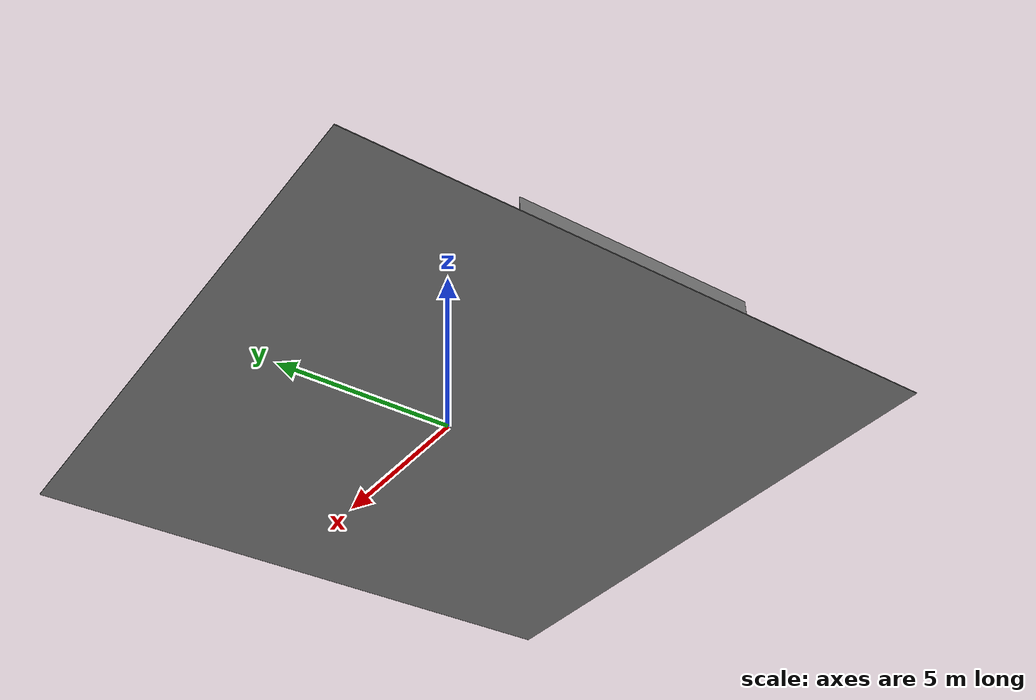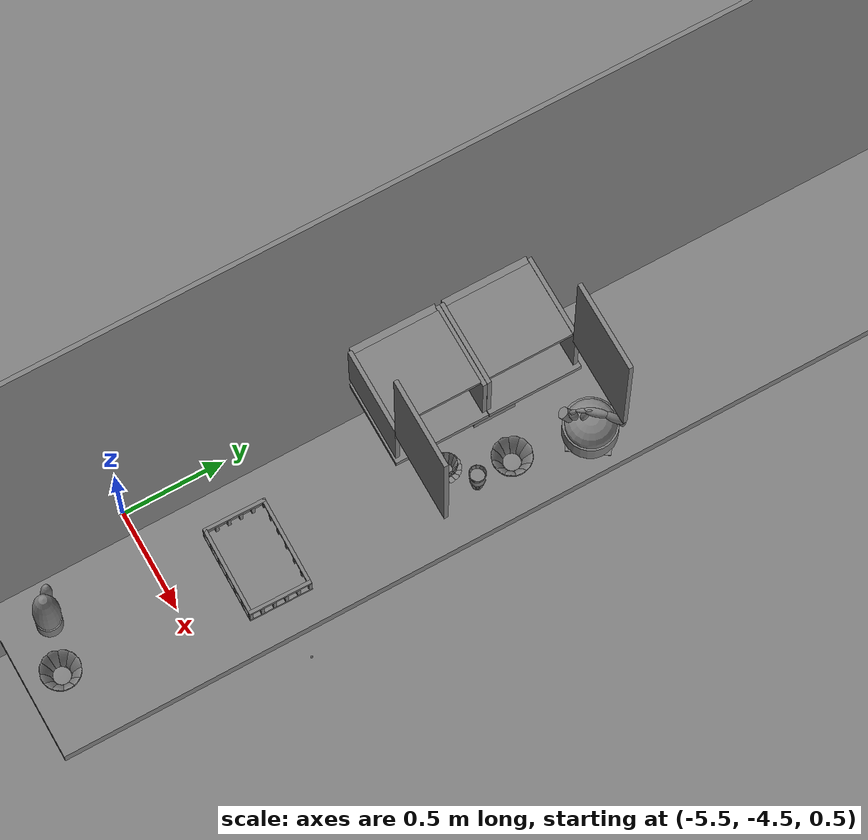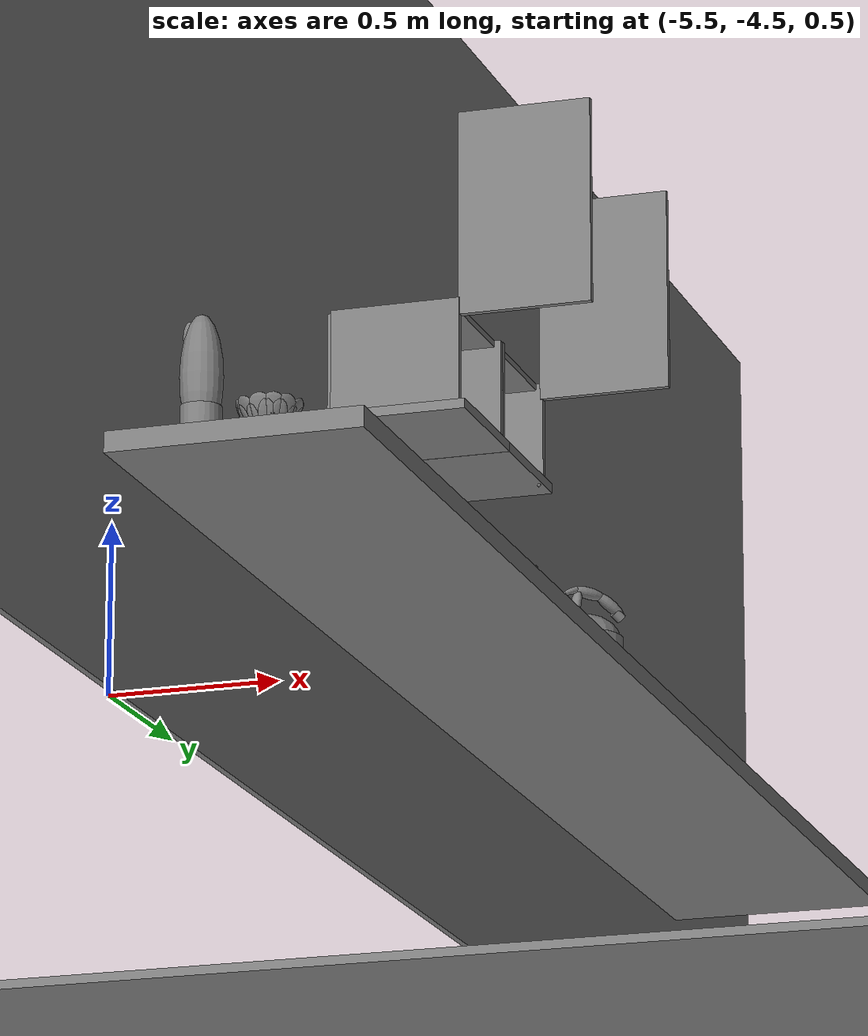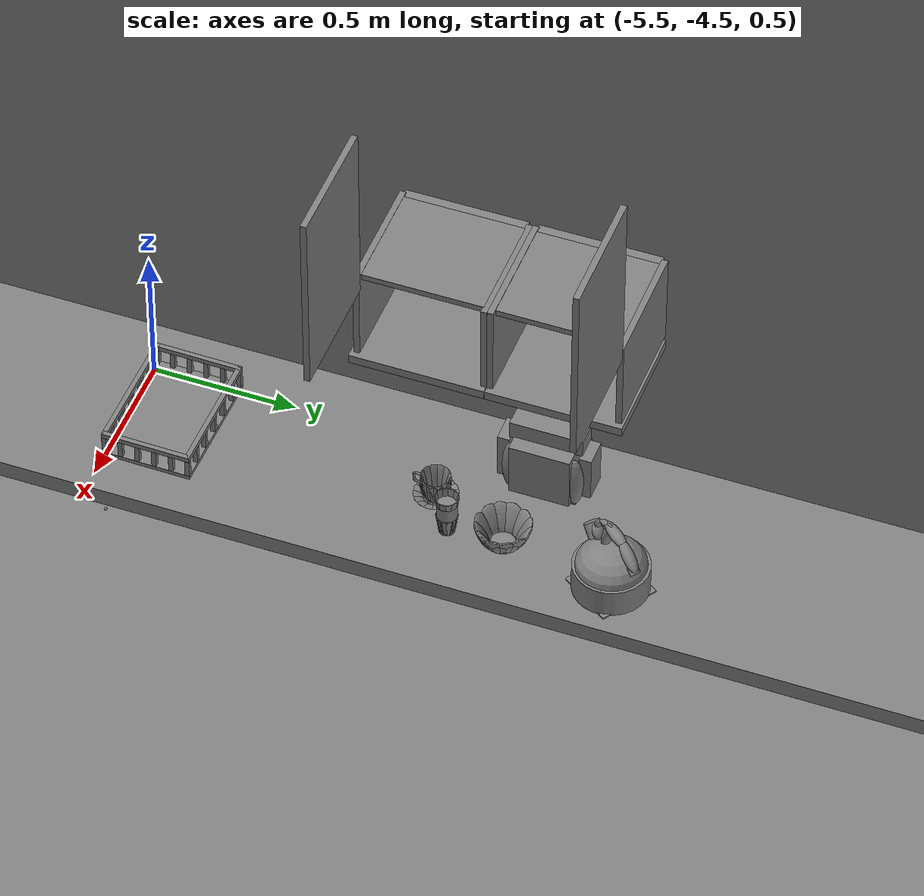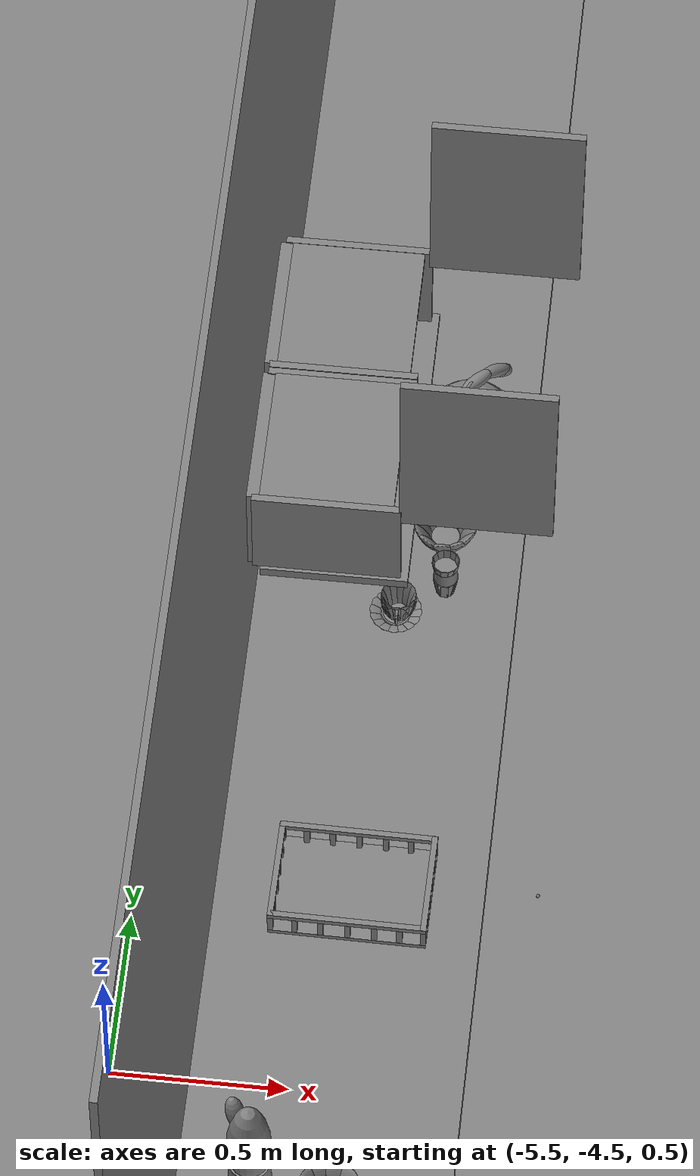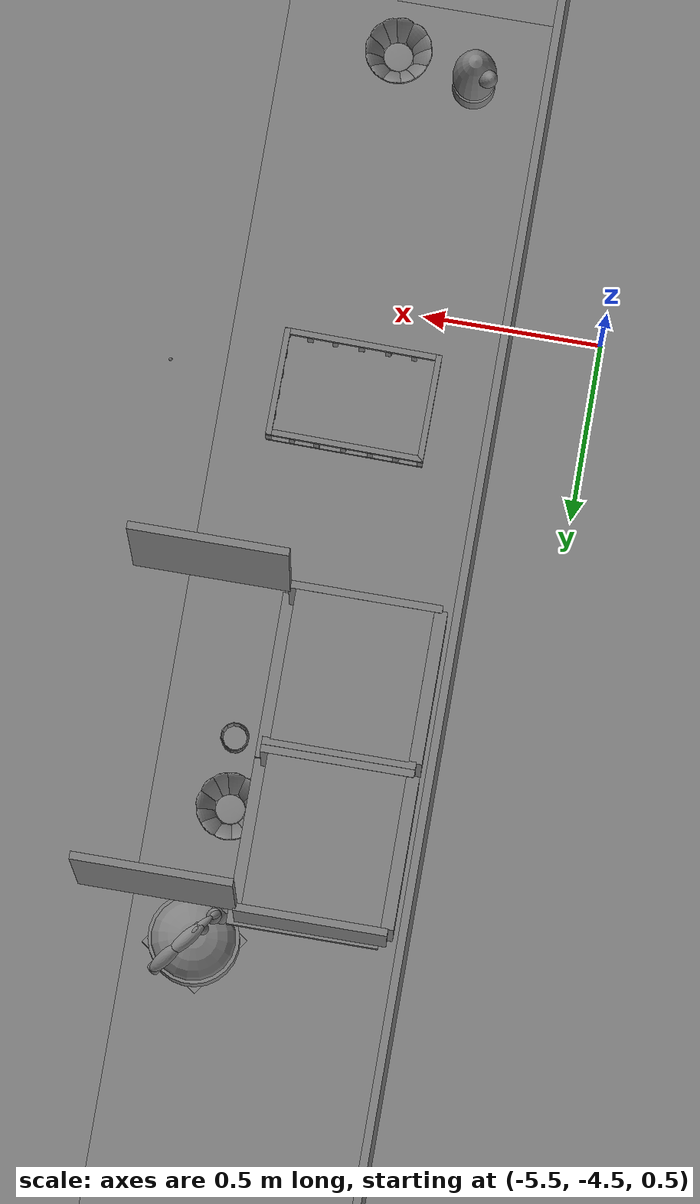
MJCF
<mujoco>
    <option gravity="0.000000000 0.000000000 -9.810000420" timestep="0.0049999999" integrator="implicitfast" density="9.8000002" viscosity="1.8000001e-05" noslip_iterations="10" iterations="100" sdf_iterations="50">
        <flag multiccd="disable"/>
    </option>
    <size memory="1000M"/>
    <compiler coordinate="local"/>
    <worldbody>
        <light cutoff="30" pos="0 1 1" dir="0 -1 -2"/>
        <light cutoff="30" pos="0 -1 1" dir="0 1 -2"/>
        <body pos="-4.860558510 -4.149443150 1.004824519" euler="0.000000000 0.000000000 -90.691093445" name="openloong_gripper_2f85_fix_base_usda_Basket_Kitchen_01">
            <geom contype="1" conaffinity="1" density="1000" type="box" material="" rgba="0.500000000 0.500000000 0.500000000 1.000000000" solimp="0.899999976 0.949999988 0.001000000" friction="1.000000000 0.005000000 0.000100000" solref="0.020000000 1.000000000" margin="0" condim="3" group="0" pos="0.086542509 0.207580954 0.047887992" quat="0.707107008 0.000000000 0.000000000 0.707106411" size="0.007600000 0.007600000 0.032000002" name="openloong_gripper_2f85_fix_base_usda_geom_2374D202_8C9F_4DAB_9841_ECA70D94A147"/>
            <geom contype="1" conaffinity="1" density="1000" type="box" material="" rgba="0.500000000 0.500000000 0.500000000 1.000000000" solimp="0.899999976 0.949999988 0.001000000" friction="1.000000000 0.005000000 0.000100000" solref="0.020000000 1.000000000" margin="0" condim="3" group="0" pos="-0.140816495 0.143605426 0.047889423" quat="0.707107008 0.000000000 0.000000000 0.707106411" size="0.007600000 0.007600000 0.032000002" name="openloong_gripper_2f85_fix_base_usda_geom_4839AE72_45D2_4C4D_B279_F9EA4C7FADA6"/>
            <geom contype="1" conaffinity="1" density="1000" type="box" material="" rgba="0.500000000 0.500000000 0.500000000 1.000000000" solimp="0.899999976 0.949999988 0.001000000" friction="1.000000000 0.005000000 0.000100000" solref="0.020000000 1.000000000" margin="0" condim="3" group="0" pos="-0.140816212 -0.070956804 0.047888946" quat="0.707107008 0.000000000 0.000000000 0.707106411" size="0.007600000 0.007600000 0.032000002" name="openloong_gripper_2f85_fix_base_usda_geom_A093F3E7_868A_4271_A1D1_CAAD8E816984"/>
            <geom contype="1" conaffinity="1" density="1000" type="box" material="" rgba="0.500000000 0.500000000 0.500000000 1.000000000" solimp="0.899999976 0.949999988 0.001000000" friction="1.000000000 0.005000000 0.000100000" solref="0.020000000 1.000000000" margin="0" condim="3" group="0" pos="0.140802577 0.207580566 0.047887899" quat="0.707107008 0.000000000 0.000000000 0.707106411" size="0.007600000 0.007600000 0.032000002" name="openloong_gripper_2f85_fix_base_usda_geom_73966173_4605_4739_9637_F474D326F91F"/>
            <geom contype="1" conaffinity="1" density="1000" type="box" material="" rgba="0.500000000 0.500000000 0.500000000 1.000000000" solimp="0.899999976 0.949999988 0.001000000" friction="1.000000000 0.005000000 0.000100000" solref="0.020000000 1.000000000" margin="0" condim="3" group="0" pos="0.086541750 -0.207636267 0.047888279" quat="0.707107008 0.000000000 0.000000000 0.707106411" size="0.007600000 0.007600000 0.032000002" name="openloong_gripper_2f85_fix_base_usda_geom_0E08CC20_3208_43AD_9F54_9872D5D4F476"/>
            <geom contype="1" conaffinity="1" density="1000" type="box" material="" rgba="0.500000000 0.500000000 0.500000000 1.000000000" solimp="0.899999976 0.949999988 0.001000000" friction="1.000000000 0.005000000 0.000100000" solref="0.020000000 1.000000000" margin="0" condim="3" group="0" pos="0.140633777 -0.000001907 0.087263681" quat="0.707107008 0.000000000 0.000000000 0.707106411" size="0.215199992 0.008000000 0.008400000" name="openloong_gripper_2f85_fix_base_usda_geom_B2212AC4_4504_4B7D_9D64_0221E3F4F6DF"/>
            <geom contype="1" conaffinity="1" density="1000" type="box" material="" rgba="0.500000000 0.500000000 0.500000000 1.000000000" solimp="0.899999976 0.949999988 0.001000000" friction="1.000000000 0.005000000 0.000100000" solref="0.020000000 1.000000000" margin="0" condim="3" group="0" pos="-0.027960587 -0.207636639 0.047888566" quat="0.707107008 0.000000000 0.000000000 0.707106411" size="0.007600000 0.007600000 0.032000002" name="openloong_gripper_2f85_fix_base_usda_geom_39D1E3B8_D18F_4C77_8706_9F69126B0E4C"/>
            <geom contype="1" conaffinity="1" density="1000" type="box" material="" rgba="0.500000000 0.500000000 0.500000000 1.000000000" solimp="0.899999976 0.949999988 0.001000000" friction="1.000000000 0.005000000 0.000100000" solref="0.020000000 1.000000000" margin="0" condim="3" group="0" pos="-0.140816122 -0.141625211 0.047888853" quat="0.707107008 0.000000000 0.000000000 0.707106411" size="0.007600000 0.007600000 0.032000002" name="openloong_gripper_2f85_fix_base_usda_geom_366E8785_E6B8_4A05_8347_EAF92C153A78"/>
            <geom contype="1" conaffinity="1" density="1000" type="box" material="" rgba="0.500000000 0.500000000 0.500000000 1.000000000" solimp="0.899999976 0.949999988 0.001000000" friction="1.000000000 0.005000000 0.000100000" solref="0.020000000 1.000000000" margin="0" condim="3" group="0" pos="-0.140816122 0.207580194 0.047888756" quat="0.707107008 0.000000000 0.000000000 0.707106411" size="0.007600000 0.007600000 0.032000002" name="openloong_gripper_2f85_fix_base_usda_geom_AC37FFED_6C2B_4A25_B44C_6716642A884F"/>
            <geom contype="1" conaffinity="1" density="1000" type="box" material="" rgba="0.500000000 0.500000000 0.500000000 1.000000000" solimp="0.899999976 0.949999988 0.001000000" friction="1.000000000 0.005000000 0.000100000" solref="0.020000000 1.000000000" margin="0" condim="3" group="0" pos="0.140800864 -0.070956804 0.047888376" quat="0.707107008 0.000000000 0.000000000 0.707106411" size="0.007600000 0.007600000 0.032000002" name="openloong_gripper_2f85_fix_base_usda_geom_4039E5A7_0D12_4FFF_B82C_3A5A295D57D0"/>
            <geom contype="1" conaffinity="1" density="1000" type="box" material="" rgba="0.500000000 0.500000000 0.500000000 1.000000000" solimp="0.899999976 0.949999988 0.001000000" friction="1.000000000 0.005000000 0.000100000" solref="0.020000000 1.000000000" margin="0" condim="3" group="0" pos="0.140800476 0.002393341 0.047888376" quat="0.707107008 0.000000000 0.000000000 0.707106411" size="0.007600000 0.007600000 0.032000002" name="openloong_gripper_2f85_fix_base_usda_geom_FE218A5F_8F81_4501_B07B_320752EE172C"/>
            <geom contype="1" conaffinity="1" density="1000" type="box" material="" rgba="0.500000000 0.500000000 0.500000000 1.000000000" solimp="0.899999976 0.949999988 0.001000000" friction="1.000000000 0.005000000 0.000100000" solref="0.020000000 1.000000000" margin="0" condim="3" group="0" pos="-0.140543848 -0.000001526 0.087263964" quat="0.707107008 0.000000000 0.000000000 0.707106411" size="0.215199992 0.008000000 0.008400000" name="openloong_gripper_2f85_fix_base_usda_geom_293576C2_1CA7_4EF4_8B15_F94627AEED05"/>
            <geom contype="1" conaffinity="1" density="1000" type="box" material="" rgba="0.500000000 0.500000000 0.500000000 1.000000000" solimp="0.899999976 0.949999988 0.001000000" friction="1.000000000 0.005000000 0.000100000" solref="0.020000000 1.000000000" margin="0" condim="3" group="0" pos="-0.140816018 0.075380705 0.047889233" quat="0.707107008 0.000000000 0.000000000 0.707106411" size="0.007600000 0.007600000 0.032000002" name="openloong_gripper_2f85_fix_base_usda_geom_34A76524_A8A8_4384_8043_FD54EF7762C4"/>
            <geom contype="1" conaffinity="1" density="1000" type="box" material="" rgba="0.500000000 0.500000000 0.500000000 1.000000000" solimp="0.899999976 0.949999988 0.001000000" friction="1.000000000 0.005000000 0.000100000" solref="0.020000000 1.000000000" margin="0" condim="3" group="0" pos="0.140801147 -0.141625211 0.047888279" quat="0.707107008 0.000000000 0.000000000 0.707106411" size="0.007600000 0.007600000 0.032000002" name="openloong_gripper_2f85_fix_base_usda_geom_9CB020DA_D5DE_412E_8ADD_03FF2F313020"/>
            <geom contype="1" conaffinity="1" density="1000" type="box" material="" rgba="0.500000000 0.500000000 0.500000000 1.000000000" solimp="0.899999976 0.949999988 0.001000000" friction="1.000000000 0.005000000 0.000100000" solref="0.020000000 1.000000000" margin="0" condim="3" group="0" pos="0.000000000 -0.207717523 0.087263964" quat="0.707107008 0.000000000 0.000000000 0.707106411" size="0.008000000 0.148000002 0.008400000" name="openloong_gripper_2f85_fix_base_usda_geom_F7E81050_6E1D_4602_B931_5920E3B051A8"/>
            <geom contype="1" conaffinity="1" density="1000" type="box" material="" rgba="0.500000000 0.500000000 0.500000000 1.000000000" solimp="0.899999976 0.949999988 0.001000000" friction="1.000000000 0.005000000 0.000100000" solref="0.020000000 1.000000000" margin="0" condim="3" group="0" pos="0.029044246 -0.207635880 0.047888376" quat="0.707107008 0.000000000 0.000000000 0.707106411" size="0.007600000 0.007600000 0.032000002" name="openloong_gripper_2f85_fix_base_usda_geom_F6173DAA_0813_479B_8F3F_AAB6FF31AFB9"/>
            <geom contype="1" conaffinity="1" density="1000" type="box" material="" rgba="0.500000000 0.500000000 0.500000000 1.000000000" solimp="0.899999976 0.949999988 0.001000000" friction="1.000000000 0.005000000 0.000100000" solref="0.020000000 1.000000000" margin="0" condim="3" group="0" pos="0.140800476 0.075379565 0.047888566" quat="0.707107008 0.000000000 0.000000000 0.707106411" size="0.007600000 0.007600000 0.032000002" name="openloong_gripper_2f85_fix_base_usda_geom_AB5A0392_C53E_4F53_99AE_4ECF32A0E450"/>
            <geom contype="1" conaffinity="1" density="1000" type="box" material="" rgba="0.500000000 0.500000000 0.500000000 1.000000000" solimp="0.899999976 0.949999988 0.001000000" friction="1.000000000 0.005000000 0.000100000" solref="0.020000000 1.000000000" margin="0" condim="3" group="0" pos="-0.027959539 0.207580566 0.047888376" quat="0.707107008 0.000000000 0.000000000 0.707106411" size="0.007600000 0.007600000 0.032000002" name="openloong_gripper_2f85_fix_base_usda_geom_50C6898D_2B99_4AC0_BA8A_1F28B6E0BC94"/>
            <geom contype="1" conaffinity="1" density="1000" type="box" material="" rgba="0.500000000 0.500000000 0.500000000 1.000000000" solimp="0.899999976 0.949999988 0.001000000" friction="1.000000000 0.005000000 0.000100000" solref="0.020000000 1.000000000" margin="0" condim="3" group="0" pos="0.140799999 0.143604279 0.047888756" quat="0.707107008 0.000000000 0.000000000 0.707106411" size="0.007600000 0.007600000 0.032000002" name="openloong_gripper_2f85_fix_base_usda_geom_FE2A9EEB_DC2A_4627_B0E3_D900361E6DE7"/>
            <geom contype="1" conaffinity="1" density="1000" type="box" material="" rgba="0.500000000 0.500000000 0.500000000 1.000000000" solimp="0.899999976 0.949999988 0.001000000" friction="1.000000000 0.005000000 0.000100000" solref="0.020000000 1.000000000" margin="0" condim="3" group="0" pos="-0.140816122 0.002393723 0.047889233" quat="0.707107008 0.000000000 0.000000000 0.707106411" size="0.007600000 0.007600000 0.032000002" name="openloong_gripper_2f85_fix_base_usda_geom_B73AD93F_5FCD_492A_BFEB_8A76C81041D3"/>
            <geom contype="1" conaffinity="1" density="1000" type="box" material="" rgba="0.500000000 0.500000000 0.500000000 1.000000000" solimp="0.899999976 0.949999988 0.001000000" friction="1.000000000 0.005000000 0.000100000" solref="0.020000000 1.000000000" margin="0" condim="3" group="0" pos="-0.085476689 0.207580194 0.047888566" quat="0.707107008 0.000000000 0.000000000 0.707106411" size="0.007600000 0.007600000 0.032000002" name="openloong_gripper_2f85_fix_base_usda_geom_AFFE1C40_1D64_4153_960F_184D5746A745"/>
            <geom contype="1" conaffinity="1" density="1000" type="box" material="" rgba="0.500000000 0.500000000 0.500000000 1.000000000" solimp="0.899999976 0.949999988 0.001000000" friction="1.000000000 0.005000000 0.000100000" solref="0.020000000 1.000000000" margin="0" condim="3" group="0" pos="0.000000000 0.207718283 0.087263964" quat="0.707107008 0.000000000 0.000000000 0.707106411" size="0.008000000 0.148000002 0.008400000" name="openloong_gripper_2f85_fix_base_usda_geom_E23EB5E3_A7D5_46B5_B3B5_2C7A70BF0C4C"/>
            <geom contype="1" conaffinity="1" density="1000" type="box" material="" rgba="0.500000000 0.500000000 0.500000000 1.000000000" solimp="0.899999976 0.949999988 0.001000000" friction="1.000000000 0.005000000 0.000100000" solref="0.020000000 1.000000000" margin="0" condim="3" group="0" pos="0.029045582 0.207581714 0.047888279" quat="0.707107008 0.000000000 0.000000000 0.707106411" size="0.007600000 0.007600000 0.032000002" name="openloong_gripper_2f85_fix_base_usda_geom_5BB4EA3B_FFC6_4D63_A272_9331EE054466"/>
            <geom contype="1" conaffinity="1" density="1000" type="box" material="" rgba="0.500000000 0.500000000 0.500000000 1.000000000" solimp="0.899999976 0.949999988 0.001000000" friction="1.000000000 0.005000000 0.000100000" solref="0.020000000 1.000000000" margin="0" condim="3" group="0" pos="-0.140816122 -0.207636267 0.047888853" quat="0.707107008 0.000000000 0.000000000 0.707106411" size="0.007600000 0.007600000 0.032000002" name="openloong_gripper_2f85_fix_base_usda_geom_DB44741A_EAA1_4D29_9839_2A8D42F62EF4"/>
            <geom contype="1" conaffinity="1" density="1000" type="box" material="" rgba="0.500000000 0.500000000 0.500000000 1.000000000" solimp="0.899999976 0.949999988 0.001000000" friction="1.000000000 0.005000000 0.000100000" solref="0.020000000 1.000000000" margin="0" condim="3" group="0" pos="-0.085477069 -0.207636639 0.047888756" quat="0.707107008 0.000000000 0.000000000 0.707106411" size="0.007600000 0.007600000 0.032000002" name="openloong_gripper_2f85_fix_base_usda_geom_05360F34_C19D_4635_BFB3_115CAE510315"/>
            <geom contype="1" conaffinity="1" density="1000" type="box" material="" rgba="0.500000000 0.500000000 0.500000000 1.000000000" solimp="0.899999976 0.949999988 0.001000000" friction="1.000000000 0.005000000 0.000100000" solref="0.020000000 1.000000000" margin="0" condim="3" group="0" pos="-0.000012112 0.000000381 0.008534336" quat="0.707107008 0.000000000 0.000000000 0.707106411" size="0.215199992 0.148800001 0.008400000" name="openloong_gripper_2f85_fix_base_usda_geom_0B489D34_9167_4E70_A5C0_9AF564DDA037"/>
            <geom contype="1" conaffinity="1" density="1000" type="box" material="" rgba="0.500000000 0.500000000 0.500000000 1.000000000" solimp="0.899999976 0.949999988 0.001000000" friction="1.000000000 0.005000000 0.000100000" solref="0.020000000 1.000000000" margin="0" condim="3" group="0" pos="0.140801623 -0.207636267 0.047888186" quat="0.707107008 0.000000000 0.000000000 0.707106411" size="0.007600000 0.007600000 0.032000002" name="openloong_gripper_2f85_fix_base_usda_geom_01D54A6B_2D3A_4697_A331_A34FD10E4052"/>
            <freejoint name="openloong_gripper_2f85_fix_base_usda_Basket_Kitchen_01_joint"/>
            <site size="0.005000000 0.005000000 0.005000000" rgba="0.500000000 0.500000000 0.500000000 1.000000000" pos="0.000000000 0.000000000 0.000000000" quat="1.000000000 0.000000000 0.000000000 0.000000000" group="0" type="sphere" name="openloong_gripper_2f85_fix_base_usda_Basket_Kitchen_01site"/>
        </body>
        <body pos="-4.721817970 -2.990536690 1.027358174" euler="0.000000000 0.000000000 89.999946594" name="Interactive Objcets_bow_02">
            <geom contype="1" conaffinity="1" density="1000" type="ellipsoid" material="" rgba="0.500000000 0.500000000 0.500000000 1.000000000" solimp="0.899999976 0.949999988 0.001000000" friction="1.000000000 0.005000000 0.000100000" solref="0.020000000 1.000000000" margin="0" condim="3" group="0" pos="-0.058925860 -0.029528141 0.044118762" quat="0.223252773 0.231952101 0.054787740 -0.945174515" size="0.010000000 0.039999999 0.052000001" name="Interactive Objcets_geom_1F925AD2_FC6D_410B_AC29_E1BCDCEF0DAB"/>
            <geom contype="1" conaffinity="1" density="1000" type="ellipsoid" material="" rgba="0.500000000 0.500000000 0.500000000 1.000000000" solimp="0.899999976 0.949999988 0.001000000" friction="1.000000000 0.005000000 0.000100000" solref="0.020000000 1.000000000" margin="0" condim="3" group="0" pos="0.000082973 0.000000000 0.000446677" quat="1.000000000 0.000000000 0.000000000 0.000000000" size="0.039999999 0.039999999 0.002000000" name="Interactive Objcets_geom_235E29F8_C6E8_4EDF_AD76_66CBABF2C937"/>
            <geom contype="1" conaffinity="1" density="1000" type="ellipsoid" material="" rgba="0.500000000 0.500000000 0.500000000 1.000000000" solimp="0.899999976 0.949999988 0.001000000" friction="1.000000000 0.005000000 0.000100000" solref="0.020000000 1.000000000" margin="0" condim="3" group="0" pos="0.029448029 -0.059084892 0.044118762" quat="0.825555801 0.125530601 0.202597082 -0.511521280" size="0.010000000 0.039999999 0.052000001" name="Interactive Objcets_geom_C64FAE55_8FD9_4C48_951A_1C98F3E5A53F"/>
            <geom contype="1" conaffinity="1" density="1000" type="ellipsoid" material="" rgba="0.500000000 0.500000000 0.500000000 1.000000000" solimp="0.899999976 0.949999988 0.001000000" friction="1.000000000 0.005000000 0.000100000" solref="0.020000000 1.000000000" margin="0" condim="3" group="0" pos="0.000082973 0.000000000 0.005656481" quat="1.000000000 0.000000000 0.000000000 0.000000000" size="0.039999999 0.039999999 0.002000000" name="Interactive Objcets_geom_6CB0AC34_54AC_49C7_8967_8E7051C8124C"/>
            <geom contype="1" conaffinity="1" density="1000" type="ellipsoid" material="" rgba="0.500000000 0.500000000 0.500000000 1.000000000" solimp="0.899999976 0.949999988 0.001000000" friction="1.000000000 0.005000000 0.000100000" solref="0.020000000 1.000000000" margin="0" condim="3" group="0" pos="-0.040080305 -0.052354336 0.044118762" quat="0.429593205 0.213749886 0.105425082 -0.871003032" size="0.010000000 0.039999999 0.052000001" name="Interactive Objcets_geom_91B32DDD_3F22_48AD_98F3_5E40306D4247"/>
            <geom contype="1" conaffinity="1" density="1000" type="ellipsoid" material="" rgba="0.500000000 0.500000000 0.500000000 1.000000000" solimp="0.899999976 0.949999988 0.001000000" friction="1.000000000 0.005000000 0.000100000" solref="0.020000000 1.000000000" margin="0" condim="3" group="0" pos="-0.065898418 -0.000007629 0.044118762" quat="0.971183062 -0.000000142 -0.238334835 0.000000030" size="0.010000000 0.039999999 0.052000001" name="Interactive Objcets_geom_06EFCFC0_180D_45B3_976A_5B9BB9081842"/>
            <geom contype="1" conaffinity="1" density="1000" type="ellipsoid" material="" rgba="0.500000000 0.500000000 0.500000000 1.000000000" solimp="0.899999976 0.949999988 0.001000000" friction="1.000000000 0.005000000 0.000100000" solref="0.020000000 1.000000000" margin="0" condim="3" group="0" pos="0.059080135 0.029512405 0.044118762" quat="0.223252743 -0.231952220 -0.054787420 -0.945174456" size="0.010000000 0.039999999 0.052000001" name="Interactive Objcets_geom_51812B21_1945_4FB2_AAF5_FFB4725E1F26"/>
            <geom contype="1" conaffinity="1" density="1000" type="ellipsoid" material="" rgba="0.500000000 0.500000000 0.500000000 1.000000000" solimp="0.899999976 0.949999988 0.001000000" friction="1.000000000 0.005000000 0.000100000" solref="0.020000000 1.000000000" margin="0" condim="3" group="0" pos="0.066052437 -0.000007629 0.044118762" quat="0.971183062 -0.000000156 0.238334835 0.000000030" size="0.010000000 0.039999999 0.052000001" name="Interactive Objcets_geom_C71F8DCE_AB9F_4364_81A5_DA750F16DBB0"/>
            <geom contype="1" conaffinity="1" density="1000" type="ellipsoid" material="" rgba="0.500000000 0.500000000 0.500000000 1.000000000" solimp="0.899999976 0.949999988 0.001000000" friction="1.000000000 0.005000000 0.000100000" solref="0.020000000 1.000000000" margin="0" condim="3" group="0" pos="0.000243668 -0.065982819 0.044118762" quat="0.687598705 0.168314636 0.168741375 -0.685860336" size="0.010000000 0.039999999 0.052000001" name="Interactive Objcets_geom_879DA8F2_D3D2_4332_BB04_D12A4DCDDDFE"/>
            <geom contype="1" conaffinity="1" density="1000" type="ellipsoid" material="" rgba="0.500000000 0.500000000 0.500000000 1.000000000" solimp="0.899999976 0.949999988 0.001000000" friction="1.000000000 0.005000000 0.000100000" solref="0.020000000 1.000000000" margin="0" condim="3" group="0" pos="-0.000090118 0.065967560 0.044118762" quat="0.687598705 -0.168314859 -0.168741152 -0.685860336" size="0.010000000 0.039999999 0.052000001" name="Interactive Objcets_geom_0BC1B6C7_24E5_4606_A343_EE2082ED26E2"/>
            <geom contype="1" conaffinity="1" density="1000" type="ellipsoid" material="" rgba="0.500000000 0.500000000 0.500000000 1.000000000" solimp="0.899999976 0.949999988 0.001000000" friction="1.000000000 0.005000000 0.000100000" solref="0.020000000 1.000000000" margin="0" condim="3" group="0" pos="0.052321676 -0.040297508 0.044118762" quat="0.919264674 0.076882742 0.225593731 -0.313287675" size="0.010000000 0.039999999 0.052000001" name="Interactive Objcets_geom_E0D94D25_AB06_442A_A5A6_E7471B1F754D"/>
            <geom contype="1" conaffinity="1" density="1000" type="ellipsoid" material="" rgba="0.500000000 0.500000000 0.500000000 1.000000000" solimp="0.899999976 0.949999988 0.001000000" friction="1.000000000 0.005000000 0.000100000" solref="0.020000000 1.000000000" margin="0" condim="3" group="0" pos="0.040234569 0.052338600 0.044118762" quat="0.429593176 -0.213750035 -0.105424814 -0.871002913" size="0.010000000 0.039999999 0.052000001" name="Interactive Objcets_geom_999607A3_6ED7_4445_9CF9_1078AE80BD97"/>
            <geom contype="1" conaffinity="1" density="1000" type="ellipsoid" material="" rgba="0.500000000 0.500000000 0.500000000 1.000000000" solimp="0.899999976 0.949999988 0.001000000" friction="1.000000000 0.005000000 0.000100000" solref="0.020000000 1.000000000" margin="0" condim="3" group="0" pos="-0.052167647 0.040282249 0.044118762" quat="0.919264615 -0.076883025 -0.225593641 -0.313287735" size="0.010000000 0.039999999 0.052000001" name="Interactive Objcets_geom_43D18CD1_8BE1_45B7_A3F1_CA2FE9F76DE6"/>
            <geom contype="1" conaffinity="1" density="1000" type="ellipsoid" material="" rgba="0.500000000 0.500000000 0.500000000 1.000000000" solimp="0.899999976 0.949999988 0.001000000" friction="1.000000000 0.005000000 0.000100000" solref="0.020000000 1.000000000" margin="0" condim="3" group="0" pos="-0.029293532 0.059069633 0.044118762" quat="0.825555801 -0.125530809 -0.202596903 -0.511521280" size="0.010000000 0.039999999 0.052000001" name="Interactive Objcets_geom_34B44CF5_204B_47D9_B8DC_F04EA7E15267"/>
            <freejoint name="Interactive Objcets_bow_02"/>
        </body>
        <body pos="-4.802892208 -3.488179445 1.876015186" euler="89.999992371 -89.999946594 0.000000000" name="Interactive Objcets_guimen_01">
            <geom contype="1" conaffinity="1" density="1000" type="box" material="" rgba="0.500000000 0.500000000 0.500000000 1.000000000" solimp="0.899999976 0.949999988 0.001000000" friction="1.000000000 0.005000000 0.000100000" solref="0.020000000 1.000000000" margin="0" condim="3" group="0" pos="0.006727934 0.314709902 -0.203009605" quat="1.000000000 0.000000119 -0.000000119 0.000000000" size="0.010000000 0.317999989 0.204999998" name="Interactive Objcets_geom_712CE369_7B33_46ED_8414_54113B1E16AD"/>
            <joint armature="0" stiffness="0" damping="1" axis="0.000000 1.000000 0.000000" type="hinge" name="Interactive Objcets_guimen_01"/>
        </body>
        <body pos="-4.827295780 -3.287638187 1.074643731" euler="0.000000000 0.000000000 89.999992371" name="Interactive Objcets_coffeecup_01">
            <geom contype="1" conaffinity="1" density="1000" type="ellipsoid" material="" rgba="0.500000000 0.500000000 0.500000000 1.000000000" solimp="0.899999976 0.949999988 0.001000000" friction="1.000000000 0.005000000 0.000100000" solref="0.020000000 1.000000000" margin="0" condim="3" group="0" pos="0.053700209 0.033117294 0.002976775" quat="0.496025741 -0.082236379 -0.047260769 -0.863111615" size="0.005000000 0.029999999 0.048999999" name="Interactive Objcets_geom_FE7D4711_F319_40D3_AF37_11AE5D36DD3A"/>
            <geom contype="1" conaffinity="1" density="1000" type="ellipsoid" material="" rgba="0.500000000 0.500000000 0.500000000 1.000000000" solimp="0.899999976 0.949999988 0.001000000" friction="1.000000000 0.005000000 0.000100000" solref="0.020000000 1.000000000" margin="0" condim="3" group="0" pos="0.068445444 0.017385960 0.002976775" quat="0.228377223 -0.092319682 -0.021759447 -0.968941331" size="0.005000000 0.029999999 0.048999999" name="Interactive Objcets_geom_C400140A_19F3_4737_A91F_0642E0F34DD2"/>
            <geom contype="1" conaffinity="1" density="1000" type="capsule" material="" rgba="0.500000000 0.500000000 0.500000000 1.000000000" solimp="0.899999976 0.949999988 0.001000000" friction="1.000000000 0.005000000 0.000100000" solref="0.020000000 1.000000000" margin="0" condim="3" group="0" pos="-0.030251026 0.000000000 0.004966617" quat="0.480583906 -0.000000000 0.876948774 -0.000000126" size="0.004000000 0.005000000 1.000000000" name="Interactive Objcets_geom_B91A0D01_5515_4047_AB2C_62D5606DA159"/>
            <geom contype="1" conaffinity="1" density="1000" type="ellipsoid" material="" rgba="0.500000000 0.500000000 0.500000000 1.000000000" solimp="0.899999976 0.949999988 0.001000000" friction="1.000000000 0.005000000 0.000100000" solref="0.020000000 1.000000000" margin="0" condim="3" group="0" pos="0.034471050 -0.037125111 0.002976775" quat="0.701517045 0.067293778 0.066836871 -0.706313014" size="0.005000000 0.029999999 0.048999999" name="Interactive Objcets_geom_C63360E0_6231_48F2_BDC5_1D82CDB4B48A"/>
            <geom contype="1" conaffinity="1" density="1000" type="ellipsoid" material="" rgba="0.500000000 0.500000000 0.500000000 1.000000000" solimp="0.899999976 0.949999988 0.001000000" friction="1.000000000 0.005000000 0.000100000" solref="0.020000000 1.000000000" margin="0" condim="3" group="0" pos="0.035336256 0.000558376 -0.045152068" quat="0.999999881 0.000000000 0.000000000 0.000000000" size="0.029999999 0.029999999 0.001000000" name="Interactive Objcets_geom_831595B6_FE06_4F13_9189_CB547B3D604E"/>
            <geom contype="1" conaffinity="1" density="1000" type="capsule" material="" rgba="0.500000000 0.500000000 0.500000000 1.000000000" solimp="0.899999976 0.949999988 0.001000000" friction="1.000000000 0.005000000 0.000100000" solref="0.020000000 1.000000000" margin="0" condim="3" group="0" pos="-0.021276474 0.000000000 0.038509369" quat="0.633189917 0.000000000 0.773996413 0.000000000" size="0.004000000 0.009000000 1.000000000" name="Interactive Objcets_geom_68B7306E_06DA_423A_B2D3_B02C1BBD6766"/>
            <geom contype="1" conaffinity="1" density="1000" type="capsule" material="" rgba="0.500000000 0.500000000 0.500000000 1.000000000" solimp="0.899999976 0.949999988 0.001000000" friction="1.000000000 0.005000000 0.000100000" solref="0.020000000 1.000000000" margin="0" condim="3" group="0" pos="-0.018014431 0.000000000 0.001762271" quat="0.707106769 -0.000000004 0.707106709 -0.000000088" size="0.004000000 0.005000000 1.000000000" name="Interactive Objcets_geom_9C7D14D8_5C67_44C3_B1F4_AB636551349B"/>
            <geom contype="1" conaffinity="1" density="1000" type="ellipsoid" material="" rgba="0.500000000 0.500000000 0.500000000 1.000000000" solimp="0.899999976 0.949999988 0.001000000" friction="1.000000000 0.005000000 0.000100000" solref="0.020000000 1.000000000" margin="0" condim="3" group="0" pos="0.001010895 -0.016271591 0.002976775" quat="0.228377163 0.092315644 0.021758538 -0.968941689" size="0.005000000 0.029999999 0.048999999" name="Interactive Objcets_geom_14254D9B_0ABC_48A6_AF51_1FF111FCFB36"/>
            <geom contype="1" conaffinity="1" density="1000" type="capsule" material="" rgba="0.500000000 0.500000000 0.500000000 1.000000000" solimp="0.899999976 0.949999988 0.001000000" friction="1.000000000 0.005000000 0.000100000" solref="0.020000000 1.000000000" margin="0" condim="3" group="0" pos="-0.008219719 0.000000000 -0.000944734" quat="0.364379913 0.000000063 0.931250274 -0.000000063" size="0.004000000 0.003000000 1.000000000" name="Interactive Objcets_geom_2EC6E04E_6E26_4A5E_B973_1AECCAB7A003"/>
            <geom contype="1" conaffinity="1" density="1000" type="ellipsoid" material="" rgba="0.500000000 0.500000000 0.500000000 1.000000000" solimp="0.899999976 0.949999988 0.001000000" friction="1.000000000 0.005000000 0.000100000" solref="0.020000000 1.000000000" margin="0" condim="3" group="0" pos="0.002039194 0.019308567 0.002976775" quat="0.961933970 -0.024419386 -0.091652036 -0.256293654" size="0.005000000 0.029999999 0.048999999" name="Interactive Objcets_geom_C4B988FF_8368_4A3B_838F_5E8DDFF7969E"/>
            <geom contype="1" conaffinity="1" density="1000" type="capsule" material="" rgba="0.500000000 0.500000000 0.500000000 1.000000000" solimp="0.899999976 0.949999988 0.001000000" friction="1.000000000 0.005000000 0.000100000" solref="0.020000000 1.000000000" margin="0" condim="3" group="0" pos="-0.033022881 0.000000000 0.037873149" quat="0.874267220 0.000000042 0.485444903 -0.000000084" size="0.004000000 0.004000000 1.000000000" name="Interactive Objcets_geom_B918A7BB_09DD_4BE9_AFE5_78AA73278F11"/>
            <geom contype="1" conaffinity="1" density="1000" type="ellipsoid" material="" rgba="0.500000000 0.500000000 0.500000000 1.000000000" solimp="0.899999976 0.949999988 0.001000000" friction="1.000000000 0.005000000 0.000100000" solref="0.020000000 1.000000000" margin="0" condim="3" group="0" pos="0.034984604 0.038240910 0.002976775" quat="0.701516926 -0.067296736 -0.066839755 -0.706312656" size="0.005000000 0.029999999 0.048999999" name="Interactive Objcets_geom_C072B9D6_FD7F_4874_8C6B_37BC17EFC8B1"/>
            <geom contype="1" conaffinity="1" density="1000" type="ellipsoid" material="" rgba="0.500000000 0.500000000 0.500000000 1.000000000" solimp="0.899999976 0.949999988 0.001000000" friction="1.000000000 0.005000000 0.000100000" solref="0.020000000 1.000000000" margin="0" condim="3" group="0" pos="-0.002956629 0.000558376 0.002976775" quat="0.995491505 0.000000004 -0.094849378 -0.000000089" size="0.005000000 0.029999999 0.048999999" name="Interactive Objcets_geom_3E08CA87_0BDF_4175_885C_DBEE17246806"/>
            <geom contype="1" conaffinity="1" density="1000" type="ellipsoid" material="" rgba="0.500000000 0.500000000 0.500000000 1.000000000" solimp="0.899999976 0.949999988 0.001000000" friction="1.000000000 0.005000000 0.000100000" solref="0.020000000 1.000000000" margin="0" condim="3" group="0" pos="0.017669693 0.034160614 0.002976775" quat="0.848410904 -0.049618516 -0.080835648 -0.520770907" size="0.005000000 0.029999999 0.048999999" name="Interactive Objcets_geom_4EEC85A2_2DB4_418A_AE3C_DD8B8BCB810A"/>
            <geom contype="1" conaffinity="1" density="1000" type="ellipsoid" material="" rgba="0.500000000 0.500000000 0.500000000 1.000000000" solimp="0.899999976 0.949999988 0.001000000" friction="1.000000000 0.005000000 0.000100000" solref="0.020000000 1.000000000" margin="0" condim="3" group="0" pos="0.051787138 -0.033043861 0.002976775" quat="0.848411202 0.049616337 0.080832161 -0.520771146" size="0.005000000 0.029999999 0.048999999" name="Interactive Objcets_geom_F9D771EF_F2B9_432C_9B0B_62C4F3E08BB2"/>
            <geom contype="1" conaffinity="1" density="1000" type="ellipsoid" material="" rgba="0.500000000 0.500000000 0.500000000 1.000000000" solimp="0.899999976 0.949999988 0.001000000" friction="1.000000000 0.005000000 0.000100000" solref="0.020000000 1.000000000" margin="0" condim="3" group="0" pos="0.035336256 0.000558376 -0.043215394" quat="0.999999881 0.000000000 0.000000000 0.000000000" size="0.029999999 0.029999999 0.001000000" name="Interactive Objcets_geom_ECAA4E42_8E10_4B13_9F69_55E781935D2D"/>
            <geom contype="1" conaffinity="1" density="1000" type="capsule" material="" rgba="0.500000000 0.500000000 0.500000000 1.000000000" solimp="0.899999976 0.949999988 0.001000000" friction="1.000000000 0.005000000 0.000100000" solref="0.020000000 1.000000000" margin="0" condim="3" group="0" pos="-0.036300898 0.000000000 0.021037936" quat="0.044551343 -0.000000000 0.999007046 -0.000000126" size="0.004000000 0.012000000 1.000000000" name="Interactive Objcets_geom_A52060D7_23CB_42B5_BEA0_B40761AA227D"/>
            <geom contype="1" conaffinity="1" density="1000" type="ellipsoid" material="" rgba="0.500000000 0.500000000 0.500000000 1.000000000" solimp="0.899999976 0.949999988 0.001000000" friction="1.000000000 0.005000000 0.000100000" solref="0.020000000 1.000000000" margin="0" condim="3" group="0" pos="0.067416430 -0.018191338 0.002976775" quat="0.961934388 0.024418317 0.091648072 -0.256293803" size="0.005000000 0.029999999 0.048999999" name="Interactive Objcets_geom_A548C6FB_50DE_4CB4_8995_6498584B7AB2"/>
            <geom contype="1" conaffinity="1" density="1000" type="ellipsoid" material="" rgba="0.500000000 0.500000000 0.500000000 1.000000000" solimp="0.899999976 0.949999988 0.001000000" friction="1.000000000 0.005000000 0.000100000" solref="0.020000000 1.000000000" margin="0" condim="3" group="0" pos="0.015755907 -0.032001972 0.002976775" quat="0.496025920 0.082232773 0.047258731 -0.863112032" size="0.005000000 0.029999999 0.048999999" name="Interactive Objcets_geom_F0E0A248_EB10_4A00_8C57_B218CB09286B"/>
            <geom contype="1" conaffinity="1" density="1000" type="ellipsoid" material="" rgba="0.500000000 0.500000000 0.500000000 1.000000000" solimp="0.899999976 0.949999988 0.001000000" friction="1.000000000 0.005000000 0.000100000" solref="0.020000000 1.000000000" margin="0" condim="3" group="0" pos="0.072411790 0.000558376 0.002976775" quat="0.995491922 -0.000000019 0.094845265 -0.000000089" size="0.005000000 0.029999999 0.048999999" name="Interactive Objcets_geom_FDA412AB_8B46_45BC_981F_96B0F6C33DA7"/>
            <freejoint name="Interactive Objcets_coffeecup_01"/>
        </body>
        <body pos="-4.805274963 -2.665403366 1.876015186" euler="89.999877930 89.999969482 0.000000000" name="Interactive Objcets_guimen_02">
            <geom contype="1" conaffinity="1" density="1000" type="box" material="" rgba="0.500000000 0.500000000 0.500000000 1.000000000" solimp="0.899999976 0.949999988 0.001000000" friction="1.000000000 0.005000000 0.000100000" solref="0.020000000 1.000000000" margin="0" condim="3" group="0" pos="0.006727815 0.314709663 0.203009367" quat="0.999999940 0.000000000 0.000000000 0.000000000" size="0.010000000 0.317999989 0.204999998" name="Interactive Objcets_geom_790D8632_3289_4012_B9F9_604D33D71D28"/>
            <joint armature="0" stiffness="0" damping="1" axis="0.000000 1.000000 0.000000" type="hinge" name="Interactive Objcets_guimen_02"/>
        </body>
        <body pos="-4.705342293 -3.169416904 1.103703976" euler="0.000000000 0.000000000 0.000000000" name="Interactive Objcets_cup_02">
            <geom contype="1" conaffinity="1" density="1000" type="box" material="" rgba="0.500000000 0.500000000 0.500000000 1.000000000" solimp="0.899999976 0.949999988 0.001000000" friction="1.000000000 0.005000000 0.000100000" solref="0.020000000 1.000000000" margin="0" condim="3" group="0" pos="-0.016875744 0.022189617 -0.037281752" quat="0.944716334 -0.074092269 -0.024973858 0.318430305" size="0.010000000 0.001000000 0.035000000" name="Interactive Objcets_geom_DB5D9ECB_FE9F_4378_9639_6120AF66A0EF"/>
            <geom contype="1" conaffinity="1" density="1000" type="box" material="" rgba="0.500000000 0.500000000 0.500000000 1.000000000" solimp="0.899999976 0.949999988 0.001000000" friction="1.000000000 0.005000000 0.000100000" solref="0.020000000 1.000000000" margin="0" condim="3" group="0" pos="0.029378891 -0.018181801 0.062637210" quat="0.870895982 0.068302706 0.038053915 0.485208035" size="0.010000000 0.001000000 0.015000000" name="Interactive Objcets_geom_D1FA67ED_11A4_4657_9F58_297EA936BAFF"/>
            <geom contype="1" conaffinity="1" density="1000" type="box" material="" rgba="0.500000000 0.500000000 0.500000000 1.000000000" solimp="0.899999976 0.949999988 0.001000000" friction="1.000000000 0.005000000 0.000100000" solref="0.020000000 1.000000000" margin="0" condim="3" group="0" pos="0.027999878 0.000000000 -0.037281752" quat="0.704941988 -0.055288255 0.055288251 -0.704942048" size="0.010000000 0.001000000 0.035000000" name="Interactive Objcets_geom_AF29844F_3D94_40AA_9C2D_DD3363BDEC95"/>
            <geom contype="1" conaffinity="1" density="1000" type="box" material="" rgba="0.500000000 0.500000000 0.500000000 1.000000000" solimp="0.899999976 0.949999988 0.001000000" friction="1.000000000 0.005000000 0.000100000" solref="0.020000000 1.000000000" margin="0" condim="3" group="0" pos="0.022285938 0.016949892 -0.037281752" quat="0.893179297 -0.070051625 0.034732576 -0.442851186" size="0.010000000 0.001000000 0.035000000" name="Interactive Objcets_geom_4E5379B9_C0FD_411B_B07D_761076043272"/>
            <geom contype="1" conaffinity="1" density="1000" type="cylinder" material="" rgba="0.500000000 0.500000000 0.500000000 1.000000000" solimp="0.899999976 0.949999988 0.001000000" friction="1.000000000 0.005000000 0.000100000" solref="0.020000000 1.000000000" margin="0" condim="3" group="0" pos="0.000000000 0.000000000 0.022491097" quat="1.000000000 0.000000030 0.000000000 0.000000000" size="0.033000000 0.025000000 1.000000000" name="Interactive Objcets_geom_D7835A71_1FE7_4131_B2BD_9596E1D86CE6"/>
            <geom contype="1" conaffinity="1" density="1000" type="box" material="" rgba="0.500000000 0.500000000 0.500000000 1.000000000" solimp="0.899999976 0.949999988 0.001000000" friction="1.000000000 0.005000000 0.000100000" solref="0.020000000 1.000000000" margin="0" condim="3" group="0" pos="0.000000000 0.034549713 0.062637210" quat="0.996938646 -0.078187965 0.000000000 0.000000000" size="0.010000000 0.001000000 0.015000000" name="Interactive Objcets_geom_52753214_C1D7_48C4_AD6E_8B0275C554D2"/>
            <geom contype="1" conaffinity="1" density="1000" type="box" material="" rgba="0.500000000 0.500000000 0.500000000 1.000000000" solimp="0.899999976 0.949999988 0.001000000" friction="1.000000000 0.005000000 0.000100000" solref="0.020000000 1.000000000" margin="0" condim="3" group="0" pos="-0.018181324 -0.029377937 0.062637210" quat="0.958910167 0.075206861 -0.021389510 -0.272722572" size="0.010000000 0.001000000 0.015000000" name="Interactive Objcets_geom_0201DD68_1E82_40E6_8044_C7036AC02BD9"/>
            <geom contype="1" conaffinity="1" density="1000" type="box" material="" rgba="0.500000000 0.500000000 0.500000000 1.000000000" solimp="0.899999976 0.949999988 0.001000000" friction="1.000000000 0.005000000 0.000100000" solref="0.020000000 1.000000000" margin="0" condim="3" group="0" pos="-0.034549713 0.000000000 0.062637210" quat="0.704941988 0.055288255 -0.055288251 -0.704942048" size="0.010000000 0.001000000 0.015000000" name="Interactive Objcets_geom_26B12A0F_08B5_4DF3_AF39_4F83AC6C9EF2"/>
            <geom contype="1" conaffinity="1" density="1000" type="box" material="" rgba="0.500000000 0.500000000 0.500000000 1.000000000" solimp="0.899999976 0.949999988 0.001000000" friction="1.000000000 0.005000000 0.000100000" solref="0.020000000 1.000000000" margin="0" condim="3" group="0" pos="0.011943817 0.025323629 -0.037281752" quat="0.972834349 -0.076298930 0.017089661 -0.217898533" size="0.010000000 0.001000000 0.035000000" name="Interactive Objcets_geom_D22B57B2_4294_45E3_A39C_DCA50E2EECB3"/>
            <geom contype="1" conaffinity="1" density="1000" type="box" material="" rgba="0.500000000 0.500000000 0.500000000 1.000000000" solimp="0.899999976 0.949999988 0.001000000" friction="1.000000000 0.005000000 0.000100000" solref="0.020000000 1.000000000" margin="0" condim="3" group="0" pos="0.017436981 -0.029826880 0.062637210" quat="0.962265730 0.075468659 0.020441191 0.260636479" size="0.010000000 0.001000000 0.015000000" name="Interactive Objcets_geom_32F1B0FE_0408_4E33_AC89_27867D545AAC"/>
            <geom contype="1" conaffinity="1" density="1000" type="box" material="" rgba="0.500000000 0.500000000 0.500000000 1.000000000" solimp="0.899999976 0.949999988 0.001000000" friction="1.000000000 0.005000000 0.000100000" solref="0.020000000 1.000000000" margin="0" condim="3" group="0" pos="0.000000000 -0.034549713 0.062637210" quat="0.996938646 0.078187965 0.000000000 0.000000000" size="0.010000000 0.001000000 0.015000000" name="Interactive Objcets_geom_69CF5CBF_0B6C_4A61_BE5F_3BAC35453351"/>
            <geom contype="1" conaffinity="1" density="1000" type="box" material="" rgba="0.500000000 0.500000000 0.500000000 1.000000000" solimp="0.899999976 0.949999988 0.001000000" friction="1.000000000 0.005000000 0.000100000" solref="0.020000000 1.000000000" margin="0" condim="3" group="0" pos="0.016875744 -0.022189379 -0.037281752" quat="0.944716334 0.074092269 0.024973858 0.318430305" size="0.010000000 0.001000000 0.035000000" name="Interactive Objcets_geom_3D18AA02_CEA5_4546_9242_D310F89F2B63"/>
            <geom contype="1" conaffinity="1" density="1000" type="box" material="" rgba="0.500000000 0.500000000 0.500000000 1.000000000" solimp="0.899999976 0.949999988 0.001000000" friction="1.000000000 0.005000000 0.000100000" solref="0.020000000 1.000000000" margin="0" condim="3" group="0" pos="-0.025214195 0.011891127 -0.037281752" quat="0.841975451 -0.066034243 -0.041866414 0.533820212" size="0.010000000 0.001000000 0.035000000" name="Interactive Objcets_geom_AEC17FF5_8D61_47DD_B81E_64FAEE0CA4C3"/>
            <geom contype="1" conaffinity="1" density="1000" type="box" material="" rgba="0.500000000 0.500000000 0.500000000 1.000000000" solimp="0.899999976 0.949999988 0.001000000" friction="1.000000000 0.005000000 0.000100000" solref="0.020000000 1.000000000" margin="0" condim="3" group="0" pos="0.000000000 0.027877331 -0.037281752" quat="0.996938646 -0.078187965 0.000000000 0.000000000" size="0.010000000 0.001000000 0.035000000" name="Interactive Objcets_geom_C07AD63F_34B0_458E_9EE7_814231D499F7"/>
            <geom contype="1" conaffinity="1" density="1000" type="box" material="" rgba="0.500000000 0.500000000 0.500000000 1.000000000" solimp="0.899999976 0.949999988 0.001000000" friction="1.000000000 0.005000000 0.000100000" solref="0.020000000 1.000000000" margin="0" condim="3" group="0" pos="0.000000000 0.000000000 -0.075536966" quat="1.000000000 0.000000000 0.000000000 0.000000000" size="0.015000000 0.015000000 0.002000000" name="Interactive Objcets_geom_91F31C53_C982_4B94_858F_35810133453C"/>
            <geom contype="1" conaffinity="1" density="1000" type="box" material="" rgba="0.500000000 0.500000000 0.500000000 1.000000000" solimp="0.899999976 0.949999988 0.001000000" friction="1.000000000 0.005000000 0.000100000" solref="0.020000000 1.000000000" margin="0" condim="3" group="0" pos="-0.022286415 -0.016949654 -0.037281752" quat="0.893179297 0.070051625 -0.034732576 -0.442851186" size="0.010000000 0.001000000 0.035000000" name="Interactive Objcets_geom_C253CF24_1524_4054_B4D2_91F2FDD51F42"/>
            <geom contype="1" conaffinity="1" density="1000" type="box" material="" rgba="0.500000000 0.500000000 0.500000000 1.000000000" solimp="0.899999976 0.949999988 0.001000000" friction="1.000000000 0.005000000 0.000100000" solref="0.020000000 1.000000000" margin="0" condim="3" group="0" pos="-0.017436504 0.029826880 0.062637210" quat="0.962265730 -0.075468659 -0.020441191 0.260636479" size="0.010000000 0.001000000 0.015000000" name="Interactive Objcets_geom_1AD126E3_0DD8_465A_A190_2D7DE4A7B732"/>
            <geom contype="1" conaffinity="1" density="1000" type="box" material="" rgba="0.500000000 0.500000000 0.500000000 1.000000000" solimp="0.899999976 0.949999988 0.001000000" friction="1.000000000 0.005000000 0.000100000" solref="0.020000000 1.000000000" margin="0" condim="3" group="0" pos="0.034549713 0.000000000 0.062637210" quat="0.704941988 -0.055288255 0.055288251 -0.704942048" size="0.010000000 0.001000000 0.015000000" name="Interactive Objcets_geom_B7F732B1_CE09_46EB_8589_C282BDA943B1"/>
            <geom contype="1" conaffinity="1" density="1000" type="box" material="" rgba="0.500000000 0.500000000 0.500000000 1.000000000" solimp="0.899999976 0.949999988 0.001000000" friction="1.000000000 0.005000000 0.000100000" solref="0.020000000 1.000000000" margin="0" condim="3" group="0" pos="0.029827118 0.017437220 0.062637210" quat="0.864722252 -0.067819774 0.038910985 -0.496126890" size="0.010000000 0.001000000 0.015000000" name="Interactive Objcets_geom_F7519D9B_397C_4421_B1AB_94EE301DFBE5"/>
            <geom contype="1" conaffinity="1" density="1000" type="box" material="" rgba="0.500000000 0.500000000 0.500000000 1.000000000" solimp="0.899999976 0.949999988 0.001000000" friction="1.000000000 0.005000000 0.000100000" solref="0.020000000 1.000000000" margin="0" condim="3" group="0" pos="0.018182278 0.029379368 0.062637210" quat="0.958910167 -0.075206861 0.021389510 -0.272722572" size="0.010000000 0.001000000 0.015000000" name="Interactive Objcets_geom_2A0B78F6_E9D1_433F_AE53_1714B2281FDA"/>
            <geom contype="1" conaffinity="1" density="1000" type="box" material="" rgba="0.500000000 0.500000000 0.500000000 1.000000000" solimp="0.899999976 0.949999988 0.001000000" friction="1.000000000 0.005000000 0.000100000" solref="0.020000000 1.000000000" margin="0" condim="3" group="0" pos="-0.027999878 0.000000000 -0.037281752" quat="0.704941988 0.055288255 -0.055288251 -0.704942048" size="0.010000000 0.001000000 0.035000000" name="Interactive Objcets_geom_33BFFD33_8F7A_4523_A705_11E3585F2CFA"/>
            <geom contype="1" conaffinity="1" density="1000" type="box" material="" rgba="0.500000000 0.500000000 0.500000000 1.000000000" solimp="0.899999976 0.949999988 0.001000000" friction="1.000000000 0.005000000 0.000100000" solref="0.020000000 1.000000000" margin="0" condim="3" group="0" pos="0.000000000 -0.027877331 -0.037281752" quat="0.996938646 0.078187965 0.000000000 0.000000000" size="0.010000000 0.001000000 0.035000000" name="Interactive Objcets_geom_7760C3A2_6F3E_4B11_BF09_9BAB3FBC2123"/>
            <geom contype="1" conaffinity="1" density="1000" type="box" material="" rgba="0.500000000 0.500000000 0.500000000 1.000000000" solimp="0.899999976 0.949999988 0.001000000" friction="1.000000000 0.005000000 0.000100000" solref="0.020000000 1.000000000" margin="0" condim="3" group="0" pos="-0.029377937 0.018182278 0.062637210" quat="0.870895982 -0.068302706 -0.038053915 0.485208035" size="0.010000000 0.001000000 0.015000000" name="Interactive Objcets_geom_C9B2FECB_F18D_49F0_8C7A_E0894D11B0BC"/>
            <geom contype="1" conaffinity="1" density="1000" type="box" material="" rgba="0.500000000 0.500000000 0.500000000 1.000000000" solimp="0.899999976 0.949999988 0.001000000" friction="1.000000000 0.005000000 0.000100000" solref="0.020000000 1.000000000" margin="0" condim="3" group="0" pos="0.025214195 -0.011892319 -0.037281752" quat="0.841975451 0.066034243 0.041866414 0.533820212" size="0.010000000 0.001000000 0.035000000" name="Interactive Objcets_geom_CA71022A_3013_404D_8566_C4C8F4773D88"/>
            <geom contype="1" conaffinity="1" density="1000" type="box" material="" rgba="0.500000000 0.500000000 0.500000000 1.000000000" solimp="0.899999976 0.949999988 0.001000000" friction="1.000000000 0.005000000 0.000100000" solref="0.020000000 1.000000000" margin="0" condim="3" group="0" pos="-0.029826641 -0.017436504 0.062637210" quat="0.864722252 0.067819774 -0.038910985 -0.496126890" size="0.010000000 0.001000000 0.015000000" name="Interactive Objcets_geom_A205E8C7_9484_48FB_9185_580941A0352A"/>
            <freejoint name="Interactive Objcets_cup_02"/>
        </body>
        <body pos="-5.020127296 -2.953741550 1.135127425" euler="89.999946594 0.000000000 0.000000000" name="Interactive Objcets_Bread">
            <geom contype="1" conaffinity="1" density="1000" type="ellipsoid" material="" rgba="0.500000000 0.500000000 0.500000000 1.000000000" solimp="0.899999976 0.949999988 0.001000000" friction="1.000000000 0.005000000 0.000100000" solref="0.020000000 1.000000000" margin="0" condim="3" group="0" pos="-0.069190502 -0.026057363 0.101458766" quat="0.707107067 -0.707106471 0.000000021 -0.000000021" size="0.020000000 0.029999999 0.094999999" name="Interactive Objcets_geom_0253B3E1_60B3_4F24_A3A5_20D7952D5A33"/>
            <geom contype="1" conaffinity="1" density="1000" type="box" material="" rgba="0.500000000 0.500000000 0.500000000 1.000000000" solimp="0.899999976 0.949999988 0.001000000" friction="1.000000000 0.005000000 0.000100000" solref="0.020000000 1.000000000" margin="0" condim="3" group="0" pos="-0.008702755 -0.017670274 -0.135069147" quat="0.707107067 -0.707106471 0.000000021 -0.000000021" size="0.045000002 0.020000000 0.079999998" name="Interactive Objcets_geom_9AE18607_B077_4CE5_9F9D_DAC42CCEFA9E"/>
            <geom contype="1" conaffinity="1" density="1000" type="box" material="" rgba="0.500000000 0.500000000 0.500000000 1.000000000" solimp="0.899999976 0.949999988 0.001000000" friction="1.000000000 0.005000000 0.000100000" solref="0.020000000 1.000000000" margin="0" condim="3" group="0" pos="0.033925056 -0.123201847 0.086778767" quat="0.707107067 -0.707106471 0.000000021 -0.000000021" size="0.020000000 0.020000000 0.005000000" name="Interactive Objcets_geom_2425F8BB_F7CF_4AA1_A627_71539278355E"/>
            <geom contype="1" conaffinity="1" density="1000" type="box" material="" rgba="0.500000000 0.500000000 0.500000000 1.000000000" solimp="0.899999976 0.949999988 0.001000000" friction="1.000000000 0.005000000 0.000100000" solref="0.020000000 1.000000000" margin="0" condim="3" group="0" pos="-0.008702755 0.104617000 -0.003706597" quat="0.707107067 -0.707106471 0.000000021 -0.000000021" size="0.039999999 0.119999997 0.030999999" name="Interactive Objcets_geom_BD25FFE3_563D_4868_AD2F_A475824C4318"/>
            <geom contype="1" conaffinity="1" density="1000" type="ellipsoid" material="" rgba="0.500000000 0.500000000 0.500000000 1.000000000" solimp="0.899999976 0.949999988 0.001000000" friction="1.000000000 0.005000000 0.000100000" solref="0.020000000 1.000000000" margin="0" condim="3" group="0" pos="0.052222252 -0.026057363 0.101459242" quat="0.707107067 -0.707106471 0.000000021 -0.000000021" size="0.020000000 0.029999999 0.094999999" name="Interactive Objcets_geom_A1B2B77E_C50E_4A74_95CD_D92E9CFCC924"/>
            <geom contype="1" conaffinity="1" density="1000" type="ellipsoid" material="" rgba="0.500000000 0.500000000 0.500000000 1.000000000" solimp="0.899999976 0.949999988 0.001000000" friction="1.000000000 0.005000000 0.000100000" solref="0.020000000 1.000000000" margin="0" condim="3" group="0" pos="0.052222252 -0.026057243 -0.106481344" quat="0.707107067 -0.707106471 0.000000021 -0.000000021" size="0.020000000 0.029999999 0.094999999" name="Interactive Objcets_geom_4F57E566_4B52_4EDC_8620_AB0C019F8488"/>
            <geom contype="1" conaffinity="1" density="1000" type="box" material="" rgba="0.500000000 0.500000000 0.500000000 1.000000000" solimp="0.899999976 0.949999988 0.001000000" friction="1.000000000 0.005000000 0.000100000" solref="0.020000000 1.000000000" margin="0" condim="3" group="0" pos="-0.050020695 -0.123201847 0.086778767" quat="0.707107067 -0.707106471 0.000000021 -0.000000021" size="0.020000000 0.020000000 0.005000000" name="Interactive Objcets_geom_DF7167A3_946C_4FB5_8C26_EBCF842432A9"/>
            <geom contype="1" conaffinity="1" density="1000" type="box" material="" rgba="0.500000000 0.500000000 0.500000000 1.000000000" solimp="0.899999976 0.949999988 0.001000000" friction="1.000000000 0.005000000 0.000100000" solref="0.020000000 1.000000000" margin="0" condim="3" group="0" pos="0.033925056 -0.123201728 -0.092369899" quat="0.707107067 -0.707106471 0.000000021 -0.000000021" size="0.020000000 0.020000000 0.005000000" name="Interactive Objcets_geom_0F8380FE_6F4D_4A62_9727_562D04B960B3"/>
            <geom contype="1" conaffinity="1" density="1000" type="box" material="" rgba="0.500000000 0.500000000 0.500000000 1.000000000" solimp="0.899999976 0.949999988 0.001000000" friction="1.000000000 0.005000000 0.000100000" solref="0.020000000 1.000000000" margin="0" condim="3" group="0" pos="-0.050020695 -0.123201728 -0.092370376" quat="0.707107067 -0.707106471 0.000000021 -0.000000021" size="0.020000000 0.020000000 0.005000000" name="Interactive Objcets_geom_64BDABE0_E407_4BAE_B9C1_10982BA0C8C3"/>
            <geom contype="1" conaffinity="1" density="1000" type="box" material="" rgba="0.500000000 0.500000000 0.500000000 1.000000000" solimp="0.899999976 0.949999988 0.001000000" friction="1.000000000 0.005000000 0.000100000" solref="0.020000000 1.000000000" margin="0" condim="3" group="0" pos="-0.008702755 -0.017670155 0.134585604" quat="0.707107067 -0.707106471 0.000000021 -0.000000021" size="0.045000002 0.020000000 0.079999998" name="Interactive Objcets_geom_B4B07CBE_19BE_4E60_9450_666B28648B04"/>
            <geom contype="1" conaffinity="1" density="1000" type="box" material="" rgba="0.500000000 0.500000000 0.500000000 1.000000000" solimp="0.899999976 0.949999988 0.001000000" friction="1.000000000 0.005000000 0.000100000" solref="0.020000000 1.000000000" margin="0" condim="3" group="0" pos="-0.008702755 -0.016588926 0.000174277" quat="0.707107067 -0.707106471 0.000000021 -0.000000021" size="0.090000004 0.100000001 0.094999999" name="Interactive Objcets_geom_1353E0AC_1256_47D4_BD5E_6FAFD1C15552"/>
            <geom contype="1" conaffinity="1" density="1000" type="ellipsoid" material="" rgba="0.500000000 0.500000000 0.500000000 1.000000000" solimp="0.899999976 0.949999988 0.001000000" friction="1.000000000 0.005000000 0.000100000" solref="0.020000000 1.000000000" margin="0" condim="3" group="0" pos="-0.067312241 -0.026057482 -0.101716787" quat="0.707107067 -0.707106471 0.000000021 -0.000000021" size="0.020000000 0.029999999 0.094999999" name="Interactive Objcets_geom_6E8D46B8_E520_4299_8409_23728F77FC2E"/>
            <freejoint name="Interactive Objcets_Bread"/>
        </body>
        <body pos="-4.835184574 -3.254794121 1.033557892" euler="0.000000000 0.000000000 0.000000000" name="Interactive Objcets_cupplate_01">
            <geom contype="1" conaffinity="1" density="1000" type="ellipsoid" material="" rgba="0.500000000 0.500000000 0.500000000 1.000000000" solimp="0.899999976 0.949999988 0.001000000" friction="1.000000000 0.005000000 0.000100000" solref="0.020000000 1.000000000" margin="0" condim="3" group="0" pos="0.052457333 0.022318602 0.000154614" quat="0.165263638 -0.548659503 -0.111679509 -0.811904132" size="0.002000000 0.020000000 0.017000001" name="Interactive Objcets_geom_8431624D_6CDF_4F6B_8861_FA10D2EDEE1A"/>
            <geom contype="1" conaffinity="1" density="1000" type="ellipsoid" material="" rgba="0.500000000 0.500000000 0.500000000 1.000000000" solimp="0.899999976 0.949999988 0.001000000" friction="1.000000000 0.005000000 0.000100000" solref="0.020000000 1.000000000" margin="0" condim="3" group="0" pos="0.000000000 0.000000000 -0.007192612" quat="1.000000000 0.000000000 0.000000000 0.000000000" size="0.039999999 0.039999999 0.001000000" name="Interactive Objcets_geom_22669CA7_0A73_4AEC_84FA_5B562B777C0D"/>
            <geom contype="1" conaffinity="1" density="1000" type="ellipsoid" material="" rgba="0.500000000 0.500000000 0.500000000 1.000000000" solimp="0.899999976 0.949999988 0.001000000" friction="1.000000000 0.005000000 0.000100000" solref="0.020000000 1.000000000" margin="0" condim="3" group="0" pos="0.022432804 0.052464008 0.000154614" quat="0.455865860 -0.467545629 -0.308059722 -0.691871881" size="0.002000000 0.020000000 0.017000001" name="Interactive Objcets_geom_DDA53438_30AD_480C_9531_994455F2D262"/>
            <geom contype="1" conaffinity="1" density="1000" type="ellipsoid" material="" rgba="0.500000000 0.500000000 0.500000000 1.000000000" solimp="0.899999976 0.949999988 0.001000000" friction="1.000000000 0.005000000 0.000100000" solref="0.020000000 1.000000000" margin="0" condim="3" group="0" pos="-0.052522659 0.022613287 0.000154614" quat="0.811438143 -0.113215551 -0.548344791 -0.167535841" size="0.002000000 0.020000000 0.017000001" name="Interactive Objcets_geom_1E91064F_6E33_4043_9656_A140B3B341A9"/>
            <geom contype="1" conaffinity="1" density="1000" type="ellipsoid" material="" rgba="0.500000000 0.500000000 0.500000000 1.000000000" solimp="0.899999976 0.949999988 0.001000000" friction="1.000000000 0.005000000 0.000100000" solref="0.020000000 1.000000000" margin="0" condim="3" group="0" pos="0.057000160 0.000000477 0.000000000" quat="0.828553081 0.000000000 0.559910476 0.000000000" size="0.002000000 0.020000000 0.017000001" name="Interactive Objcets_geom_2A59D788_06A6_4D8C_9D41_CA3429DCA8BD"/>
            <geom contype="1" conaffinity="1" density="1000" type="ellipsoid" material="" rgba="0.500000000 0.500000000 0.500000000 1.000000000" solimp="0.899999976 0.949999988 0.001000000" friction="1.000000000 0.005000000 0.000100000" solref="0.020000000 1.000000000" margin="0" condim="3" group="0" pos="-0.039110661 0.041686535 0.000154614" quat="0.760133922 -0.222795680 -0.513674736 -0.329691947" size="0.002000000 0.020000000 0.017000001" name="Interactive Objcets_geom_BB8544E4_02F1_45CD_BC05_AEA8A2EE1D2E"/>
            <geom contype="1" conaffinity="1" density="1000" type="ellipsoid" material="" rgba="0.500000000 0.500000000 0.500000000 1.000000000" solimp="0.899999976 0.949999988 0.001000000" friction="1.000000000 0.005000000 0.000100000" solref="0.020000000 1.000000000" margin="0" condim="3" group="0" pos="-0.041719437 -0.039082766 0.000000000" quat="0.304989874 0.520597219 0.206102297 -0.770377457" size="0.002000000 0.020000000 0.017000001" name="Interactive Objcets_geom_B05ECB2E_A806_4582_8097_A02FE6CE0146"/>
            <geom contype="1" conaffinity="1" density="1000" type="ellipsoid" material="" rgba="0.500000000 0.500000000 0.500000000 1.000000000" solimp="0.899999976 0.949999988 0.001000000" friction="1.000000000 0.005000000 0.000100000" solref="0.020000000 1.000000000" margin="0" condim="3" group="0" pos="-0.000003815 -0.057095528 0.000000000" quat="0.586347640 0.395597160 0.396235406 -0.585402966" size="0.002000000 0.020000000 0.017000001" name="Interactive Objcets_geom_A2D9F61E_B9D0_4202_A49D_9223E4FF4E6C"/>
            <geom contype="1" conaffinity="1" density="1000" type="ellipsoid" material="" rgba="0.500000000 0.500000000 0.500000000 1.000000000" solimp="0.899999976 0.949999988 0.001000000" friction="1.000000000 0.005000000 0.000100000" solref="0.020000000 1.000000000" margin="0" condim="3" group="0" pos="0.041527748 0.039082766 0.000154614" quat="0.304989874 -0.520597219 -0.206102297 -0.770377457" size="0.002000000 0.020000000 0.017000001" name="Interactive Objcets_geom_E26B471A_F8F8_4B7C_9BF8_51D5F2EB1915"/>
            <geom contype="1" conaffinity="1" density="1000" type="ellipsoid" material="" rgba="0.500000000 0.500000000 0.500000000 1.000000000" solimp="0.899999976 0.949999988 0.001000000" friction="1.000000000 0.005000000 0.000100000" solref="0.020000000 1.000000000" margin="0" condim="3" group="0" pos="0.022139072 -0.052588940 0.000000119" quat="0.690592766 0.309367865 0.466681093 -0.457801163" size="0.002000000 0.020000000 0.017000001" name="Interactive Objcets_geom_6FE94F0C_EB95_4A91_B996_77E53D3F75D7"/>
            <geom contype="1" conaffinity="1" density="1000" type="ellipsoid" material="" rgba="0.500000000 0.500000000 0.500000000 1.000000000" solimp="0.899999976 0.949999988 0.001000000" friction="1.000000000 0.005000000 0.000100000" solref="0.020000000 1.000000000" margin="0" condim="3" group="0" pos="-0.057191849 0.000000477 0.000154614" quat="0.828553081 0.000000000 -0.559910476 0.000000000" size="0.002000000 0.020000000 0.017000001" name="Interactive Objcets_geom_D8130D30_2EFF_4A9C_9590_1CDD50C4ABE2"/>
            <geom contype="1" conaffinity="1" density="1000" type="ellipsoid" material="" rgba="0.500000000 0.500000000 0.500000000 1.000000000" solimp="0.899999976 0.949999988 0.001000000" friction="1.000000000 0.005000000 0.000100000" solref="0.020000000 1.000000000" margin="0" condim="3" group="0" pos="-0.052649021 -0.022319317 0.000000119" quat="0.165263638 0.548659503 0.111679509 -0.811904132" size="0.002000000 0.020000000 0.017000001" name="Interactive Objcets_geom_54D1C3F3_38DE_4EA5_B753_C334564F6555"/>
            <geom contype="1" conaffinity="1" density="1000" type="ellipsoid" material="" rgba="0.500000000 0.500000000 0.500000000 1.000000000" solimp="0.899999976 0.949999988 0.001000000" friction="1.000000000 0.005000000 0.000100000" solref="0.020000000 1.000000000" margin="0" condim="3" group="0" pos="0.038919926 -0.041685820 0.000000000" quat="0.760133922 0.222795680 0.513674736 -0.329691947" size="0.002000000 0.020000000 0.017000001" name="Interactive Objcets_geom_099DEF80_8D22_40AF_94E1_9AE633246764"/>
            <geom contype="1" conaffinity="1" density="1000" type="ellipsoid" material="" rgba="0.500000000 0.500000000 0.500000000 1.000000000" solimp="0.899999976 0.949999988 0.001000000" friction="1.000000000 0.005000000 0.000100000" solref="0.020000000 1.000000000" margin="0" condim="3" group="0" pos="-0.000187874 0.057096481 0.000154614" quat="0.586347640 -0.395597160 -0.396235406 -0.585402966" size="0.002000000 0.020000000 0.017000001" name="Interactive Objcets_geom_96D3D160_3471_4326_AFF2_FF5F249945E1"/>
            <geom contype="1" conaffinity="1" density="1000" type="ellipsoid" material="" rgba="0.500000000 0.500000000 0.500000000 1.000000000" solimp="0.899999976 0.949999988 0.001000000" friction="1.000000000 0.005000000 0.000100000" solref="0.020000000 1.000000000" margin="0" condim="3" group="0" pos="0.052331448 -0.022612572 0.000000000" quat="0.811438143 0.113215551 0.548344791 -0.167535841" size="0.002000000 0.020000000 0.017000001" name="Interactive Objcets_geom_579C4FA2_329C_4C08_BC6C_EB003468A988"/>
            <geom contype="1" conaffinity="1" density="1000" type="ellipsoid" material="" rgba="0.500000000 0.500000000 0.500000000 1.000000000" solimp="0.899999976 0.949999988 0.001000000" friction="1.000000000 0.005000000 0.000100000" solref="0.020000000 1.000000000" margin="0" condim="3" group="0" pos="0.000000000 0.000000000 -0.006308794" quat="1.000000000 0.000000000 0.000000000 0.000000000" size="0.035000000 0.035000000 0.001000000" name="Interactive Objcets_geom_573651A8_0D64_44CC_A1A4_47027B75CEC6"/>
            <geom contype="1" conaffinity="1" density="1000" type="ellipsoid" material="" rgba="0.500000000 0.500000000 0.500000000 1.000000000" solimp="0.899999976 0.949999988 0.001000000" friction="1.000000000 0.005000000 0.000100000" solref="0.020000000 1.000000000" margin="0" condim="3" group="0" pos="-0.022624493 -0.052463770 0.000000000" quat="0.455865860 0.467545629 0.308059722 -0.691871881" size="0.002000000 0.020000000 0.017000001" name="Interactive Objcets_geom_3AD5368A_EECF_476E_820F_15E0C9ADC0E1"/>
            <geom contype="1" conaffinity="1" density="1000" type="ellipsoid" material="" rgba="0.500000000 0.500000000 0.500000000 1.000000000" solimp="0.899999976 0.949999988 0.001000000" friction="1.000000000 0.005000000 0.000100000" solref="0.020000000 1.000000000" margin="0" condim="3" group="0" pos="-0.022329807 0.052588463 0.000154614" quat="0.690592766 -0.309367865 -0.466681093 -0.457801163" size="0.002000000 0.020000000 0.017000001" name="Interactive Objcets_geom_3E07EF02_7B2B_4BE6_B8CD_A78C81972D12"/>
            <freejoint name="Interactive Objcets_cupplate_01"/>
        </body>
        <body pos="-5.046103477 -5.051773071 1.001502514" euler="0.000000000 0.000000000 0.000000000" name="Interactive Objcets_huapen">
            <geom contype="1" conaffinity="1" density="1000" type="ellipsoid" material="" rgba="0.500000000 0.500000000 0.500000000 1.000000000" solimp="0.899999976 0.949999988 0.001000000" friction="1.000000000 0.005000000 0.000100000" solref="0.020000000 1.000000000" margin="0" condim="3" group="0" pos="0.008062840 0.004346371 0.205056787" quat="1.000000000 0.000000000 0.000000000 0.000000000" size="0.059999999 0.059999999 0.180000007" name="Interactive Objcets_huapen_hua_972F4E56_3733_4CF2_ABF4_92F84A678BE7"/>
            <geom contype="1" conaffinity="1" density="1000" type="cylinder" material="" rgba="0.500000000 0.500000000 0.500000000 1.000000000" solimp="0.899999976 0.949999988 0.001000000" friction="1.000000000 0.005000000 0.000100000" solref="0.020000000 1.000000000" margin="0" condim="3" group="0" pos="0.008062840 0.003952026 0.080107450" quat="1.000000000 0.000000000 0.000000000 0.000000000" size="0.057999998 0.039999999 1.000000000" name="Interactive Objcets_huapen_hua_488A193B_C642_4941_9DE2_ED2B2BA53EEA"/>
            <geom contype="1" conaffinity="1" density="1000" type="box" material="" rgba="0.500000000 0.500000000 0.500000000 1.000000000" solimp="0.899999976 0.949999988 0.001000000" friction="1.000000000 0.005000000 0.000100000" solref="0.020000000 1.000000000" margin="0" condim="3" group="0" pos="0.008062840 0.003952503 0.020566106" quat="1.000000000 0.000000000 0.000000000 0.000000000" size="0.035000000 0.035000000 0.020000000" name="Interactive Objcets_huapen_hua_906BD78E_ED4E_4AFB_B42F_B4D0179556BF"/>
            <geom contype="1" conaffinity="1" density="1000" type="ellipsoid" material="" rgba="0.500000000 0.500000000 0.500000000 1.000000000" solimp="0.899999976 0.949999988 0.001000000" friction="1.000000000 0.005000000 0.000100000" solref="0.020000000 1.000000000" margin="0" condim="3" group="0" pos="-0.029900074 0.033599377 0.321917295" quat="0.992658079 -0.083605267 -0.087364964 0.002748166" size="0.025000000 0.025000000 0.059999999" name="Interactive Objcets_huapen_hua_D093097B_7E25_4889_92CC_370790B7A8D5"/>
            <freejoint name="Interactive Objcets_huapen"/>
        </body>
        <body pos="-4.821335316 -5.105734825 1.007418752" euler="0.000000000 0.000000000 89.999946594" name="Interactive Objcets_bow_04">
            <geom contype="1" conaffinity="1" density="1000" type="ellipsoid" material="" rgba="0.500000000 0.500000000 0.500000000 1.000000000" solimp="0.899999976 0.949999988 0.001000000" friction="1.000000000 0.005000000 0.000100000" solref="0.020000000 1.000000000" margin="0" condim="3" group="0" pos="-0.000090122 0.065967083 0.044118762" quat="0.687598825 -0.168314755 -0.168741047 -0.685860395" size="0.010000000 0.039999999 0.052000001" name="Interactive Objcets_geom_125BECA2_887B_41DA_98F5_161261436EEF"/>
            <geom contype="1" conaffinity="1" density="1000" type="ellipsoid" material="" rgba="0.500000000 0.500000000 0.500000000 1.000000000" solimp="0.899999976 0.949999988 0.001000000" friction="1.000000000 0.005000000 0.000100000" solref="0.020000000 1.000000000" margin="0" condim="3" group="0" pos="-0.040080309 -0.052354813 0.044118762" quat="0.429593146 0.213749856 0.105425127 -0.871003032" size="0.010000000 0.039999999 0.052000001" name="Interactive Objcets_geom_6CBB8E1F_DD3D_4C89_AF65_C16A93E1FE4E"/>
            <geom contype="1" conaffinity="1" density="1000" type="ellipsoid" material="" rgba="0.500000000 0.500000000 0.500000000 1.000000000" solimp="0.899999976 0.949999988 0.001000000" friction="1.000000000 0.005000000 0.000100000" solref="0.020000000 1.000000000" margin="0" condim="3" group="0" pos="-0.029293537 0.059069157 0.044118762" quat="0.825556040 -0.125530839 -0.202596709 -0.511521041" size="0.010000000 0.039999999 0.052000001" name="Interactive Objcets_geom_83821CCE_10F3_4538_BB9F_A11775D836E4"/>
            <geom contype="1" conaffinity="1" density="1000" type="ellipsoid" material="" rgba="0.500000000 0.500000000 0.500000000 1.000000000" solimp="0.899999976 0.949999988 0.001000000" friction="1.000000000 0.005000000 0.000100000" solref="0.020000000 1.000000000" margin="0" condim="3" group="0" pos="-0.065898657 -0.000007629 0.044118762" quat="0.971183062 -0.000000142 -0.238334835 0.000000030" size="0.010000000 0.039999999 0.052000001" name="Interactive Objcets_geom_9709E3B4_FB59_4AC8_9F86_5167CCF17EFB"/>
            <geom contype="1" conaffinity="1" density="1000" type="ellipsoid" material="" rgba="0.500000000 0.500000000 0.500000000 1.000000000" solimp="0.899999976 0.949999988 0.001000000" friction="1.000000000 0.005000000 0.000100000" solref="0.020000000 1.000000000" margin="0" condim="3" group="0" pos="0.000082970 0.000000000 0.000446677" quat="1.000000000 0.000000000 0.000000000 0.000000000" size="0.039999999 0.039999999 0.002000000" name="Interactive Objcets_geom_703B4A20_854A_46F7_8AA3_B6A67380A096"/>
            <geom contype="1" conaffinity="1" density="1000" type="ellipsoid" material="" rgba="0.500000000 0.500000000 0.500000000 1.000000000" solimp="0.899999976 0.949999988 0.001000000" friction="1.000000000 0.005000000 0.000100000" solref="0.020000000 1.000000000" margin="0" condim="3" group="0" pos="0.000243664 -0.065983295 0.044118762" quat="0.687598884 0.168314576 0.168741226 -0.685860336" size="0.010000000 0.039999999 0.052000001" name="Interactive Objcets_geom_49E6C30D_1ADF_4865_B557_3CF982317FD1"/>
            <geom contype="1" conaffinity="1" density="1000" type="ellipsoid" material="" rgba="0.500000000 0.500000000 0.500000000 1.000000000" solimp="0.899999976 0.949999988 0.001000000" friction="1.000000000 0.005000000 0.000100000" solref="0.020000000 1.000000000" margin="0" condim="3" group="0" pos="0.000082970 0.000000000 0.003118873" quat="1.000000000 0.000000000 0.000000000 0.000000000" size="0.039999999 0.039999999 0.002000000" name="Interactive Objcets_geom_3FD0481A_4EAC_41B7_8E36_379BF59A0194"/>
            <geom contype="1" conaffinity="1" density="1000" type="ellipsoid" material="" rgba="0.500000000 0.500000000 0.500000000 1.000000000" solimp="0.899999976 0.949999988 0.001000000" friction="1.000000000 0.005000000 0.000100000" solref="0.020000000 1.000000000" margin="0" condim="3" group="0" pos="0.040234327 0.052339077 0.044118762" quat="0.429593533 -0.213750005 -0.105424747 -0.871002972" size="0.010000000 0.039999999 0.052000001" name="Interactive Objcets_geom_24C85F51_E689_4442_BFCB_69471DBA9FAB"/>
            <geom contype="1" conaffinity="1" density="1000" type="ellipsoid" material="" rgba="0.500000000 0.500000000 0.500000000 1.000000000" solimp="0.899999976 0.949999988 0.001000000" friction="1.000000000 0.005000000 0.000100000" solref="0.020000000 1.000000000" margin="0" condim="3" group="0" pos="0.066051960 -0.000007629 0.044118762" quat="0.971183062 -0.000000156 0.238334835 0.000000030" size="0.010000000 0.039999999 0.052000001" name="Interactive Objcets_geom_82874050_1339_4956_B6F4_49FA95FC08FA"/>
            <geom contype="1" conaffinity="1" density="1000" type="ellipsoid" material="" rgba="0.500000000 0.500000000 0.500000000 1.000000000" solimp="0.899999976 0.949999988 0.001000000" friction="1.000000000 0.005000000 0.000100000" solref="0.020000000 1.000000000" margin="0" condim="3" group="0" pos="-0.058925867 -0.029528618 0.044118762" quat="0.223252863 0.231952116 0.054787725 -0.945174456" size="0.010000000 0.039999999 0.052000001" name="Interactive Objcets_geom_5C077A86_8D62_4116_85FB_A516F48E120F"/>
            <geom contype="1" conaffinity="1" density="1000" type="ellipsoid" material="" rgba="0.500000000 0.500000000 0.500000000 1.000000000" solimp="0.899999976 0.949999988 0.001000000" friction="1.000000000 0.005000000 0.000100000" solref="0.020000000 1.000000000" margin="0" condim="3" group="0" pos="0.029448032 -0.059085369 0.044118762" quat="0.825555801 0.125530601 0.202597082 -0.511521280" size="0.010000000 0.039999999 0.052000001" name="Interactive Objcets_geom_D5A3B753_6CF9_48F0_A632_BB066C5F4995"/>
            <geom contype="1" conaffinity="1" density="1000" type="ellipsoid" material="" rgba="0.500000000 0.500000000 0.500000000 1.000000000" solimp="0.899999976 0.949999988 0.001000000" friction="1.000000000 0.005000000 0.000100000" solref="0.020000000 1.000000000" margin="0" condim="3" group="0" pos="0.059080124 0.029511929 0.044118762" quat="0.223252952 -0.231952190 -0.054787360 -0.945174456" size="0.010000000 0.039999999 0.052000001" name="Interactive Objcets_geom_AA7CA228_C0AB_41AD_9F79_66DE24E3519C"/>
            <geom contype="1" conaffinity="1" density="1000" type="ellipsoid" material="" rgba="0.500000000 0.500000000 0.500000000 1.000000000" solimp="0.899999976 0.949999988 0.001000000" friction="1.000000000 0.005000000 0.000100000" solref="0.020000000 1.000000000" margin="0" condim="3" group="0" pos="-0.052167892 0.040281773 0.044118762" quat="0.919264615 -0.076883025 -0.225593626 -0.313287735" size="0.010000000 0.039999999 0.052000001" name="Interactive Objcets_geom_58C3B5ED_7E16_4A59_B6B0_D7997F1AB1F7"/>
            <geom contype="1" conaffinity="1" density="1000" type="ellipsoid" material="" rgba="0.500000000 0.500000000 0.500000000 1.000000000" solimp="0.899999976 0.949999988 0.001000000" friction="1.000000000 0.005000000 0.000100000" solref="0.020000000 1.000000000" margin="0" condim="3" group="0" pos="0.052321672 -0.040297985 0.044118762" quat="0.919264674 0.076882720 0.225593746 -0.313287675" size="0.010000000 0.039999999 0.052000001" name="Interactive Objcets_geom_C6E96E9C_FA82_4460_9884_197C824C0E20"/>
            <freejoint name="Interactive Objcets_bow_04"/>
        </body>
        <body pos="-4.685121059 -2.618872881 1.139834642" euler="-89.999885559 -75.046211243 -179.999633789" name="Interactive Objcets_shuihu">
            <geom contype="1" conaffinity="1" density="1000" type="ellipsoid" material="" rgba="0.500000000 0.500000000 0.500000000 1.000000000" solimp="0.899999976 0.949999988 0.001000000" friction="1.000000000 0.005000000 0.000100000" solref="0.020000000 1.000000000" margin="0" condim="3" group="0" pos="0.031587839 0.066336274 0.011863232" quat="0.813834965 -0.098448642 0.568551302 0.068776846" size="0.020000000 0.059999999 0.015000000" name="Interactive Objcets_geom_7BB71AC3_A2F5_4D5A_A694_6CEA792984A1"/>
            <geom contype="1" conaffinity="1" density="1000" type="cylinder" material="" rgba="0.500000000 0.500000000 0.500000000 1.000000000" solimp="0.899999976 0.949999988 0.001000000" friction="1.000000000 0.005000000 0.000100000" solref="0.020000000 1.000000000" margin="0" condim="3" group="0" pos="0.097564876 0.019223809 0.042538166" quat="0.757945418 -0.330064029 0.507527351 0.242883876" size="0.027000001 0.032499999 1.000000000" name="Interactive Objcets_geom_ED3D1110_7035_4BD7_A743_EE7ADB121B5B"/>
            <geom contype="1" conaffinity="1" density="1000" type="ellipsoid" material="" rgba="0.500000000 0.500000000 0.500000000 1.000000000" solimp="0.899999976 0.949999988 0.001000000" friction="1.000000000 0.005000000 0.000100000" solref="0.020000000 1.000000000" margin="0" condim="3" group="0" pos="0.079775751 0.074323297 0.032407284" quat="0.807211578 -0.212389767 0.536951303 0.122406662" size="0.011000000 0.029999999 0.010000000" name="Interactive Objcets_geom_EE6DD4BB_A8DB_4495_BB9B_E7AC4820AC04"/>
            <geom contype="1" conaffinity="1" density="1000" type="cylinder" material="" rgba="0.500000000 0.500000000 0.500000000 1.000000000" solimp="0.899999976 0.949999988 0.001000000" friction="1.000000000 0.005000000 0.000100000" solref="0.020000000 1.000000000" margin="0" condim="3" group="0" pos="0.006719470 -0.083229184 -0.000185013" quat="0.579664290 -0.579662681 0.404957741 0.404956520" size="0.123000003 0.050000001 1.000000000" name="Interactive Objcets_geom_CBC4DACB_68AB_4372_93A1_2887E8EEADA7"/>
            <geom contype="1" conaffinity="1" density="1000" type="cylinder" material="" rgba="0.500000000 0.500000000 0.500000000 1.000000000" solimp="0.899999976 0.949999988 0.001000000" friction="1.000000000 0.005000000 0.000100000" solref="0.020000000 1.000000000" margin="0" condim="3" group="0" pos="-0.109747589 0.061178923 -0.054180622" quat="0.791120291 -0.252390862 0.522301614 0.193980843" size="0.017000001 0.015000000 1.000000000" name="Interactive Objcets_geom_45A8A0E5_A05E_4D4E_8C4F_03E82B664AE4"/>
            <geom contype="1" conaffinity="1" density="1000" type="ellipsoid" material="" rgba="0.500000000 0.500000000 0.500000000 1.000000000" solimp="0.899999976 0.949999988 0.001000000" friction="1.000000000 0.005000000 0.000100000" solref="0.020000000 1.000000000" margin="0" condim="3" group="0" pos="-0.012925148 0.115441918 -0.008463383" quat="0.573223114 -0.617213011 0.363985062 0.397464871" size="0.020000000 0.059999999 0.017999999" name="Interactive Objcets_geom_FE739D60_E232_4BEE_A830_1B438905570A"/>
            <geom contype="1" conaffinity="1" density="1000" type="ellipsoid" material="" rgba="0.500000000 0.500000000 0.500000000 1.000000000" solimp="0.899999976 0.949999988 0.001000000" friction="1.000000000 0.005000000 0.000100000" solref="0.020000000 1.000000000" margin="0" condim="3" group="0" pos="0.076839805 0.041928887 0.028444767" quat="0.777403057 0.260122687 0.543099582 -0.181723833" size="0.020000000 0.029999999 0.015000000" name="Interactive Objcets_geom_310D3907_CA75_4F7E_9250_0C803D0DF35D"/>
            <geom contype="1" conaffinity="1" density="1000" type="ellipsoid" material="" rgba="0.500000000 0.500000000 0.500000000 1.000000000" solimp="0.899999976 0.949999988 0.001000000" friction="1.000000000 0.005000000 0.000100000" solref="0.020000000 1.000000000" margin="0" condim="3" group="0" pos="-0.081469536 0.090929627 -0.040654182" quat="0.423473954 -0.728255510 0.250199795 0.477193654" size="0.020000000 0.059999999 0.017999999" name="Interactive Objcets_geom_485126E0_0B65_45F8_A543_93709A7AED3E"/>
            <geom contype="1" conaffinity="1" density="1000" type="ellipsoid" material="" rgba="0.500000000 0.500000000 0.500000000 1.000000000" solimp="0.899999976 0.949999988 0.001000000" friction="1.000000000 0.005000000 0.000100000" solref="0.020000000 1.000000000" margin="0" condim="3" group="0" pos="0.036164403 0.116219044 0.012343884" quat="0.691036344 -0.468154669 0.465933800 0.293608427" size="0.011000000 0.039999999 0.010000000" name="Interactive Objcets_geom_6E350C73_59C1_4D25_9182_811FFE0A9B6A"/>
            <geom contype="1" conaffinity="1" density="1000" type="box" material="" rgba="0.500000000 0.500000000 0.500000000 1.000000000" solimp="0.899999976 0.949999988 0.001000000" friction="1.000000000 0.005000000 0.000100000" solref="0.020000000 1.000000000" margin="0" condim="3" group="0" pos="0.006720424 -0.132364750 -0.000183582" quat="0.579664230 -0.579662681 0.404957652 0.404956520" size="0.100000001 0.100000001 0.005000000" name="Interactive Objcets_geom_D2A84187_3ABB_421C_A7AA_4D6CA1B15C8B"/>
            <geom contype="1" conaffinity="1" density="1000" type="ellipsoid" material="" rgba="0.500000000 0.500000000 0.500000000 1.000000000" solimp="0.899999976 0.949999988 0.001000000" friction="1.000000000 0.005000000 0.000100000" solref="0.020000000 1.000000000" margin="0" condim="3" group="0" pos="0.006307602 -0.038442492 -0.000561237" quat="0.579664290 -0.579662681 0.404957741 0.404956520" size="0.115000002 0.115000002 0.079999998" name="Interactive Objcets_geom_E845E014_68F9_4BB9_927B_4A360C9CD9B4"/>
            <freejoint name="Interactive Objcets_shuihu"/>
        </body>
        <body pos="0.000000000 0.000000000 0.000000000" euler="0.000000000 0.000000000 0.000000000" name="Static Objcets_Static Objcets">
            <geom contype="1" conaffinity="1" density="1000" type="box" material="" rgba="0.500000000 0.500000000 0.500000000 1.000000000" solimp="0.899999976 0.949999988 0.001000000" friction="1.000000000 0.005000000 0.000100000" solref="0.020000000 1.000000000" margin="0" condim="3" group="0" pos="-4.999745846 -3.497932911 1.764780521" quat="0.707107067 0.707106471 0.000000000 0.000000000" size="0.200000003 0.159999996 0.010000000" name="Static Objcets_geom_1A920B54_1DE6_424C_B2DD_D2BB044B265A"/>
            <geom contype="1" conaffinity="1" density="1000" type="box" material="" rgba="0.500000000 0.500000000 0.500000000 1.000000000" solimp="0.899999976 0.949999988 0.001000000" friction="1.000000000 0.005000000 0.000100000" solref="0.020000000 1.000000000" margin="0" condim="3" group="0" pos="-4.979488373 -3.297635794 1.591412544" quat="0.707106829 0.707106709 0.000000000 0.000000000" size="0.200000003 0.015000000 0.219999999" name="Static Objcets_geom_8C9E543B_2F64_45BC_895E_C9CF9AD4DE7B"/>
            <geom contype="1" conaffinity="1" density="1000" type="box" material="" rgba="0.500000000 0.500000000 0.500000000 1.000000000" solimp="0.899999976 0.949999988 0.001000000" friction="1.000000000 0.005000000 0.000100000" solref="0.020000000 1.000000000" margin="0" condim="3" group="0" pos="-4.999745846 -3.087441683 1.763863802" quat="0.707107067 0.707106471 0.000000000 0.000000000" size="0.200000003 0.159999996 0.010000000" name="Static Objcets_geom_C978738F_6C4B_4993_8DD9_3556B0947C42"/>
            <geom contype="1" conaffinity="1" density="1000" type="box" material="" rgba="0.500000000 0.500000000 0.500000000 1.000000000" solimp="0.899999976 0.949999988 0.001000000" friction="1.000000000 0.005000000 0.000100000" solref="0.020000000 1.000000000" margin="0" condim="3" group="0" pos="-5.189302921 -3.293644905 1.760152459" quat="0.707107067 0.707106471 0.000000000 0.000000000" size="0.025000000 0.159999996 0.200000003" name="Static Objcets_geom_08DCFEF1_BF63_4AE1_978B_528D46B561AA"/>
            <geom contype="1" conaffinity="1" density="1000" type="box" material="" rgba="0.500000000 0.500000000 0.500000000 1.000000000" solimp="0.899999976 0.949999988 0.001000000" friction="1.000000000 0.005000000 0.000100000" solref="0.020000000 1.000000000" margin="0" condim="3" group="0" pos="-5.000125408 -3.294431210 1.913951039" quat="0.707107067 0.707106471 0.000000000 0.000000000" size="0.180000007 0.010000000 0.200000003" name="Static Objcets_geom_68CD9DAF_F8B5_4869_8F3B_E8995F795052"/>
            <geom contype="1" conaffinity="1" density="1000" type="box" material="" rgba="0.500000000 0.500000000 0.500000000 1.000000000" solimp="0.899999976 0.949999988 0.001000000" friction="1.000000000 0.005000000 0.000100000" solref="0.020000000 1.000000000" margin="0" condim="3" group="0" pos="-5.000125408 -2.861802340 1.913950682" quat="0.707107067 0.707106471 0.000000000 0.000000000" size="0.180000007 0.010000000 0.200000003" name="Static Objcets_geom_7289EEDD_CFB2_479D_87C5_9CD1A84DCFBF"/>
            <geom contype="1" conaffinity="1" density="1000" type="box" material="" rgba="0.500000000 0.500000000 0.500000000 1.000000000" solimp="0.899999976 0.949999988 0.001000000" friction="1.000000000 0.005000000 0.000100000" solref="0.020000000 1.000000000" margin="0" condim="3" group="0" pos="-4.979488373 -2.855390549 1.591412187" quat="0.707106709 0.707106769 0.000000000 0.000000000" size="0.200000003 0.015000000 0.219999999" name="Static Objcets_geom_06208B01_B3FC_499C_B92B_657C388685E0"/>
            <geom contype="1" conaffinity="1" density="1000" type="box" material="" rgba="0.500000000 0.500000000 0.500000000 1.000000000" solimp="0.899999976 0.949999988 0.001000000" friction="1.000000000 0.005000000 0.000100000" solref="0.020000000 1.000000000" margin="0" condim="3" group="0" pos="-4.999745846 -3.066934109 1.765979409" quat="0.707107067 0.707106471 0.000000000 0.000000000" size="0.200000003 0.159999996 0.010000000" name="Static Objcets_geom_EB4A982E_A04D_4F77_ABD0_684559F72C31"/>
            <geom contype="1" conaffinity="1" density="1000" type="box" material="" rgba="0.500000000 0.500000000 0.500000000 1.000000000" solimp="0.899999976 0.949999988 0.001000000" friction="1.000000000 0.005000000 0.000100000" solref="0.020000000 1.000000000" margin="0" condim="3" group="0" pos="-4.999745846 -2.653569937 1.764779806" quat="0.707107067 0.707106471 0.000000000 0.000000000" size="0.200000003 0.159999996 0.010000000" name="Static Objcets_geom_C4C59951_9A94_4133_9256_2C9D4441FA77"/>
            <geom contype="1" conaffinity="1" density="1000" type="box" material="" rgba="0.500000000 0.500000000 0.500000000 1.000000000" solimp="0.899999976 0.949999988 0.001000000" friction="1.000000000 0.005000000 0.000100000" solref="0.020000000 1.000000000" margin="0" condim="3" group="0" pos="-5.189302921 -2.861564636 1.760152102" quat="0.707107067 0.707106471 0.000000000 0.000000000" size="0.025000000 0.159999996 0.200000003" name="Static Objcets_geom_EB928C67_EC24_47DF_BDF3_A248955809E3"/>
            <geom contype="1" conaffinity="1" density="1000" type="box" material="" rgba="0.500000000 0.500000000 0.500000000 1.000000000" solimp="0.899999976 0.949999988 0.001000000" friction="1.000000000 0.005000000 0.000100000" solref="0.020000000 1.000000000" margin="0" condim="3" group="0" pos="-4.873187065 -2.461376429 0.977675021" quat="0.707107067 0.707106471 0.000000000 0.000000000" size="0.370000005 0.029999999 2.799999952" name="Static Objcets_geom_5B19690D_2413_4DA0_85AF_E5992B16F869"/>
            <geom contype="1" conaffinity="1" density="1000" type="box" material="" rgba="0.500000000 0.500000000 0.500000000 1.000000000" solimp="0.899999976 0.949999988 0.001000000" friction="1.000000000 0.005000000 0.000100000" solref="0.020000000 1.000000000" margin="0" condim="3" group="0" pos="-5.244853973 -2.375543594 1.820221663" quat="0.707107008 0.707106531 0.000000000 0.000000000" size="0.010000000 1.500000000 3.700000048" name="Static Objcets_geom_A27C729D_FB41_4562_9012_454CB080BBB5"/>
            <geom contype="1" conaffinity="1" density="1000" type="box" material="" rgba="0.500000000 0.500000000 0.500000000 1.000000000" solimp="0.899999976 0.949999988 0.001000000" friction="1.000000000 0.005000000 0.000100000" solref="0.020000000 1.000000000" margin="0" condim="3" group="0" pos="-0.720102787 0.222944975 -1.102830648" quat="0.000000954 1.000000000 0.000000000 0.000000000" size="8.000000000 8.000000000 0.010000000" name="Static Objcets_geom_0A1064C4_6DEB_464C_B00E_16E37F6269E4"/>
        </body>
        <body pos="-4.356668472 -4.161190033 -0.097664952" euler="0.000000000 0.000000000 180.000000000" mocap="true" name="openloong_gripper_2f85_fix_base_usda_leftHandMocap"/>
        <body pos="-4.356668472 -4.161190033 -0.097664952" euler="0.000000000 0.000000000 180.000000000" mocap="true" name="openloong_gripper_2f85_fix_base_usda_rightHandMocap"/>
        <body pos="-4.356668472 -4.161190033 1.102335095" euler="0.000000000 0.000000000 180.000000000" name="openloong_gripper_2f85_fix_base_usda_base_link">
            <geom contype="1" conaffinity="1" density="1000" type="mesh" material="" rgba="0.783999979 0.783999979 0.783999979 1.000000000" solimp="0.899999976 0.949999988 0.001000000" friction="1.000000000 0.005000000 0.000100000" solref="0.020000000 1.000000000" margin="0" condim="3" group="3" mesh="base_link" pos="0.000000000 0.000000000 0.000000000" quat="1.000000000 0.000000000 0.000000000 0.000000000" size="1.000000000 1.000000000 1.000000000" name="openloong_gripper_2f85_fix_base_usda__geom_7_A7B10A6B_8748_4110_9D52_EF101523E5AF"/>
            <site size="0.005000000 0.005000000 0.005000000" rgba="0.500000000 0.500000000 0.500000000 1.000000000" pos="0.000000000 0.000000000 0.000000000" quat="1.000000000 0.000000000 0.000000000 0.000000000" group="0" type="sphere" name="openloong_gripper_2f85_fix_base_usda_imu"/>
            <inertial mass="22.447001" pos="-0.005664100 -0.001336700 0.238289997" diaginertia="0.374352545 0.277180195 0.220617250" quat="0.999247074 0.035235517 -0.015086859 0.006023135"/>
            <body pos="0.000000000 0.000000000 0.300000072" euler="0.000000000 0.000000000 0.000000000" name="openloong_gripper_2f85_fix_base_usda_dummy_body">
                <geom contype="1" conaffinity="1" density="1000" type="sphere" material="" rgba="0.783999979 0.783999979 0.783999979 1.000000000" solimp="0.899999976 0.949999988 0.001000000" friction="1.000000000 0.005000000 0.000100000" solref="0.020000000 1.000000000" margin="0" condim="3" group="3" pos="0.000000000 0.000000000 0.000000000" quat="1.000000000 0.000000000 0.000000000 0.000000000" size="0.010000000 0.000000000 0.000000000" name="openloong_gripper_2f85_fix_base_usda__geom_8_352FE0DE_864C_41B5_A0E6_A417BB8B045C"/>
                <joint armature="0.0099999998" stiffness="0" damping="0.1" axis="0.000000 0.000000 1.000000" type="hinge" name="openloong_gripper_2f85_fix_base_usda_dummy_joint"/>
                <site size="0.010000000 0.005000000 0.005000000" rgba="0.500000000 0.500000000 0.500000000 1.000000000" pos="0.000000000 0.000000000 0.000000000" quat="1.000000000 0.000000000 0.000000000 0.000000000" group="3" type="sphere" name="openloong_gripper_2f85_fix_base_usda_dummy_site"/>
            </body>
            <body pos="0.009000063 0.000000000 0.406399965" euler="0.000000000 0.000000000 0.000000000" name="openloong_gripper_2f85_fix_base_usda_Link_head_yaw">
                <geom contype="1" conaffinity="1" density="1000" type="mesh" material="" rgba="0.783999979 0.783999979 0.783999979 1.000000000" solimp="0.899999976 0.949999988 0.001000000" friction="1.000000000 0.005000000 0.000100000" solref="0.020000000 1.000000000" margin="0" condim="3" group="3" mesh="Link_head_yaw" pos="0.000000000 0.000000000 0.000000000" quat="1.000000000 0.000000000 0.000000000 0.000000000" size="1.000000000 1.000000000 1.000000000" name="openloong_gripper_2f85_fix_base_usda__geom_10_0E220C9E_308C_499B_BEBC_BFCFA7338D3E"/>
                <inertial mass="0.84249002" pos="0.000000000 -0.002081400 0.044801001" diaginertia="0.000700588 0.000629000 0.000553812" quat="0.706933022 -0.015675601 0.015677100 0.706933022"/>
                <body pos="0.000000000 -0.034600019 0.048499942" euler="0.000000000 0.000000000 0.000000000" name="openloong_gripper_2f85_fix_base_usda_Link_head_pitch">
                    <geom contype="1" conaffinity="1" density="1000" type="mesh" material="" rgba="0.783999979 0.783999979 0.783999979 1.000000000" solimp="0.899999976 0.949999988 0.001000000" friction="1.000000000 0.005000000 0.000100000" solref="0.020000000 1.000000000" margin="0" condim="3" group="3" mesh="Link_head_pitch" pos="0.000000000 0.000000000 0.000000000" quat="1.000000000 0.000000000 0.000000000 0.000000000" size="1.000000000 1.000000000 1.000000000" name="openloong_gripper_2f85_fix_base_usda__geom_12_B38DC8E2_AFF9_47A6_9C24_46551E321334"/>
                    <inertial mass="1.3943" pos="0.020569000 0.033004001 0.125000000" diaginertia="0.006381400 0.006289940 0.004481460" quat="0.973390222 0.008406822 0.228157058 0.019624906"/>
                    <body pos="0.000000000 0.029999971 0.000000000" euler="0.000000000 0.000000000 0.000000000" name="openloong_gripper_2f85_fix_base_usda_neck_center_body">
                        <site size="0.010000000 0.005000000 0.005000000" rgba="0.500000000 0.500000000 0.500000000 1.000000000" pos="0.000000000 0.000000000 0.000000000" quat="1.000000000 0.000000000 0.000000000 0.000000000" group="3" type="sphere" name="openloong_gripper_2f85_fix_base_usda_neck_center_site"/>
                        <body pos="0.019999981 0.000000000 0.149999976" euler="-0.000002229 39.998176575 -90.000205994" name="openloong_gripper_2f85_fix_base_usda_camera_head">
                            <site size="0.010000000 0.005000000 0.005000000" rgba="0.500000000 0.500000000 0.500000000 1.000000000" pos="0.000000000 0.000000000 0.000000000" quat="1.000000000 0.000000000 0.000000000 0.000000000" group="3" type="sphere" name="openloong_gripper_2f85_fix_base_usda_camera_head_site"/>
                        </body>
                    </body>
                </body>
            </body>
            <body pos="0.003999949 -0.161599994 0.392199993" euler="0.000000000 0.000000000 0.000000000" name="openloong_gripper_2f85_fix_base_usda_Link_arm_r_01">
                <geom contype="1" conaffinity="1" density="1000" type="mesh" material="" rgba="0.783999979 0.783999979 0.783999979 1.000000000" solimp="0.899999976 0.949999988 0.001000000" friction="1.000000000 0.005000000 0.000100000" solref="0.020000000 1.000000000" margin="0" condim="3" group="3" mesh="Link_arm_r_01" pos="0.000000000 0.000000000 0.000000000" quat="1.000000000 0.000000000 0.000000000 0.000000000" size="1.000000000 1.000000000 1.000000000" name="openloong_gripper_2f85_fix_base_usda__geom_14_EF634F7A_96BF_482C_A8D9_DABD133CB9E0"/>
                <joint armature="0.0099999998" stiffness="0" damping="1" axis="0.000000 -1.000000 0.000000" limited="true" range="-170.000015259 170.000015259" type="hinge" name="openloong_gripper_2f85_fix_base_usda_J_arm_r_01"/>
                <inertial mass="0.75641" pos="0.004494600 -0.038293999 -0.000001874" diaginertia="0.000842990 0.000803050 0.000587120" quat="-0.000163502 0.707098067 0.000812463 0.707115054"/>
                <body pos="-0.042000055 -0.041000009 0.000000000" euler="0.000000000 0.000000000 0.000000000" name="openloong_gripper_2f85_fix_base_usda_Link_arm_r_02">
                    <geom contype="1" conaffinity="1" density="1000" type="mesh" material="" rgba="0.783999979 0.783999979 0.783999979 1.000000000" solimp="0.899999976 0.949999988 0.001000000" friction="1.000000000 0.005000000 0.000100000" solref="0.020000000 1.000000000" margin="0" condim="3" group="3" mesh="Link_arm_r_02" pos="0.000000000 0.000000000 0.000000000" quat="1.000000000 0.000000000 0.000000000 0.000000000" size="1.000000000 1.000000000 1.000000000" name="openloong_gripper_2f85_fix_base_usda__geom_16_27407F7C_6D5C_48EE_9A4B_0F29C9B8184F"/>
                    <joint armature="0.0099999998" stiffness="0" damping="1" axis="-1.000000 0.000000 0.000000" limited="true" range="-105.000244141 105.000244141" type="hinge" name="openloong_gripper_2f85_fix_base_usda_J_arm_r_02"/>
                    <inertial mass="0.98500001" pos="0.041999999 -0.067430697 0.000000000" diaginertia="0.002262690 0.001730990 0.001154020" quat="0.500000000 0.500000000 -0.500000000 0.500000000"/>
                    <body pos="0.042000055 -0.122600019 0.000000000" euler="0.000000000 0.000000000 0.000000000" name="openloong_gripper_2f85_fix_base_usda_Link_arm_r_03">
                        <geom contype="1" conaffinity="1" density="1000" type="mesh" material="" rgba="0.783999979 0.783999979 0.783999979 1.000000000" solimp="0.899999976 0.949999988 0.001000000" friction="1.000000000 0.005000000 0.000100000" solref="0.020000000 1.000000000" margin="0" condim="3" group="3" mesh="Link_arm_r_03" pos="0.000000000 0.000000000 0.000000000" quat="1.000000000 0.000000000 0.000000000 0.000000000" size="1.000000000 1.000000000 1.000000000" name="openloong_gripper_2f85_fix_base_usda__geom_18_9DF1E8FB_2078_41F4_BADF_468906A03B28"/>
                        <joint armature="0.0099999998" stiffness="0" damping="1" axis="0.000000 -1.000000 0.000000" limited="true" range="-170.000015259 170.000015259" type="hinge" name="openloong_gripper_2f85_fix_base_usda_J_arm_r_03"/>
                        <inertial mass="0.95899999" pos="-0.001413580 -0.164663002 0.020757901" diaginertia="0.002101340 0.002064590 0.000754802" quat="0.560480952 0.454391927 -0.443732947 0.531497955"/>
                        <body pos="0.035300016 -0.177399993 0.024000049" euler="0.000000000 0.000000000 0.000000000" name="openloong_gripper_2f85_fix_base_usda_Link_arm_r_04">
                            <geom contype="1" conaffinity="1" density="1000" type="mesh" material="" rgba="0.783999979 0.783999979 0.783999979 1.000000000" solimp="0.899999976 0.949999988 0.001000000" friction="1.000000000 0.005000000 0.000100000" solref="0.020000000 1.000000000" margin="0" condim="3" group="3" mesh="Link_arm_r_04" pos="0.000000000 0.000000000 0.000000000" quat="1.000000000 0.000000000 0.000000000 0.000000000" size="1.000000000 1.000000000 1.000000000" name="openloong_gripper_2f85_fix_base_usda__geom_20_F44738AF_F2FA_4170_9A03_DDF6715F4045"/>
                            <joint armature="0.0099999998" stiffness="0" damping="1" axis="-1.000000 0.000000 0.000000" limited="true" range="0.000000000 170.000015259" type="hinge" name="openloong_gripper_2f85_fix_base_usda_J_arm_r_04"/>
                            <inertial mass="0.60000002" pos="-0.038727000 -0.060766999 -0.021003000" diaginertia="0.001092610 0.000712422 0.000645102" quat="0.327701002 0.632602990 -0.467366993 0.523443997"/>
                            <body pos="-0.035300016 -0.103500009 -0.024000049" euler="0.000000000 0.000000000 0.000000000" name="openloong_gripper_2f85_fix_base_usda_Link_arm_r_05">
                                <geom contype="1" conaffinity="1" density="1000" type="mesh" material="" rgba="0.783999979 0.783999979 0.783999979 1.000000000" solimp="0.899999976 0.949999988 0.001000000" friction="1.000000000 0.005000000 0.000100000" solref="0.020000000 1.000000000" margin="0" condim="3" group="3" mesh="Link_arm_r_05" pos="0.000000000 0.000000000 0.000000000" quat="1.000000000 0.000000000 0.000000000 0.000000000" size="1.000000000 1.000000000 1.000000000" name="openloong_gripper_2f85_fix_base_usda__geom_22_D4866734_1028_4233_9C46_F8910BE4342F"/>
                                <joint armature="0.0099999998" stiffness="0" damping="1" axis="0.000000 -1.000000 0.000000" limited="true" range="-170.000015259 170.000015259" type="hinge" name="openloong_gripper_2f85_fix_base_usda_J_arm_r_05"/>
                                <inertial mass="0.68976003" pos="0.000032712 -0.068658002 -0.000111780" diaginertia="0.002522510 0.002411100 0.000448695" quat="0.707660973 0.706543028 -0.002603360 0.002470550"/>
                                <body pos="-0.026499987 -0.196500003 0.000000000" euler="0.000000000 0.000000000 0.000000000" name="openloong_gripper_2f85_fix_base_usda_Link_arm_r_06">
                                    <geom contype="1" conaffinity="1" density="1000" type="mesh" material="" rgba="0.783999979 0.783999979 0.783999979 1.000000000" solimp="0.899999976 0.949999988 0.001000000" friction="1.000000000 0.005000000 0.000100000" solref="0.020000000 1.000000000" margin="0" condim="3" group="3" mesh="Link_arm_r_06" pos="0.000000000 0.000000000 0.000000000" quat="1.000000000 0.000000000 0.000000000 0.000000000" size="1.000000000 1.000000000 1.000000000" name="openloong_gripper_2f85_fix_base_usda__geom_24_00F154B8_FDD6_471B_9F37_180A6D942C36"/>
                                    <joint armature="0.0099999998" stiffness="0" damping="1" axis="1.000000 0.000000 0.000000" limited="true" range="-105.000244141 105.000244141" type="hinge" name="openloong_gripper_2f85_fix_base_usda_J_arm_r_06"/>
                                    <inertial mass="0.28" pos="0.026078001 -0.000000896 0.001663700" diaginertia="0.000156930 0.000145601 0.000104979" quat="0.707080841 0.001851080 0.001883810 0.707127810"/>
                                    <body pos="0.026499987 0.000000000 0.031800032" euler="0.000000000 0.000000000 0.000000000" name="openloong_gripper_2f85_fix_base_usda_Link_arm_r_07">
                                        <geom contype="1" conaffinity="1" density="1000" type="mesh" material="" rgba="0.783999979 0.783999979 0.783999979 1.000000000" solimp="0.899999976 0.949999988 0.001000000" friction="1.000000000 0.005000000 0.000100000" solref="0.020000000 1.000000000" margin="0" condim="3" group="3" mesh="Link_arm_r_07" pos="0.000000000 0.000000000 0.000000000" quat="1.000000000 0.000000000 0.000000000 0.000000000" size="1.000000000 1.000000000 1.000000000" name="openloong_gripper_2f85_fix_base_usda__geom_26_993C1E78_BF95_49DB_BF40_3E26E9D5A29D"/>
                                        <joint armature="0.0099999998" stiffness="0" damping="1" axis="0.000000 0.000000 1.000000" limited="true" range="-60.000133514 60.000133514" type="hinge" name="openloong_gripper_2f85_fix_base_usda_J_arm_r_07"/>
                                        <inertial mass="0.61353999" pos="-0.007859000 -0.158170000 -0.027736001" diaginertia="0.003037610 0.002570910 0.000729379" quat="0.427542925 0.443532884 -0.553093910 0.560867906"/>
                                        <body pos="0.000000000 0.287000000 -0.269999981" euler="150.000350952 0.000000000 0.000000000" name="openloong_gripper_2f85_fix_base_usda_camera_wrist_r">
                                            <site size="0.010000000 0.005000000 0.005000000" rgba="0.500000000 0.500000000 0.500000000 1.000000000" pos="0.000000000 0.000000000 0.000000000" quat="1.000000000 0.000000000 0.000000000 0.000000000" group="3" type="sphere" name="openloong_gripper_2f85_fix_base_usda_camera_wrist_r_site"/>
                                        </body>
                                        <body pos="0.000000000 -0.219999999 -0.032999992" euler="0.000000000 0.000000000 179.999969482" name="openloong_gripper_2f85_fix_base_usda_ee_center_body_r">
                                            <site size="0.010000000 0.005000000 0.005000000" rgba="0.500000000 0.500000000 0.500000000 1.000000000" pos="0.000000000 0.000000000 0.000000000" quat="1.000000000 0.000000000 0.000000000 0.000000000" group="3" type="sphere" name="openloong_gripper_2f85_fix_base_usda_ee_center_site_r"/>
                                        </body>
                                        <body pos="0.000000000 -0.065999985 -0.031000018" euler="89.999984741 0.000000000 180.000000000" name="openloong_gripper_2f85_fix_base_usda_zbr_base_link">
                                            <geom contype="1" conaffinity="1" density="1000" type="mesh" material="" rgba="0.783999979 0.783999979 0.783999979 1.000000000" solimp="0.899999976 0.949999988 0.001000000" friction="1.000000000 0.005000000 0.000100000" solref="0.020000000 1.000000000" margin="0" condim="3" group="3" mesh="base" pos="0.000000238 0.000000000 0.000000000" quat="1.000000000 0.000000000 0.000000000 0.000000000" size="1.000000238 1.000000238 1.000000238" name="openloong_gripper_2f85_fix_base_usda__geom_30_DB836918_5D56_4A8E_8E69_10EFA0B98B52"/>
                                            <inertial mass="0.77744102" pos="0.000000000 -0.000027039 0.035467502" diaginertia="0.000260285 0.000225381 0.000152708" quat="0.999998808 -0.001528488 0.000000000 0.000000000"/>
                                            <body pos="-0.030600794 0.004750014 0.065704525" euler="-89.999977112 0.000000000 0.000000000" name="openloong_gripper_2f85_fix_base_usda_r_left_driver">
                                                <geom contype="1" conaffinity="1" density="1000" type="mesh" material="" rgba="0.783999979 0.783999979 0.783999979 1.000000000" solimp="0.899999976 0.949999988 0.001000000" friction="1.000000000 0.005000000 0.000100000" solref="0.020000000 1.000000000" margin="0" condim="3" group="3" mesh="driver" pos="0.030601032 0.054904506 -0.004699946" quat="0.707106709 0.707106590 0.000000000 0.000000000" size="1.000000238 1.000000238 1.000000238" name="openloong_gripper_2f85_fix_base_usda__geom_32_55CD145D_D8A3_4FEA_847D_814AB16922DC"/>
                                                <joint armature="0.0049999999" stiffness="0" damping="0.1" axis="0.000000 0.000000 1.000000" limited="true" range="0.000000000 51.566200256" type="hinge" name="openloong_gripper_2f85_fix_base_usda_r_left_driver_joint"/>
                                                <inertial mass="0.0089956298" pos="0.000000000 0.017754700 0.001073140" diaginertia="0.000001724 0.000001609 0.000000322" quat="0.681301236 0.732003212 0.000000000 0.000000000"/>
                                                <body pos="-0.031425007 0.004532234 -0.010199907" euler="0.000000000 0.000000000 180.000000000" name="openloong_gripper_2f85_fix_base_usda_r_left_coupler">
                                                    <geom contype="1" conaffinity="1" density="1000" type="mesh" material="" rgba="0.783999979 0.783999979 0.783999979 1.000000000" solimp="0.899999976 0.949999988 0.001000000" friction="1.000000000 0.005000000 0.000100000" solref="0.020000000 1.000000000" margin="0" condim="3" group="3" mesh="coupler" pos="-0.062026039 -0.050372269 0.005499841" quat="0.707106709 -0.707106590 0.000000000 0.000000000" size="1.000000238 1.000000238 1.000000238" name="openloong_gripper_2f85_fix_base_usda__geom_34_F2F5D276_921E_4F21_BDEE_77DDD263388A"/>
                                                    <inertial mass="0.0140974" pos="0.000000000 0.003012090 0.023217499" diaginertia="0.000004162 0.000003522 0.000000888" quat="0.705635548 -0.045590367 0.045590367 0.705635548"/>
                                                </body>
                                            </body>
                                            <body pos="-0.012699845 -0.011999848 0.072220027" euler="-89.999977112 0.000000000 0.000000000" name="openloong_gripper_2f85_fix_base_usda_r_left_spring_link">
                                                <geom contype="1" conaffinity="1" density="1000" type="mesh" material="" rgba="0.783999979 0.783999979 0.783999979 1.000000000" solimp="0.899999976 0.949999988 0.001000000" friction="1.000000000 0.005000000 0.000100000" solref="0.020000000 1.000000000" margin="0" condim="3" group="3" mesh="spring_link" pos="0.012700084 0.061420009 0.012049797" quat="0.707106709 0.707106590 0.000000000 0.000000000" size="1.000000238 1.000000238 1.000000238" name="openloong_gripper_2f85_fix_base_usda__geom_36_01CE258B_BCB0_451E_A0D7_AB69246E5E04"/>
                                                <joint armature="0.001" stiffness="0.050000001" damping="0.00125" axis="0.000000 0.000000 1.000000" limited="true" range="-17.000000000 51.566200256" type="hinge" name="openloong_gripper_2f85_fix_base_usda_r_left_spring_link_joint"/>
                                                <inertial mass="0.0221642" pos="-0.000000009 0.018162400 0.021265799" diaginertia="0.000008969 0.000006717 0.000002639" quat="0.663403213 -0.244737089 0.244737089 0.663403213"/>
                                                <body pos="-0.038208015 -0.042500284 0.002949954" euler="180.000000000 0.000000000 -0.002179886" name="openloong_gripper_2f85_fix_base_usda_r_left_follower">
                                                    <geom contype="1" conaffinity="1" density="1000" type="mesh" material="" rgba="0.783999979 0.783999979 0.783999979 1.000000000" solimp="0.899999976 0.949999988 0.001000000" friction="1.000000000 0.005000000 0.000100000" solref="0.020000000 1.000000000" margin="0" condim="3" group="3" mesh="tongue" pos="0.050908100 -0.103919990 -0.009099843" quat="0.707106709 -0.707106590 0.000000000 -0.000000000" size="1.000000238 1.000000238 1.000000238" name="openloong_gripper_2f85_fix_base_usda__geom_40_23E181BC_5790_4B15_A3A0_CAFC3B29F88D"/>
                                                    <geom contype="1" conaffinity="1" density="1000" type="mesh" material="" rgba="0.783999979 0.783999979 0.783999979 1.000000000" solimp="0.899999976 0.949999988 0.001000000" friction="1.000000000 0.005000000 0.000100000" solref="0.020000000 1.000000000" margin="0" condim="3" group="3" mesh="follower" pos="0.050908100 -0.103919990 -0.009099843" quat="0.707106709 -0.707106590 0.000000000 -0.000000000" size="1.000000238 1.000000238 1.000000238" name="openloong_gripper_2f85_fix_base_usda__geom_39_1A04514D_AB02_4C53_A06A_9A9B151E065C"/>
                                                    <joint armature="0.001" stiffness="0" damping="0.1" axis="0.000000 0.000000 1.000000" limited="true" range="-49.999961853 51.566200256" type="hinge" name="openloong_gripper_2f85_fix_base_usda_r_left_follower"/>
                                                    <inertial mass="0.0125222" pos="0.000000000 -0.011046000 0.012478600" diaginertia="0.000002674 0.000002456 0.000000602" quat="0.986436546 0.164143041 0.000000000 0.000000000"/>
                                                    <body pos="-0.037789591 -0.103915967 -0.009099843" euler="-89.999961853 0.000000000 -0.000000000" name="openloong_gripper_2f85_fix_base_usda_r_left_pad">
                                                        <geom contype="1" conaffinity="1" density="1000" type="box" material="" rgba="0.550000012 0.550000012 0.550000012 1.000000000" solimp="0.949999988 0.990000010 0.001000000" friction="0.699999988 0.005000000 0.000100000" solref="0.020000000 1.000000000" margin="0" condim="3" group="3" mass="1e-06" pos="0.043258440 0.000000000 0.120000005" quat="0.999999821 0.000000000 0.000000000 0.000000000" size="0.002000001 0.011000003 0.009375002" name="openloong_gripper_2f85_fix_base_usda_r_left_pad1_47048CC7_E74A_4253_A233_B80FE104D546"/>
                                                        <geom contype="1" conaffinity="1" density="1000" type="box" material="" rgba="0.449999988 0.449999988 0.449999988 1.000000000" solimp="0.949999988 0.990000010 0.001000000" friction="0.600000024 0.005000000 0.000100000" solref="0.020000000 1.000000000" margin="0" condim="3" group="3" mass="1e-06" pos="0.043258201 0.000000000 0.138750002" quat="0.999999821 0.000000000 0.000000000 0.000000000" size="0.002000001 0.011000003 0.009375002" name="openloong_gripper_2f85_fix_base_usda_r_left_pad2_831BCA99_63BC_4457_B482_5344B0C08E3D"/>
                                                    </body>
                                                </body>
                                            </body>
                                            <body pos="0.030601032 -0.004749895 0.065704525" euler="89.999984741 0.000000000 180.000000000" name="openloong_gripper_2f85_fix_base_usda_r_right_driver">
                                                <geom contype="1" conaffinity="1" density="1000" type="mesh" material="" rgba="0.783999979 0.783999979 0.783999979 1.000000000" solimp="0.899999976 0.949999988 0.001000000" friction="1.000000000 0.005000000 0.000100000" solref="0.020000000 1.000000000" margin="0" condim="3" group="3" mesh="driver" pos="0.030601032 0.054904506 -0.004699946" quat="0.707106829 0.707106709 0.000000000 0.000000000" size="1.000000238 1.000000238 1.000000238" name="openloong_gripper_2f85_fix_base_usda__geom_42_55EB59E4_B4F9_48E7_9415_2D116A5C0A25"/>
                                                <joint armature="0.0049999999" stiffness="0" damping="0.1" axis="0.000000 0.000000 1.000000" limited="true" range="0.000000000 51.566200256" type="hinge" name="openloong_gripper_2f85_fix_base_usda_r_right_driver_joint"/>
                                                <inertial mass="0.0089956298" pos="0.000000000 0.017754700 0.001073140" diaginertia="0.000001724 0.000001609 0.000000322" quat="0.681301236 0.732003212 0.000000000 0.000000000"/>
                                                <body pos="-0.031425007 0.004532234 -0.010200026" euler="0.000000000 0.000000000 180.000000000" name="openloong_gripper_2f85_fix_base_usda_r_right_coupler">
                                                    <geom contype="1" conaffinity="1" density="1000" type="mesh" material="" rgba="0.783999979 0.783999979 0.783999979 1.000000000" solimp="0.899999976 0.949999988 0.001000000" friction="1.000000000 0.005000000 0.000100000" solref="0.020000000 1.000000000" margin="0" condim="3" group="3" mesh="coupler" pos="-0.062026039 -0.050372299 0.005499960" quat="0.707106829 -0.707106709 0.000000000 0.000000000" size="1.000000238 1.000000238 1.000000238" name="openloong_gripper_2f85_fix_base_usda__geom_44_D5E89667_265C_4B96_B62F_5ED11CF5ACB5"/>
                                                    <inertial mass="0.0140974" pos="0.000000000 0.003012090 0.023217499" diaginertia="0.000004162 0.000003522 0.000000888" quat="0.705635548 -0.045590367 0.045590367 0.705635548"/>
                                                </body>
                                            </body>
                                            <body pos="0.012700084 0.012000087 0.072220027" euler="89.999984741 0.000000000 180.000000000" name="openloong_gripper_2f85_fix_base_usda_r_right_spring_link">
                                                <geom contype="1" conaffinity="1" density="1000" type="mesh" material="" rgba="0.783999979 0.783999979 0.783999979 1.000000000" solimp="0.899999976 0.949999988 0.001000000" friction="1.000000000 0.005000000 0.000100000" solref="0.020000000 1.000000000" margin="0" condim="3" group="3" mesh="spring_link" pos="0.012700084 0.061420009 0.012050035" quat="0.707106829 0.707106709 0.000000000 0.000000000" size="1.000000238 1.000000238 1.000000238" name="openloong_gripper_2f85_fix_base_usda__geom_46_FFC50244_12FD_4E8A_B0A8_33CAF082B1DC"/>
                                                <joint armature="0.001" stiffness="0.050000001" damping="0.00125" axis="0.000000 0.000000 1.000000" limited="true" range="-17.000000000 51.566200256" type="hinge" name="openloong_gripper_2f85_fix_base_usda_r_right_spring_link_joint"/>
                                                <inertial mass="0.0221642" pos="-0.000000009 0.018162400 0.021265799" diaginertia="0.000008969 0.000006717 0.000002639" quat="0.663403213 -0.244737089 0.244737089 0.663403213"/>
                                                <body pos="-0.038208015 -0.042500298 0.002949954" euler="180.000000000 0.000000000 0.000000000" name="openloong_gripper_2f85_fix_base_usda_r_right_follower">
                                                    <geom contype="1" conaffinity="1" density="1000" type="mesh" material="" rgba="0.783999979 0.783999979 0.783999979 1.000000000" solimp="0.899999976 0.949999988 0.001000000" friction="1.000000000 0.005000000 0.000100000" solref="0.020000000 1.000000000" margin="0" condim="3" group="3" mesh="tongue" pos="0.050907861 -0.103920005 -0.009099962" quat="0.707106829 -0.707106709 0.000000000 0.000000000" size="1.000000238 1.000000238 1.000000238" name="openloong_gripper_2f85_fix_base_usda__geom_49_8DD87337_3C6B_4F0F_84F6_C84F5BE1DC82"/>
                                                    <geom contype="1" conaffinity="1" density="1000" type="mesh" material="" rgba="0.783999979 0.783999979 0.783999979 1.000000000" solimp="0.899999976 0.949999988 0.001000000" friction="1.000000000 0.005000000 0.000100000" solref="0.020000000 1.000000000" margin="0" condim="3" group="3" mesh="follower" pos="0.050907861 -0.103920005 -0.009099962" quat="0.707106829 -0.707106709 0.000000000 0.000000000" size="1.000000238 1.000000238 1.000000238" name="openloong_gripper_2f85_fix_base_usda__geom_50_786F31B9_1989_4689_A112_CA3B517480BC"/>
                                                    <joint armature="0.001" stiffness="0" damping="0.1" axis="0.000000 0.000000 1.000000" limited="true" range="-49.999961853 51.566200256" type="hinge" name="openloong_gripper_2f85_fix_base_usda_r_right_follower_joint"/>
                                                    <inertial mass="0.0125222" pos="0.000000000 -0.011046000 0.012478600" diaginertia="0.000002674 0.000002456 0.000000602" quat="0.986436546 0.164143041 0.000000000 0.000000000"/>
                                                    <body pos="-0.037789829 -0.103916012 -0.009099962" euler="-89.999984741 0.000000000 0.000000000" name="openloong_gripper_2f85_fix_base_usda_r_right_pad">
                                                        <geom contype="1" conaffinity="1" density="1000" type="box" material="" rgba="0.550000012 0.550000012 0.550000012 1.000000000" solimp="0.949999988 0.990000010 0.001000000" friction="0.699999988 0.005000000 0.000100000" solref="0.020000000 1.000000000" margin="0" condim="3" group="3" mass="1e-06" pos="0.043257963 0.000000000 0.119999975" quat="1.000000000 0.000000000 0.000000000 0.000000000" size="0.002000001 0.011000003 0.009375002" name="openloong_gripper_2f85_fix_base_usda_r_right_pad1_4082208D_7DA1_4068_BF37_FDA1C58003A1"/>
                                                        <geom contype="1" conaffinity="1" density="1000" type="box" material="" rgba="0.449999988 0.449999988 0.449999988 1.000000000" solimp="0.949999988 0.990000010 0.001000000" friction="0.600000024 0.005000000 0.000100000" solref="0.020000000 1.000000000" margin="0" condim="3" group="3" mass="1e-06" pos="0.043257963 0.000000000 0.138750046" quat="1.000000000 0.000000000 0.000000000 0.000000000" size="0.002000001 0.011000003 0.009375002" name="openloong_gripper_2f85_fix_base_usda_r_right_pad2_CA53ECA7_42DA_4E23_B95F_CD3D19E3285C"/>
                                                    </body>
                                                </body>
                                            </body>
                                        </body>
                                    </body>
                                </body>
                            </body>
                        </body>
                    </body>
                </body>
            </body>
            <body pos="0.003999949 0.161599994 0.392199993" euler="0.000000000 0.000000000 0.000000000" name="openloong_gripper_2f85_fix_base_usda_Link_arm_l_01">
                <geom contype="1" conaffinity="1" density="1000" type="mesh" material="" rgba="0.783999979 0.783999979 0.783999979 1.000000000" solimp="0.899999976 0.949999988 0.001000000" friction="1.000000000 0.005000000 0.000100000" solref="0.020000000 1.000000000" margin="0" condim="3" group="3" mesh="Link_arm_l_01" pos="0.000000000 0.000000000 0.000000000" quat="1.000000000 0.000000000 0.000000000 0.000000000" size="1.000000000 1.000000000 1.000000000" name="openloong_gripper_2f85_fix_base_usda__geom_52_53706755_3C11_4FEC_9B1D_C21DBC0C7C76"/>
                <joint armature="0.0099999998" stiffness="0" damping="1" axis="0.000000 1.000000 0.000000" limited="true" range="-170.000015259 170.000015259" type="hinge" name="openloong_gripper_2f85_fix_base_usda_J_arm_l_01"/>
                <inertial mass="0.75640601" pos="-0.004494650 0.038294200 -0.000001874" diaginertia="0.000842986 0.000803053 0.000587115" quat="-0.000812496 0.707115054 0.000163424 0.707098067"/>
                <body pos="0.042000055 0.041000009 0.000000000" euler="0.000000000 0.000000000 0.000000000" name="openloong_gripper_2f85_fix_base_usda_Link_arm_l_02">
                    <geom contype="1" conaffinity="1" density="1000" type="mesh" material="" rgba="0.783999979 0.783999979 0.783999979 1.000000000" solimp="0.899999976 0.949999988 0.001000000" friction="1.000000000 0.005000000 0.000100000" solref="0.020000000 1.000000000" margin="0" condim="3" group="3" mesh="Link_arm_l_02" pos="0.000000000 0.000000000 0.000000000" quat="1.000000000 0.000000000 0.000000000 0.000000000" size="1.000000000 1.000000000 1.000000000" name="openloong_gripper_2f85_fix_base_usda__geom_54_1463E2AD_115B_4FEF_89A4_A11089194CA8"/>
                    <joint armature="0.0099999998" stiffness="0" damping="1" axis="-1.000000 0.000000 0.000000" limited="true" range="-105.000244141 105.000244141" type="hinge" name="openloong_gripper_2f85_fix_base_usda_J_arm_l_02"/>
                    <inertial mass="0.98500001" pos="-0.041999999 0.067430697 0.000000000" diaginertia="0.002262690 0.001730990 0.001154020" quat="0.500000000 0.500000000 -0.500000000 0.500000000"/>
                    <body pos="-0.042000055 0.122599959 0.000000000" euler="0.000000000 0.000000000 0.000000000" name="openloong_gripper_2f85_fix_base_usda_Link_arm_l_03">
                        <geom contype="1" conaffinity="1" density="1000" type="mesh" material="" rgba="0.783999979 0.783999979 0.783999979 1.000000000" solimp="0.899999976 0.949999988 0.001000000" friction="1.000000000 0.005000000 0.000100000" solref="0.020000000 1.000000000" margin="0" condim="3" group="3" mesh="Link_arm_l_03" pos="0.000000000 0.000000000 0.000000000" quat="1.000000000 0.000000000 0.000000000 0.000000000" size="1.000000000 1.000000000 1.000000000" name="openloong_gripper_2f85_fix_base_usda__geom_56_BC16C8A6_BEE7_4916_910F_2CE7181B35F4"/>
                        <joint armature="0.0099999998" stiffness="0" damping="1" axis="0.000000 1.000000 0.000000" limited="true" range="-170.000015259 170.000015259" type="hinge" name="openloong_gripper_2f85_fix_base_usda_J_arm_l_03"/>
                        <inertial mass="0.95899999" pos="0.001413580 0.164663002 0.020757901" diaginertia="0.002101340 0.002064590 0.000754802" quat="0.443732947 0.531497955 -0.560480952 0.454391927"/>
                        <body pos="-0.035300016 0.177399993 0.024000049" euler="0.000000000 0.000000000 0.000000000" name="openloong_gripper_2f85_fix_base_usda_Link_arm_l_04">
                            <geom contype="1" conaffinity="1" density="1000" type="mesh" material="" rgba="0.783999979 0.783999979 0.783999979 1.000000000" solimp="0.899999976 0.949999988 0.001000000" friction="1.000000000 0.005000000 0.000100000" solref="0.020000000 1.000000000" margin="0" condim="3" group="3" mesh="Link_arm_l_04" pos="0.000000000 0.000000000 0.000000000" quat="1.000000000 0.000000000 0.000000000 0.000000000" size="1.000000000 1.000000000 1.000000000" name="openloong_gripper_2f85_fix_base_usda__geom_58_8943B4EF_DF99_4E3E_B4DF_275F2CBA63E2"/>
                            <joint armature="0.0099999998" stiffness="0" damping="1" axis="1.000000 0.000000 0.000000" limited="true" range="0.000000000 170.000015259" type="hinge" name="openloong_gripper_2f85_fix_base_usda_J_arm_l_04"/>
                            <inertial mass="0.60000002" pos="0.038727000 0.060767200 -0.021003200" diaginertia="0.001092570 0.000712419 0.000645098" quat="0.467370987 0.523440003 -0.327692002 0.632607996"/>
                            <body pos="0.035300016 0.103500009 -0.024000049" euler="0.000000000 0.000000000 0.000000000" name="openloong_gripper_2f85_fix_base_usda_Link_arm_l_05">
                                <geom contype="1" conaffinity="1" density="1000" type="mesh" material="" rgba="0.783999979 0.783999979 0.783999979 1.000000000" solimp="0.899999976 0.949999988 0.001000000" friction="1.000000000 0.005000000 0.000100000" solref="0.020000000 1.000000000" margin="0" condim="3" group="3" mesh="Link_arm_l_05" pos="0.000000000 0.000000000 0.000000000" quat="1.000000000 0.000000000 0.000000000 0.000000000" size="1.000000000 1.000000000 1.000000000" name="openloong_gripper_2f85_fix_base_usda__geom_60_ED4FF3BE_664C_4FD4_AF34_E68A067EA091"/>
                                <joint armature="0.0099999998" stiffness="0" damping="1" axis="0.000000 1.000000 0.000000" limited="true" range="-170.000015259 170.000015259" type="hinge" name="openloong_gripper_2f85_fix_base_usda_J_arm_l_05"/>
                                <inertial mass="0.68976003" pos="-0.000032712 0.068658002 -0.000111780" diaginertia="0.002522510 0.002411100 0.000448695" quat="0.706543028 0.707660973 0.002470550 -0.002603360"/>
                                <body pos="0.026499987 0.196499944 0.000000000" euler="0.000000000 0.000000000 0.000000000" name="openloong_gripper_2f85_fix_base_usda_Link_arm_l_06">
                                    <geom contype="1" conaffinity="1" density="1000" type="mesh" material="" rgba="0.783999979 0.783999979 0.783999979 1.000000000" solimp="0.899999976 0.949999988 0.001000000" friction="1.000000000 0.005000000 0.000100000" solref="0.020000000 1.000000000" margin="0" condim="3" group="3" mesh="Link_arm_l_06" pos="0.000000000 0.000000000 0.000000000" quat="1.000000000 0.000000000 0.000000000 0.000000000" size="1.000000000 1.000000000 1.000000000" name="openloong_gripper_2f85_fix_base_usda__geom_62_FCFBE7B1_02AA_426A_90A3_F0F204B41A0A"/>
                                    <joint armature="0.0099999998" stiffness="0" damping="1" axis="-1.000000 0.000000 0.000000" limited="true" range="-105.000244141 105.000244141" type="hinge" name="openloong_gripper_2f85_fix_base_usda_J_arm_l_06"/>
                                    <inertial mass="0.28" pos="-0.026077701 0.000000896 0.001663730" diaginertia="0.000156927 0.000145598 0.000104981" quat="0.707080841 -0.001851280 -0.001884020 0.707127810"/>
                                    <body pos="-0.026499987 0.000000000 0.031800032" euler="0.000000000 0.000000000 0.000000000" name="openloong_gripper_2f85_fix_base_usda_Link_arm_l_07">
                                        <geom contype="1" conaffinity="1" density="1000" type="mesh" material="" rgba="0.783999979 0.783999979 0.783999979 1.000000000" solimp="0.899999976 0.949999988 0.001000000" friction="1.000000000 0.005000000 0.000100000" solref="0.020000000 1.000000000" margin="0" condim="3" group="3" mesh="Link_arm_l_07" pos="0.000000000 0.000000000 0.000000000" quat="1.000000000 0.000000000 0.000000000 0.000000000" size="1.000000000 1.000000000 1.000000000" name="openloong_gripper_2f85_fix_base_usda__geom_64_A2C787D6_D2C7_43FC_925B_3D841306EB30"/>
                                        <joint armature="0.0099999998" stiffness="0" damping="1" axis="0.000000 0.000000 1.000000" limited="true" range="-60.000133514 60.000133514" type="hinge" name="openloong_gripper_2f85_fix_base_usda_J_arm_l_07"/>
                                        <inertial mass="0.61353999" pos="-0.007787200 0.157049999 -0.027733000" diaginertia="0.003037200 0.002570420 0.000729374" quat="0.443562120 0.427539080 -0.560871124 0.553070128"/>
                                        <body pos="0.000000000 -0.286999941 -0.269999981" euler="-150.000350952 -0.000000001 179.976669312" name="openloong_gripper_2f85_fix_base_usda_camera_wrist_l">
                                            <site size="0.010000000 0.005000000 0.005000000" rgba="0.500000000 0.500000000 0.500000000 1.000000000" pos="0.000000000 0.000000000 0.000000000" quat="1.000000000 0.000000000 0.000000000 0.000000000" group="3" type="sphere" name="openloong_gripper_2f85_fix_base_usda_camera_wrist_l_site"/>
                                        </body>
                                        <body pos="0.000000000 0.220000029 -0.032999992" euler="0.000000000 0.000000000 0.000000000" name="openloong_gripper_2f85_fix_base_usda_ee_center_body">
                                            <site size="0.010000000 0.005000000 0.005000000" rgba="0.500000000 0.500000000 0.500000000 1.000000000" pos="0.000000000 0.000000000 0.000000000" quat="1.000000000 0.000000000 0.000000000 0.000000000" group="3" type="sphere" name="openloong_gripper_2f85_fix_base_usda_ee_center_site"/>
                                        </body>
                                        <body pos="0.000000000 0.065999985 -0.031000018" euler="-90.000007629 0.000000000 0.000000000" name="openloong_gripper_2f85_fix_base_usda_zbll_base_link">
                                            <geom contype="1" conaffinity="1" density="1000" type="mesh" material="" rgba="0.783999979 0.783999979 0.783999979 1.000000000" solimp="0.899999976 0.949999988 0.001000000" friction="1.000000000 0.005000000 0.000100000" solref="0.020000000 1.000000000" margin="0" condim="3" group="3" mesh="base" pos="0.000000000 0.000000000 0.000000000" quat="1.000000000 0.000000000 0.000000000 0.000000000" size="1.000000000 1.000000000 1.000000000" name="openloong_gripper_2f85_fix_base_usda__geom_68_C6646630_E3D7_4793_BACE_B4CBAA99C9A5"/>
                                            <inertial mass="0.77744102" pos="0.000000000 -0.000027039 0.035467502" diaginertia="0.000260285 0.000225381 0.000152708" quat="0.999998808 -0.001528488 0.000000000 0.000000000"/>
                                            <body pos="-0.030601025 0.004750252 0.065704346" euler="-89.999992371 0.000000000 0.000000000" name="openloong_gripper_2f85_fix_base_usda_l_left_driver">
                                                <geom contype="1" conaffinity="1" density="1000" type="mesh" material="" rgba="0.783999979 0.783999979 0.783999979 1.000000000" solimp="0.899999976 0.949999988 0.001000000" friction="1.000000000 0.005000000 0.000100000" solref="0.020000000 1.000000000" margin="0" condim="3" group="3" mesh="driver" pos="0.030601025 0.054904461 -0.004699945" quat="0.707106829 0.707106709 0.000000000 0.000000000" size="1.000000000 1.000000000 1.000000000" name="openloong_gripper_2f85_fix_base_usda__geom_70_7D16E4FA_B54B_4C90_B462_ED6CF7714F1F"/>
                                                <joint armature="0.0049999999" stiffness="0" damping="0.1" axis="0.000000 0.000000 1.000000" limited="true" range="0.000000000 51.566200256" type="hinge" name="openloong_gripper_2f85_fix_base_usda_l_left_driver_joint"/>
                                                <inertial mass="0.0089956298" pos="0.000000000 0.017754700 0.001073140" diaginertia="0.000001724 0.000001609 0.000000322" quat="0.681301236 0.732003212 0.000000000 0.000000000"/>
                                                <body pos="-0.031424999 0.004532337 -0.010200024" euler="0.000000000 0.000000000 180.000000000" name="openloong_gripper_2f85_fix_base_usda_l_left_coupler">
                                                    <geom contype="1" conaffinity="1" density="1000" type="mesh" material="" rgba="0.783999979 0.783999979 0.783999979 1.000000000" solimp="0.899999976 0.949999988 0.001000000" friction="1.000000000 0.005000000 0.000100000" solref="0.020000000 1.000000000" margin="0" condim="3" group="3" mesh="coupler" pos="-0.062026024 -0.050372362 0.005499959" quat="0.707106829 -0.707106709 0.000000000 0.000000000" size="1.000000000 1.000000000 1.000000000" name="openloong_gripper_2f85_fix_base_usda__geom_72_A828B79F_E394_45D9_8F4C_7C68961D57AB"/>
                                                    <inertial mass="0.0140974" pos="0.000000000 0.003012090 0.023217499" diaginertia="0.000004162 0.000003522 0.000000888" quat="0.705635548 -0.045590367 0.045590367 0.705635548"/>
                                                </body>
                                            </body>
                                            <body pos="-0.012700081 -0.011999846 0.072219849" euler="-89.999992371 0.000000000 0.000000000" name="openloong_gripper_2f85_fix_base_usda_l_left_spring_link">
                                                <geom contype="1" conaffinity="1" density="1000" type="mesh" material="" rgba="0.783999979 0.783999979 0.783999979 1.000000000" solimp="0.899999976 0.949999988 0.001000000" friction="1.000000000 0.005000000 0.000100000" solref="0.020000000 1.000000000" margin="0" condim="3" group="3" mesh="spring_link" pos="0.012700081 0.061419964 0.012050033" quat="0.707106829 0.707106709 0.000000000 0.000000000" size="1.000000000 1.000000000 1.000000000" name="openloong_gripper_2f85_fix_base_usda__geom_74_DB407048_4EC5_4389_9C87_EF026C15BE68"/>
                                                <joint armature="0.001" stiffness="0.050000001" damping="0.00125" axis="0.000000 0.000000 1.000000" limited="true" range="-17.000000000 51.566200256" type="hinge" name="openloong_gripper_2f85_fix_base_usda_l_left_spring_link_joint"/>
                                                <inertial mass="0.0221642" pos="-0.000000009 0.018162400 0.021265799" diaginertia="0.000008969 0.000006717 0.000002639" quat="0.663403213 -0.244737089 0.244737089 0.663403213"/>
                                                <body pos="-0.038208008 -0.042500257 0.002949953" euler="180.000000000 0.000000000 -0.002179887" name="openloong_gripper_2f85_fix_base_usda_l_left_follower">
                                                    <geom contype="1" conaffinity="1" density="1000" type="mesh" material="" rgba="0.783999979 0.783999979 0.783999979 1.000000000" solimp="0.899999976 0.949999988 0.001000000" friction="1.000000000 0.005000000 0.000100000" solref="0.020000000 1.000000000" margin="0" condim="3" group="3" mesh="tongue" pos="0.050907850 -0.103919983 -0.009099960" quat="0.707106829 -0.707106709 0.000000000 -0.000000000" size="1.000000000 1.000000000 1.000000000" name="openloong_gripper_2f85_fix_base_usda__geom_78_7B244805_23E1_441F_8DDA_B3E8CA060775"/>
                                                    <geom contype="1" conaffinity="1" density="1000" type="mesh" material="" rgba="0.783999979 0.783999979 0.783999979 1.000000000" solimp="0.899999976 0.949999988 0.001000000" friction="1.000000000 0.005000000 0.000100000" solref="0.020000000 1.000000000" margin="0" condim="3" group="3" mesh="follower" pos="0.050907850 -0.103919983 -0.009099960" quat="0.707106829 -0.707106709 0.000000000 -0.000000000" size="1.000000000 1.000000000 1.000000000" name="openloong_gripper_2f85_fix_base_usda__geom_77_63DBE64B_150E_4972_A845_4810651ACAAE"/>
                                                    <joint armature="0.001" stiffness="0" damping="0.1" axis="0.000000 0.000000 1.000000" limited="true" range="-49.999961853 51.566200256" type="hinge" name="openloong_gripper_2f85_fix_base_usda_l_left_follower"/>
                                                    <inertial mass="0.0125222" pos="0.000000000 -0.011046000 0.012478600" diaginertia="0.000002674 0.000002456 0.000000602" quat="0.986436546 0.164143041 0.000000000 0.000000000"/>
                                                    <body pos="-0.037789822 -0.103915930 -0.009099960" euler="-89.999984741 0.000000000 -0.000000000" name="openloong_gripper_2f85_fix_base_usda_l_left_pad">
                                                        <geom contype="1" conaffinity="1" density="1000" type="box" material="" rgba="0.449999988 0.449999988 0.449999988 1.000000000" solimp="0.949999988 0.990000010 0.001000000" friction="0.600000024 0.005000000 0.000100000" solref="0.020000000 1.000000000" margin="0" condim="3" group="3" mass="1e-06" pos="0.043257713 0.000000000 0.138749838" quat="1.000000000 0.000000000 0.000000000 0.000000000" size="0.002000000 0.011000000 0.009375000" name="openloong_gripper_2f85_fix_base_usda_l_left_pad2_B49F6F61_9B9A_4D16_A2E6_958F49BD6676"/>
                                                        <geom contype="1" conaffinity="1" density="1000" type="box" material="" rgba="0.550000012 0.550000012 0.550000012 1.000000000" solimp="0.949999988 0.990000010 0.001000000" friction="0.699999988 0.005000000 0.000100000" solref="0.020000000 1.000000000" margin="0" condim="3" group="3" mass="1e-06" pos="0.043257713 0.000000000 0.119999647" quat="1.000000000 0.000000000 0.000000000 0.000000000" size="0.002000000 0.011000000 0.009375000" name="openloong_gripper_2f85_fix_base_usda_l_left_pad1_4B306C39_CAA0_4039_9307_0908583EED9C"/>
                                                    </body>
                                                </body>
                                            </body>
                                            <body pos="0.030601025 -0.004749775 0.065704346" euler="89.999992371 0.000000000 180.000000000" name="openloong_gripper_2f85_fix_base_usda_l_right_driver">
                                                <geom contype="1" conaffinity="1" density="1000" type="mesh" material="" rgba="0.783999979 0.783999979 0.783999979 1.000000000" solimp="0.899999976 0.949999988 0.001000000" friction="1.000000000 0.005000000 0.000100000" solref="0.020000000 1.000000000" margin="0" condim="3" group="3" mesh="driver" pos="0.030601025 0.054904222 -0.004699945" quat="0.707106829 0.707106709 0.000000000 0.000000000" size="1.000000000 1.000000000 1.000000000" name="openloong_gripper_2f85_fix_base_usda__geom_80_77FA2CDB_C0A3_45F8_825E_8C49D9DF329D"/>
                                                <joint armature="0.0049999999" stiffness="0" damping="0.1" axis="0.000000 0.000000 1.000000" limited="true" range="0.000000000 51.566200256" type="hinge" name="openloong_gripper_2f85_fix_base_usda_l_right_driver_joint"/>
                                                <inertial mass="0.0089956298" pos="0.000000000 0.017754700 0.001073140" diaginertia="0.000001724 0.000001609 0.000000322" quat="0.681301236 0.732003212 0.000000000 0.000000000"/>
                                                <body pos="-0.031424999 0.004532099 -0.010200024" euler="0.000000000 0.000000000 180.000000000" name="openloong_gripper_2f85_fix_base_usda_l_right_coupler">
                                                    <geom contype="1" conaffinity="1" density="1000" type="mesh" material="" rgba="0.783999979 0.783999979 0.783999979 1.000000000" solimp="0.899999976 0.949999988 0.001000000" friction="1.000000000 0.005000000 0.000100000" solref="0.020000000 1.000000000" margin="0" condim="3" group="3" mesh="coupler" pos="-0.062026024 -0.050372362 0.005499959" quat="0.707106829 -0.707106709 0.000000000 0.000000000" size="1.000000000 1.000000000 1.000000000" name="openloong_gripper_2f85_fix_base_usda__geom_82_68C12DB5_8CA6_4B84_8B41_E61029470A9C"/>
                                                    <inertial mass="0.0140974" pos="0.000000000 0.003012090 0.023217499" diaginertia="0.000004162 0.000003522 0.000000888" quat="0.705635548 -0.045590367 0.045590367 0.705635548"/>
                                                </body>
                                            </body>
                                            <body pos="0.012700081 0.012000322 0.072219849" euler="89.999992371 0.000000000 180.000000000" name="openloong_gripper_2f85_fix_base_usda_l_right_spring_link">
                                                <geom contype="1" conaffinity="1" density="1000" type="mesh" material="" rgba="0.783999979 0.783999979 0.783999979 1.000000000" solimp="0.899999976 0.949999988 0.001000000" friction="1.000000000 0.005000000 0.000100000" solref="0.020000000 1.000000000" margin="0" condim="3" group="3" mesh="spring_link" pos="0.012700081 0.061419964 0.012050033" quat="0.707106829 0.707106709 0.000000000 0.000000000" size="1.000000000 1.000000000 1.000000000" name="openloong_gripper_2f85_fix_base_usda__geom_84_F82FCDF1_7398_47E4_BB44_B7EF8D65649C"/>
                                                <joint armature="0.001" stiffness="0.050000001" damping="0.00125" axis="0.000000 0.000000 1.000000" limited="true" range="-17.000000000 51.566200256" type="hinge" name="openloong_gripper_2f85_fix_base_usda_l_right_spring_link_joint"/>
                                                <inertial mass="0.0221642" pos="-0.000000009 0.018162400 0.021265799" diaginertia="0.000008969 0.000006717 0.000002639" quat="0.663403213 -0.244737089 0.244737089 0.663403213"/>
                                                <body pos="-0.038208008 -0.042500257 0.002949953" euler="180.000000000 0.000000000 0.000000000" name="openloong_gripper_2f85_fix_base_usda_l_right_follower">
                                                    <geom contype="1" conaffinity="1" density="1000" type="mesh" material="" rgba="0.783999979 0.783999979 0.783999979 1.000000000" solimp="0.899999976 0.949999988 0.001000000" friction="1.000000000 0.005000000 0.000100000" solref="0.020000000 1.000000000" margin="0" condim="3" group="3" mesh="follower" pos="0.050907850 -0.103919983 -0.009100080" quat="0.707106829 -0.707106709 0.000000000 0.000000000" size="1.000000000 1.000000000 1.000000000" name="openloong_gripper_2f85_fix_base_usda__geom_88_65D372A7_1F7D_4653_B913_7691EB07E845"/>
                                                    <geom contype="1" conaffinity="1" density="1000" type="mesh" material="" rgba="0.783999979 0.783999979 0.783999979 1.000000000" solimp="0.899999976 0.949999988 0.001000000" friction="1.000000000 0.005000000 0.000100000" solref="0.020000000 1.000000000" margin="0" condim="3" group="3" mesh="tongue" pos="0.050907850 -0.103919983 -0.009100080" quat="0.707106829 -0.707106709 0.000000000 0.000000000" size="1.000000000 1.000000000 1.000000000" name="openloong_gripper_2f85_fix_base_usda__geom_87_9D857375_AB70_467A_8A0E_DA4A7B9E5214"/>
                                                    <joint armature="0.001" stiffness="0" damping="0.1" axis="0.000000 0.000000 1.000000" limited="true" range="-49.999961853 51.566200256" type="hinge" name="openloong_gripper_2f85_fix_base_usda_l_right_follower_joint"/>
                                                    <inertial mass="0.0125222" pos="0.000000000 -0.011046000 0.012478600" diaginertia="0.000002674 0.000002456 0.000000602" quat="0.986436546 0.164143041 0.000000000 0.000000000"/>
                                                    <body pos="-0.037789583 -0.103915930 -0.009100080" euler="-89.999984741 0.000000000 0.000000000" name="openloong_gripper_2f85_fix_base_usda_l_right_pad">
                                                        <geom contype="1" conaffinity="1" density="1000" type="box" material="" rgba="0.449999988 0.449999988 0.449999988 1.000000000" solimp="0.949999988 0.990000010 0.001000000" friction="0.600000024 0.005000000 0.000100000" solref="0.020000000 1.000000000" margin="0" condim="3" group="3" mass="1e-06" pos="0.043258190 0.000000000 0.138750076" quat="1.000000000 0.000000000 0.000000000 0.000000000" size="0.002000000 0.011000000 0.009375000" name="openloong_gripper_2f85_fix_base_usda_l_right_pad2_411E15E5_400D_495C_951E_B45BB8ECF10F"/>
                                                        <geom contype="1" conaffinity="1" density="1000" type="box" material="" rgba="0.550000012 0.550000012 0.550000012 1.000000000" solimp="0.949999988 0.990000010 0.001000000" friction="0.699999988 0.005000000 0.000100000" solref="0.020000000 1.000000000" margin="0" condim="3" group="3" mass="1e-06" pos="0.043258190 0.000000000 0.119999886" quat="1.000000000 0.000000000 0.000000000 0.000000000" size="0.002000000 0.011000000 0.009375000" name="openloong_gripper_2f85_fix_base_usda_l_right_pad1_89441A35_25B9_48D3_B7D6_A7F5BE317A46"/>
                                                    </body>
                                                </body>
                                            </body>
                                        </body>
                                    </body>
                                </body>
                            </body>
                        </body>
                    </body>
                </body>
            </body>
            <body pos="0.000000000 -0.065250039 0.000000000" euler="0.000000000 0.000000000 0.000000000" name="openloong_gripper_2f85_fix_base_usda_Link_waist_pitch">
                <geom contype="1" conaffinity="1" density="1000" type="mesh" material="" rgba="0.783999979 0.783999979 0.783999979 1.000000000" solimp="0.899999976 0.949999988 0.001000000" friction="1.000000000 0.005000000 0.000100000" solref="0.020000000 1.000000000" margin="0" condim="3" group="3" mesh="Link_waist_pitch" pos="0.000000000 0.000000000 0.000000000" quat="1.000000000 0.000000000 0.000000000 0.000000000" size="1.000000000 1.000000000 1.000000000" name="openloong_gripper_2f85_fix_base_usda__geom_90_FC322B69_BF84_4147_9343_3CEED937E2B7"/>
                <inertial mass="2.6963999" pos="-0.000734960 0.049924999 -0.000029695" diaginertia="0.006190620 0.005201250 0.004737120" quat="0.524125040 0.474713057 -0.522095084 0.476820052"/>
                <body pos="-0.063999891 0.065500021 0.000000000" euler="0.000000000 0.000000000 0.000000000" name="openloong_gripper_2f85_fix_base_usda_Link_waist_roll">
                    <geom contype="1" conaffinity="1" density="1000" type="mesh" material="" rgba="0.783999979 0.783999979 0.783999979 1.000000000" solimp="0.899999976 0.949999988 0.001000000" friction="1.000000000 0.005000000 0.000100000" solref="0.020000000 1.000000000" margin="0" condim="3" group="3" mesh="Link_waist_roll" pos="0.000000000 0.000000000 0.000000000" quat="1.000000000 0.000000000 0.000000000 0.000000000" size="1.000000000 1.000000000 1.000000000" name="openloong_gripper_2f85_fix_base_usda__geom_92_DA980C05_F020_4C31_8276_231682A1F84C"/>
                    <inertial mass="2.9806001" pos="-0.003742400 -0.001000000 -0.016856000" diaginertia="0.018825000 0.017314700 0.005873970" quat="0.576995134 0.408750087 0.408750087 0.576995134"/>
                    <body pos="0.067500114 0.000000000 -0.098000050" euler="0.000000000 0.000000000 0.000000000" name="openloong_gripper_2f85_fix_base_usda_Link_waist_yaw">
                        <geom contype="1" conaffinity="1" density="1000" type="mesh" material="" rgba="0.783999979 0.783999979 0.783999979 1.000000000" solimp="0.899999976 0.949999988 0.001000000" friction="1.000000000 0.005000000 0.000100000" solref="0.020000000 1.000000000" margin="0" condim="3" group="3" mesh="Link_waist_yaw" pos="0.000000000 0.000000000 0.000000000" quat="1.000000000 0.000000000 0.000000000 0.000000000" size="1.000000000 1.000000000 1.000000000" name="openloong_gripper_2f85_fix_base_usda__geom_94_EB2F2735_7352_4E27_B6F1_171EC1314E40"/>
                        <inertial mass="7.3587999" pos="-0.096171997 -0.001000000 -0.057836000" diaginertia="0.109522998 0.089752100 0.032765999" quat="0.571972013 0.571972013 -0.415749997 0.415749997"/>
                        <body pos="-0.087500095 -0.120000005 -0.069000006" euler="0.000000000 0.000000000 0.000000000" name="openloong_gripper_2f85_fix_base_usda_Link_hip_r_roll">
                            <geom contype="1" conaffinity="1" density="1000" type="mesh" material="" rgba="0.783999979 0.783999979 0.783999979 1.000000000" solimp="0.899999976 0.949999988 0.001000000" friction="1.000000000 0.005000000 0.000100000" solref="0.020000000 1.000000000" margin="0" condim="3" group="3" mesh="Link_hip_r_roll" pos="0.000000000 0.000000000 0.000000000" quat="1.000000000 0.000000000 0.000000000 0.000000000" size="1.000000000 1.000000000 1.000000000" name="openloong_gripper_2f85_fix_base_usda__geom_96_C1667068_BD70_4057_ACE1_20B32C032AE5"/>
                            <inertial mass="2.4333999" pos="0.075724997 -0.001061600 0.016590999" diaginertia="0.004506770 0.003996270 0.003606060" quat="0.357336968 0.610613942 0.606069922 0.363510966"/>
                            <body pos="0.082249880 -0.001000047 -0.009999990" euler="0.000000000 0.000000000 0.000000000" name="openloong_gripper_2f85_fix_base_usda_Link_hip_r_yaw">
                                <geom contype="1" conaffinity="1" density="1000" type="mesh" material="" rgba="0.783999979 0.783999979 0.783999979 1.000000000" solimp="0.899999976 0.949999988 0.001000000" friction="1.000000000 0.005000000 0.000100000" solref="0.020000000 1.000000000" margin="0" condim="3" group="3" mesh="Link_hip_r_yaw" pos="0.000000000 0.000000000 0.000000000" quat="1.000000000 0.000000000 0.000000000 0.000000000" size="1.000000000 1.000000000 1.000000000" name="openloong_gripper_2f85_fix_base_usda__geom_98_9B6AB256_BCD9_42C0_BFCF_EE6055377BFE"/>
                                <inertial mass="3.4303" pos="-0.000000031 -0.007135600 -0.100630000" diaginertia="0.008090100 0.007736500 0.006631600" quat="0.706536055 0.028403703 -0.028403703 0.706536055"/>
                                <body pos="0.000000000 0.036749959 -0.105499983" euler="0.000000000 0.000000000 0.000000000" name="openloong_gripper_2f85_fix_base_usda_Link_hip_r_pitch">
                                    <geom contype="1" conaffinity="1" density="1000" type="mesh" material="" rgba="0.783999979 0.783999979 0.783999979 1.000000000" solimp="0.899999976 0.949999988 0.001000000" friction="1.000000000 0.005000000 0.000100000" solref="0.020000000 1.000000000" margin="0" condim="3" group="3" mesh="Link_hip_r_pitch" pos="0.000000000 0.000000000 0.000000000" quat="1.000000000 0.000000000 0.000000000 0.000000000" size="1.000000000 1.000000000 1.000000000" name="openloong_gripper_2f85_fix_base_usda__geom_100_BC6B83A3_9BA9_46EB_B143_60C9BB8B338A"/>
                                    <inertial mass="5.2378001" pos="0.001085600 -0.054970000 -0.145349994" diaginertia="0.043490201 0.037812300 0.015138500" quat="0.999495864 -0.015916798 0.013696698 0.023812896"/>
                                    <body pos="0.000000000 -0.011250019 -0.400000006" euler="0.000000000 0.000000000 0.000000000" name="openloong_gripper_2f85_fix_base_usda_Link_knee_r_pitch">
                                        <geom contype="1" conaffinity="1" density="1000" type="mesh" material="" rgba="0.783999979 0.783999979 0.783999979 1.000000000" solimp="0.899999976 0.949999988 0.001000000" friction="1.000000000 0.005000000 0.000100000" solref="0.020000000 1.000000000" margin="0" condim="3" group="3" mesh="Link_knee_r_pitch" pos="0.000000000 0.000000000 0.000000000" quat="1.000000000 0.000000000 0.000000000 0.000000000" size="1.000000000 1.000000000 1.000000000" name="openloong_gripper_2f85_fix_base_usda__geom_102_CCD4E007_6EBA_4CEE_AB20_86C6B81E9133"/>
                                        <inertial mass="2.9775" pos="-0.009642500 0.000002934 -0.136010006" diaginertia="0.024215899 0.023851801 0.002284610" quat="0.782037616 -0.003061678 0.016178992 0.623013675"/>
                                        <body pos="0.000000000 0.000000000 -0.386999995" euler="0.000000000 0.000000000 0.000000000" name="openloong_gripper_2f85_fix_base_usda_Link_ankle_r_pitch">
                                            <geom contype="1" conaffinity="1" density="1000" type="mesh" material="" rgba="0.783999979 0.783999979 0.783999979 1.000000000" solimp="0.899999976 0.949999988 0.001000000" friction="1.000000000 0.005000000 0.000100000" solref="0.020000000 1.000000000" margin="0" condim="3" group="3" mesh="Link_ankle_r_pitch" pos="0.000000000 0.000000000 0.000000000" quat="1.000000000 0.000000000 0.000000000 0.000000000" size="1.000000000 1.000000000 1.000000000" name="openloong_gripper_2f85_fix_base_usda__geom_104_504E8BDC_43D2_4FB0_AB58_0E5E3F934D72"/>
                                            <inertial mass="0.10145" pos="-0.000000000 -0.000000127 -0.000000025" diaginertia="0.000027175 0.000026565 0.000006112" quat="0.707106829 0.707106829 0.000000000 0.000000000"/>
                                            <body pos="0.000000000 0.000000000 0.000000000" euler="0.000000000 0.000000000 0.000000000" name="openloong_gripper_2f85_fix_base_usda_Link_ankle_r_roll">
                                                <geom contype="1" conaffinity="1" density="1000" type="box" material="" rgba="1.000000000 0.000000000 0.000000000 0.000000000" solimp="0.899999976 0.949999988 0.001000000" friction="1.000000000 0.005000000 0.000100000" solref="0.020000000 1.000000000" margin="0" condim="3" group="3" pos="0.047504663 0.000082612 -0.026545310" quat="1.000000000 0.000000000 0.000000000 0.000000000" size="0.122500002 0.039999999 0.043499999" name="openloong_gripper_2f85_fix_base_usda__geom_106_84299ADF_7356_42B4_8672_56171BE22CFF"/>
                                                <site size="0.123000003 0.041000001 0.044000000" rgba="0.000000000 1.000000000 0.000000000 0.000000000" pos="0.047504615 0.000082667 -0.026545310" quat="1.000000000 0.000000000 0.000000000 0.000000000" group="3" type="box" name="openloong_gripper_2f85_fix_base_usda_rf-tc"/>
                                                <inertial mass="0.75229001" pos="0.041078001 -0.000000089 -0.043908998" diaginertia="0.003659370 0.003646500 0.000416828" quat="0.000000000 0.677034914 0.000000000 0.735950947"/>
                                            </body>
                                        </body>
                                    </body>
                                </body>
                            </body>
                        </body>
                        <body pos="-0.087500095 0.120000005 -0.069000006" euler="0.000000000 0.000000000 0.000000000" name="openloong_gripper_2f85_fix_base_usda_Link_hip_l_roll">
                            <geom contype="1" conaffinity="1" density="1000" type="mesh" material="" rgba="0.783999979 0.783999979 0.783999979 1.000000000" solimp="0.899999976 0.949999988 0.001000000" friction="1.000000000 0.005000000 0.000100000" solref="0.020000000 1.000000000" margin="0" condim="3" group="3" mesh="Link_hip_l_roll" pos="0.000000000 0.000000000 0.000000000" quat="1.000000000 0.000000000 0.000000000 0.000000000" size="1.000000000 1.000000000 1.000000000" name="openloong_gripper_2f85_fix_base_usda__geom_108_65F1F876_37CC_41F1_95EB_D0200202EEB0"/>
                            <inertial mass="2.4333999" pos="0.075724997 -0.000938430 0.016590999" diaginertia="0.004257030 0.003974770 0.003377790" quat="0.411751240 0.573205352 0.583885372 0.401216239"/>
                            <body pos="0.082249880 -0.001000047 -0.009999990" euler="0.000000000 0.000000000 0.000000000" name="openloong_gripper_2f85_fix_base_usda_Link_hip_l_yaw">
                                <geom contype="1" conaffinity="1" density="1000" type="mesh" material="" rgba="0.783999979 0.783999979 0.783999979 1.000000000" solimp="0.899999976 0.949999988 0.001000000" friction="1.000000000 0.005000000 0.000100000" solref="0.020000000 1.000000000" margin="0" condim="3" group="3" mesh="Link_hip_l_yaw" pos="0.000000000 0.000000000 0.000000000" quat="1.000000000 0.000000000 0.000000000 0.000000000" size="1.000000000 1.000000000 1.000000000" name="openloong_gripper_2f85_fix_base_usda__geom_110_D396CC0E_7AF9_4A16_8C8C_2B5E5205D5F8"/>
                                <inertial mass="3.4303999" pos="-0.000000032 0.007135800 -0.100630000" diaginertia="0.008090100 0.007736500 0.006631500" quat="0.706536174 -0.028401807 0.028401807 0.706536174"/>
                                <body pos="0.000000000 -0.036749959 -0.105499983" euler="0.000000000 0.000000000 0.000000000" name="openloong_gripper_2f85_fix_base_usda_Link_hip_l_pitch">
                                    <geom contype="1" conaffinity="1" density="1000" type="mesh" material="" rgba="0.783999979 0.783999979 0.783999979 1.000000000" solimp="0.899999976 0.949999988 0.001000000" friction="1.000000000 0.005000000 0.000100000" solref="0.020000000 1.000000000" margin="0" condim="3" group="3" mesh="Link_hip_l_pitch" pos="0.000000000 0.000000000 0.000000000" quat="1.000000000 0.000000000 0.000000000 0.000000000" size="1.000000000 1.000000000 1.000000000" name="openloong_gripper_2f85_fix_base_usda__geom_112_6C7E38D5_8FA4_4579_A160_1612B70120A5"/>
                                    <inertial mass="5.2378001" pos="0.001085600 0.054970000 -0.145349994" diaginertia="0.043490201 0.037812300 0.015138500" quat="0.999495745 0.015916597 0.013696796 -0.023821594"/>
                                    <body pos="0.000000000 0.011250019 -0.400000006" euler="0.000000000 0.000000000 0.000000000" name="openloong_gripper_2f85_fix_base_usda_Link_knee_l_pitch">
                                        <geom contype="1" conaffinity="1" density="1000" type="mesh" material="" rgba="0.783999979 0.783999979 0.783999979 1.000000000" solimp="0.899999976 0.949999988 0.001000000" friction="1.000000000 0.005000000 0.000100000" solref="0.020000000 1.000000000" margin="0" condim="3" group="3" mesh="Link_knee_l_pitch" pos="0.000000000 0.000000000 0.000000000" quat="1.000000000 0.000000000 0.000000000 0.000000000" size="1.000000000 1.000000000 1.000000000" name="openloong_gripper_2f85_fix_base_usda__geom_114_4B48CA0E_B584_4E17_A1B2_88A633D66361"/>
                                        <inertial mass="2.9775" pos="-0.009642500 -0.000002868 -0.136010006" diaginertia="0.024214899 0.023850800 0.002284610" quat="0.623014212 0.016178306 -0.003060011 0.782037318"/>
                                        <body pos="0.000000000 0.000000000 -0.386999995" euler="0.000000000 0.000000000 0.000000000" name="openloong_gripper_2f85_fix_base_usda_Link_ankle_l_pitch">
                                            <geom contype="1" conaffinity="1" density="1000" type="mesh" material="" rgba="0.783999979 0.783999979 0.783999979 1.000000000" solimp="0.899999976 0.949999988 0.001000000" friction="1.000000000 0.005000000 0.000100000" solref="0.020000000 1.000000000" margin="0" condim="3" group="3" mesh="Link_ankle_l_pitch" pos="0.000000000 0.000000000 0.000000000" quat="1.000000000 0.000000000 0.000000000 0.000000000" size="1.000000000 1.000000000 1.000000000" name="openloong_gripper_2f85_fix_base_usda__geom_116_D31CCC6D_2358_42E2_A372_77933480F1FB"/>
                                            <inertial mass="0.10145" pos="-0.000000000 0.000000127 0.000000067" diaginertia="0.000027175 0.000026565 0.000006112" quat="0.707106829 0.707106829 0.000000000 0.000000000"/>
                                            <body pos="0.000000000 0.000000000 0.000000000" euler="0.000000000 0.000000000 0.000000000" name="openloong_gripper_2f85_fix_base_usda_Link_ankle_l_roll">
                                                <geom contype="1" conaffinity="1" density="1000" type="box" material="" rgba="1.000000000 0.000000000 0.000000000 0.000000000" solimp="0.899999976 0.949999988 0.001000000" friction="1.000000000 0.005000000 0.000100000" solref="0.020000000 1.000000000" margin="0" condim="3" group="3" pos="0.047499895 0.001220822 -0.027223988" quat="1.000000000 0.000000000 0.000000000 0.000000000" size="0.122500002 0.040199999 0.044199999" name="openloong_gripper_2f85_fix_base_usda__geom_118_EE67F48C_D5E8_4CF1_93FE_D6F4AC120967"/>
                                                <site size="0.123000003 0.041000001 0.045000002" rgba="0.000000000 1.000000000 0.000000000 0.000000000" pos="0.047499999 0.001220864 -0.027223988" quat="1.000000000 0.000000000 0.000000000 0.000000000" group="3" type="box" name="openloong_gripper_2f85_fix_base_usda_lf-tc"/>
                                                <inertial mass="0.75228798" pos="0.041076999 -0.000000029 -0.043908998" diaginertia="0.003659370 0.003646500 0.000416828" quat="0.000000000 0.677034914 0.000000000 0.735950947"/>
                                            </body>
                                        </body>
                                    </body>
                                </body>
                            </body>
                        </body>
                    </body>
                </body>
            </body>
        </body>
    </worldbody>
    <tendon>
        <fixed name="openloong_gripper_2f85_fix_base_usda_l_split">
            <joint joint="openloong_gripper_2f85_fix_base_usda_l_right_driver_joint" coef="0.48500001"/>
            <joint joint="openloong_gripper_2f85_fix_base_usda_l_left_driver_joint" coef="0.48500001"/>
        </fixed>
        <fixed name="openloong_gripper_2f85_fix_base_usda_r_split">
            <joint joint="openloong_gripper_2f85_fix_base_usda_r_right_driver_joint" coef="0.48500001"/>
            <joint joint="openloong_gripper_2f85_fix_base_usda_r_left_driver_joint" coef="0.48500001"/>
        </fixed>
    </tendon>
    <actuator>
        <position ctrllimited="true" ctrlrange="-2.96706 2.96706" forcelimited="true" forcerange="-80 80" joint="openloong_gripper_2f85_fix_base_usda_J_arm_l_01" kp="200" kv="20" name="openloong_gripper_2f85_fix_base_usda_P_arm_l_01"/>
        <position ctrllimited="true" ctrlrange="-1.8326 1.8326" forcelimited="true" forcerange="-80 80" joint="openloong_gripper_2f85_fix_base_usda_J_arm_l_02" kp="200" kv="20" name="openloong_gripper_2f85_fix_base_usda_P_arm_l_02"/>
        <position ctrllimited="true" ctrlrange="-2.96706 2.96706" forcelimited="true" forcerange="-48 48" joint="openloong_gripper_2f85_fix_base_usda_J_arm_l_03" kp="200" kv="20" name="openloong_gripper_2f85_fix_base_usda_P_arm_l_03"/>
        <position ctrllimited="true" ctrlrange="0 2.96706" forcelimited="true" forcerange="-48 48" joint="openloong_gripper_2f85_fix_base_usda_J_arm_l_04" kp="200" kv="20" name="openloong_gripper_2f85_fix_base_usda_P_arm_l_04"/>
        <position ctrllimited="true" ctrlrange="-2.96706 2.96706" forcelimited="true" forcerange="-12.4 12.4" joint="openloong_gripper_2f85_fix_base_usda_J_arm_l_05" kp="200" kv="20" name="openloong_gripper_2f85_fix_base_usda_P_arm_l_05"/>
        <position ctrllimited="true" ctrlrange="-1.8326 1.8326" forcelimited="true" forcerange="-12.4 12.4" joint="openloong_gripper_2f85_fix_base_usda_J_arm_l_06" kp="200" kv="20" name="openloong_gripper_2f85_fix_base_usda_P_arm_l_06"/>
        <position ctrllimited="true" ctrlrange="-1.0472 1.0472" forcelimited="true" forcerange="-12.4 12.4" joint="openloong_gripper_2f85_fix_base_usda_J_arm_l_07" kp="200" kv="20" name="openloong_gripper_2f85_fix_base_usda_P_arm_l_07"/>
        <motor ctrllimited="true" ctrlrange="-80 80" gear="1" joint="openloong_gripper_2f85_fix_base_usda_J_arm_l_01" name="openloong_gripper_2f85_fix_base_usda_M_arm_l_01"/>
        <motor ctrllimited="true" ctrlrange="-80 80" gear="1" joint="openloong_gripper_2f85_fix_base_usda_J_arm_l_02" name="openloong_gripper_2f85_fix_base_usda_M_arm_l_02"/>
        <motor ctrllimited="true" ctrlrange="-48 48" gear="1" joint="openloong_gripper_2f85_fix_base_usda_J_arm_l_03" name="openloong_gripper_2f85_fix_base_usda_M_arm_l_03"/>
        <motor ctrllimited="true" ctrlrange="-48 48" gear="1" joint="openloong_gripper_2f85_fix_base_usda_J_arm_l_04" name="openloong_gripper_2f85_fix_base_usda_M_arm_l_04"/>
        <motor ctrllimited="true" ctrlrange="-12.4 12.4" gear="1" joint="openloong_gripper_2f85_fix_base_usda_J_arm_l_05" name="openloong_gripper_2f85_fix_base_usda_M_arm_l_05"/>
        <motor ctrllimited="true" ctrlrange="-12.4 12.4" gear="1" joint="openloong_gripper_2f85_fix_base_usda_J_arm_l_06" name="openloong_gripper_2f85_fix_base_usda_M_arm_l_06"/>
        <motor ctrllimited="true" ctrlrange="-12.4 12.4" gear="1" joint="openloong_gripper_2f85_fix_base_usda_J_arm_l_07" name="openloong_gripper_2f85_fix_base_usda_M_arm_l_07"/>
        <position ctrllimited="true" ctrlrange="-2.96706 2.96706" forcelimited="true" forcerange="-80 80" joint="openloong_gripper_2f85_fix_base_usda_J_arm_r_01" kp="200" kv="20" name="openloong_gripper_2f85_fix_base_usda_P_arm_r_01"/>
        <position ctrllimited="true" ctrlrange="-1.8326 1.8326" forcelimited="true" forcerange="-80 80" joint="openloong_gripper_2f85_fix_base_usda_J_arm_r_02" kp="200" kv="20" name="openloong_gripper_2f85_fix_base_usda_P_arm_r_02"/>
        <position ctrllimited="true" ctrlrange="-2.96706 2.96706" forcelimited="true" forcerange="-48 48" joint="openloong_gripper_2f85_fix_base_usda_J_arm_r_03" kp="200" kv="20" name="openloong_gripper_2f85_fix_base_usda_P_arm_r_03"/>
        <position ctrllimited="true" ctrlrange="0 2.96706" forcelimited="true" forcerange="-48 48" joint="openloong_gripper_2f85_fix_base_usda_J_arm_r_04" kp="200" kv="20" name="openloong_gripper_2f85_fix_base_usda_P_arm_r_04"/>
        <position ctrllimited="true" ctrlrange="-2.96706 2.96706" forcelimited="true" forcerange="-12.4 12.4" joint="openloong_gripper_2f85_fix_base_usda_J_arm_r_05" kp="200" kv="20" name="openloong_gripper_2f85_fix_base_usda_P_arm_r_05"/>
        <position ctrllimited="true" ctrlrange="-1.8326 1.8326" forcelimited="true" forcerange="-12.4 12.4" joint="openloong_gripper_2f85_fix_base_usda_J_arm_r_06" kp="200" kv="20" name="openloong_gripper_2f85_fix_base_usda_P_arm_r_06"/>
        <position ctrllimited="true" ctrlrange="-1.0472 1.0472" forcelimited="true" forcerange="-12.4 12.4" joint="openloong_gripper_2f85_fix_base_usda_J_arm_r_07" kp="200" kv="20" name="openloong_gripper_2f85_fix_base_usda_P_arm_r_07"/>
        <motor ctrllimited="true" ctrlrange="-80 80" gear="1" joint="openloong_gripper_2f85_fix_base_usda_J_arm_r_01" name="openloong_gripper_2f85_fix_base_usda_M_arm_r_01"/>
        <motor ctrllimited="true" ctrlrange="-80 80" gear="1" joint="openloong_gripper_2f85_fix_base_usda_J_arm_r_02" name="openloong_gripper_2f85_fix_base_usda_M_arm_r_02"/>
        <motor ctrllimited="true" ctrlrange="-48 48" gear="1" joint="openloong_gripper_2f85_fix_base_usda_J_arm_r_03" name="openloong_gripper_2f85_fix_base_usda_M_arm_r_03"/>
        <motor ctrllimited="true" ctrlrange="-48 48" gear="1" joint="openloong_gripper_2f85_fix_base_usda_J_arm_r_04" name="openloong_gripper_2f85_fix_base_usda_M_arm_r_04"/>
        <motor ctrllimited="true" ctrlrange="-12.4 12.4" gear="1" joint="openloong_gripper_2f85_fix_base_usda_J_arm_r_05" name="openloong_gripper_2f85_fix_base_usda_M_arm_r_05"/>
        <motor ctrllimited="true" ctrlrange="-12.4 12.4" gear="1" joint="openloong_gripper_2f85_fix_base_usda_J_arm_r_06" name="openloong_gripper_2f85_fix_base_usda_M_arm_r_06"/>
        <motor ctrllimited="true" ctrlrange="-12.4 12.4" gear="1" joint="openloong_gripper_2f85_fix_base_usda_J_arm_r_07" name="openloong_gripper_2f85_fix_base_usda_M_arm_r_07"/>
        <general biasprm="0 -100 -10" biastype="affine" ctrlrange="0 255" forcerange="-5 5" gainprm="0.3137255 0 0" name="openloong_gripper_2f85_fix_base_usda_l_fingers_actuator" tendon="openloong_gripper_2f85_fix_base_usda_l_split"/>
        <general biasprm="0 -100 -10" biastype="affine" ctrlrange="0 255" forcerange="-5 5" gainprm="0.3137255 0 0" name="openloong_gripper_2f85_fix_base_usda_r_fingers_actuator" tendon="openloong_gripper_2f85_fix_base_usda_r_split"/>
    </actuator>
    <contact>
        <exclude body1="openloong_gripper_2f85_fix_base_usda_base_link" body2="openloong_gripper_2f85_fix_base_usda_Link_head_yaw"/>
        <exclude body1="openloong_gripper_2f85_fix_base_usda_base_link" body2="openloong_gripper_2f85_fix_base_usda_Link_waist_pitch"/>
        <exclude body1="openloong_gripper_2f85_fix_base_usda_base_link" body2="openloong_gripper_2f85_fix_base_usda_Link_arm_r_01"/>
        <exclude body1="openloong_gripper_2f85_fix_base_usda_base_link" body2="openloong_gripper_2f85_fix_base_usda_Link_head_pitch"/>
        <exclude body1="openloong_gripper_2f85_fix_base_usda_base_link" body2="openloong_gripper_2f85_fix_base_usda_Link_waist_roll"/>
        <exclude body1="openloong_gripper_2f85_fix_base_usda_base_link" body2="openloong_gripper_2f85_fix_base_usda_Link_arm_l_01"/>
        <exclude body1="openloong_gripper_2f85_fix_base_usda_base_link" body2="openloong_gripper_2f85_fix_base_usda_dummy_body"/>
        <exclude body1="openloong_gripper_2f85_fix_base_usda_Link_arm_l_01" body2="openloong_gripper_2f85_fix_base_usda_Link_arm_l_02"/>
        <exclude body1="openloong_gripper_2f85_fix_base_usda_Link_arm_l_02" body2="openloong_gripper_2f85_fix_base_usda_Link_arm_l_03"/>
        <exclude body1="openloong_gripper_2f85_fix_base_usda_Link_arm_l_03" body2="openloong_gripper_2f85_fix_base_usda_Link_arm_l_04"/>
        <exclude body1="openloong_gripper_2f85_fix_base_usda_Link_arm_l_04" body2="openloong_gripper_2f85_fix_base_usda_Link_arm_l_05"/>
        <exclude body1="openloong_gripper_2f85_fix_base_usda_Link_arm_l_05" body2="openloong_gripper_2f85_fix_base_usda_Link_arm_l_06"/>
        <exclude body1="openloong_gripper_2f85_fix_base_usda_Link_arm_l_05" body2="openloong_gripper_2f85_fix_base_usda_Link_arm_l_07"/>
        <exclude body1="openloong_gripper_2f85_fix_base_usda_Link_arm_l_06" body2="openloong_gripper_2f85_fix_base_usda_Link_arm_l_07"/>
        <exclude body1="openloong_gripper_2f85_fix_base_usda_zbll_base_link" body2="openloong_gripper_2f85_fix_base_usda_l_left_spring_link"/>
        <exclude body1="openloong_gripper_2f85_fix_base_usda_zbll_base_link" body2="openloong_gripper_2f85_fix_base_usda_l_right_spring_link"/>
        <exclude body1="openloong_gripper_2f85_fix_base_usda_zbll_base_link" body2="openloong_gripper_2f85_fix_base_usda_l_right_driver"/>
        <exclude body1="openloong_gripper_2f85_fix_base_usda_zbll_base_link" body2="openloong_gripper_2f85_fix_base_usda_l_left_driver"/>
        <exclude body1="openloong_gripper_2f85_fix_base_usda_l_left_coupler" body2="openloong_gripper_2f85_fix_base_usda_l_left_follower"/>
        <exclude body1="openloong_gripper_2f85_fix_base_usda_l_right_coupler" body2="openloong_gripper_2f85_fix_base_usda_l_right_follower"/>
        <exclude body1="openloong_gripper_2f85_fix_base_usda_Link_head_yaw" body2="openloong_gripper_2f85_fix_base_usda_Link_head_pitch"/>
        <exclude body1="openloong_gripper_2f85_fix_base_usda_Link_arm_r_01" body2="openloong_gripper_2f85_fix_base_usda_Link_arm_r_02"/>
        <exclude body1="openloong_gripper_2f85_fix_base_usda_Link_arm_r_02" body2="openloong_gripper_2f85_fix_base_usda_Link_arm_r_03"/>
        <exclude body1="openloong_gripper_2f85_fix_base_usda_Link_arm_r_03" body2="openloong_gripper_2f85_fix_base_usda_Link_arm_r_04"/>
        <exclude body1="openloong_gripper_2f85_fix_base_usda_Link_arm_r_04" body2="openloong_gripper_2f85_fix_base_usda_Link_arm_r_05"/>
        <exclude body1="openloong_gripper_2f85_fix_base_usda_Link_arm_r_05" body2="openloong_gripper_2f85_fix_base_usda_Link_arm_r_06"/>
        <exclude body1="openloong_gripper_2f85_fix_base_usda_Link_arm_r_05" body2="openloong_gripper_2f85_fix_base_usda_Link_arm_r_07"/>
        <exclude body1="openloong_gripper_2f85_fix_base_usda_Link_arm_r_06" body2="openloong_gripper_2f85_fix_base_usda_Link_arm_r_07"/>
        <exclude body1="openloong_gripper_2f85_fix_base_usda_zbr_base_link" body2="openloong_gripper_2f85_fix_base_usda_r_right_driver"/>
        <exclude body1="openloong_gripper_2f85_fix_base_usda_zbr_base_link" body2="openloong_gripper_2f85_fix_base_usda_r_right_spring_link"/>
        <exclude body1="openloong_gripper_2f85_fix_base_usda_zbr_base_link" body2="openloong_gripper_2f85_fix_base_usda_r_left_driver"/>
        <exclude body1="openloong_gripper_2f85_fix_base_usda_zbr_base_link" body2="openloong_gripper_2f85_fix_base_usda_r_left_spring_link"/>
        <exclude body1="openloong_gripper_2f85_fix_base_usda_r_left_coupler" body2="openloong_gripper_2f85_fix_base_usda_r_left_follower"/>
        <exclude body1="openloong_gripper_2f85_fix_base_usda_r_right_coupler" body2="openloong_gripper_2f85_fix_base_usda_r_right_follower"/>
        <exclude body1="openloong_gripper_2f85_fix_base_usda_Link_waist_pitch" body2="openloong_gripper_2f85_fix_base_usda_Link_waist_roll"/>
        <exclude body1="openloong_gripper_2f85_fix_base_usda_Link_waist_roll" body2="openloong_gripper_2f85_fix_base_usda_Link_waist_yaw"/>
        <exclude body1="openloong_gripper_2f85_fix_base_usda_Link_waist_yaw" body2="openloong_gripper_2f85_fix_base_usda_Link_hip_l_pitch"/>
        <exclude body1="openloong_gripper_2f85_fix_base_usda_Link_waist_yaw" body2="openloong_gripper_2f85_fix_base_usda_Link_hip_l_roll"/>
        <exclude body1="openloong_gripper_2f85_fix_base_usda_Link_waist_yaw" body2="openloong_gripper_2f85_fix_base_usda_Link_hip_r_yaw"/>
        <exclude body1="openloong_gripper_2f85_fix_base_usda_Link_waist_yaw" body2="openloong_gripper_2f85_fix_base_usda_Link_hip_l_yaw"/>
        <exclude body1="openloong_gripper_2f85_fix_base_usda_Link_waist_yaw" body2="openloong_gripper_2f85_fix_base_usda_Link_hip_r_roll"/>
        <exclude body1="openloong_gripper_2f85_fix_base_usda_Link_waist_yaw" body2="openloong_gripper_2f85_fix_base_usda_Link_hip_r_pitch"/>
        <exclude body1="openloong_gripper_2f85_fix_base_usda_Link_hip_l_roll" body2="openloong_gripper_2f85_fix_base_usda_Link_hip_l_yaw"/>
        <exclude body1="openloong_gripper_2f85_fix_base_usda_Link_hip_l_yaw" body2="openloong_gripper_2f85_fix_base_usda_Link_hip_l_pitch"/>
        <exclude body1="openloong_gripper_2f85_fix_base_usda_Link_hip_l_pitch" body2="openloong_gripper_2f85_fix_base_usda_Link_knee_l_pitch"/>
        <exclude body1="openloong_gripper_2f85_fix_base_usda_Link_knee_l_pitch" body2="openloong_gripper_2f85_fix_base_usda_Link_ankle_l_pitch"/>
        <exclude body1="openloong_gripper_2f85_fix_base_usda_Link_knee_l_pitch" body2="openloong_gripper_2f85_fix_base_usda_Link_ankle_l_roll"/>
        <exclude body1="openloong_gripper_2f85_fix_base_usda_Link_ankle_l_pitch" body2="openloong_gripper_2f85_fix_base_usda_Link_ankle_l_roll"/>
        <exclude body1="openloong_gripper_2f85_fix_base_usda_Link_hip_r_roll" body2="openloong_gripper_2f85_fix_base_usda_Link_hip_r_yaw"/>
        <exclude body1="openloong_gripper_2f85_fix_base_usda_Link_hip_r_yaw" body2="openloong_gripper_2f85_fix_base_usda_Link_hip_r_pitch"/>
        <exclude body1="openloong_gripper_2f85_fix_base_usda_Link_hip_r_pitch" body2="openloong_gripper_2f85_fix_base_usda_Link_knee_r_pitch"/>
        <exclude body1="openloong_gripper_2f85_fix_base_usda_Link_knee_r_pitch" body2="openloong_gripper_2f85_fix_base_usda_Link_ankle_r_pitch"/>
        <exclude body1="openloong_gripper_2f85_fix_base_usda_Link_knee_r_pitch" body2="openloong_gripper_2f85_fix_base_usda_Link_ankle_r_roll"/>
        <exclude body1="openloong_gripper_2f85_fix_base_usda_Link_ankle_r_pitch" body2="openloong_gripper_2f85_fix_base_usda_Link_ankle_r_roll"/>
    </contact>
    <sensor>
        <framequat name="openloong_gripper_2f85_fix_base_usda_baselink-quat" objname="openloong_gripper_2f85_fix_base_usda_imu" objtype="site"/>
        <velocimeter name="openloong_gripper_2f85_fix_base_usda_baselink-velocity" site="openloong_gripper_2f85_fix_base_usda_imu"/>
        <gyro name="openloong_gripper_2f85_fix_base_usda_baselink-gyro" site="openloong_gripper_2f85_fix_base_usda_imu"/>
        <accelerometer name="openloong_gripper_2f85_fix_base_usda_baselink-baseAcc" site="openloong_gripper_2f85_fix_base_usda_imu"/>
        <touch name="openloong_gripper_2f85_fix_base_usda_lf-touch" site="openloong_gripper_2f85_fix_base_usda_lf-tc"/>
        <touch name="openloong_gripper_2f85_fix_base_usda_rf-touch" site="openloong_gripper_2f85_fix_base_usda_rf-tc"/>
    </sensor>
    <equality>
        <connect anchor="-0.0179014 -0.00651468 0.0044" body1="openloong_gripper_2f85_fix_base_usda_l_right_follower" body2="openloong_gripper_2f85_fix_base_usda_l_right_coupler" solimp="0.95 0.99 0.001" solref="0.005 1"/>
        <connect anchor="-0.0179014 -0.00651468 0.0044" body1="openloong_gripper_2f85_fix_base_usda_l_left_follower" body2="openloong_gripper_2f85_fix_base_usda_l_left_coupler" solimp="0.95 0.99 0.001" solref="0.005 1"/>
        <joint joint1="openloong_gripper_2f85_fix_base_usda_l_right_driver_joint" joint2="openloong_gripper_2f85_fix_base_usda_l_left_driver_joint" polycoef="0 1 0 0 0" solimp="0.95 0.99 0.001" solref="0.005 1"/>
        <connect anchor="-0.0179014 -0.00651468 0.0044" body1="openloong_gripper_2f85_fix_base_usda_r_right_follower" body2="openloong_gripper_2f85_fix_base_usda_r_right_coupler" solimp="0.95 0.99 0.001" solref="0.005 1"/>
        <connect anchor="-0.0179014 -0.00651468 0.0044" body1="openloong_gripper_2f85_fix_base_usda_r_left_follower" body2="openloong_gripper_2f85_fix_base_usda_r_left_coupler" solimp="0.95 0.99 0.001" solref="0.005 1"/>
        <joint joint1="openloong_gripper_2f85_fix_base_usda_r_right_driver_joint" joint2="openloong_gripper_2f85_fix_base_usda_r_left_driver_joint" polycoef="0 1 0 0 0" solimp="0.95 0.99 0.001" solref="0.005 1"/>
    </equality>
    <asset>
        <mesh name="Link_ankle_l_pitch" file="Link_ankle_l_pitch_67093450e7f254e1934ac7da4f43f17c.STL" scale="1.000000000 1.000000000 1.000000000"/>
        <mesh name="Link_ankle_r_pitch" file="Link_ankle_r_pitch_760d7edad15a80352870402d691885e5.STL" scale="1.000000000 1.000000000 1.000000000"/>
        <mesh name="Link_arm_l_01" file="Link_arm_l_01_4f62997b6241bc5ecbb615e6162a54a5.STL" scale="1.000000000 1.000000000 1.000000000"/>
        <mesh name="Link_arm_l_02" file="Link_arm_l_02_4f5a4d8b8283c7e788d5b3b6b5bcd2a0.STL" scale="1.000000000 1.000000000 1.000000000"/>
        <mesh name="Link_arm_l_03" file="Link_arm_l_03_e929cde29f58f906b30207b512276e44.STL" scale="1.000000000 1.000000000 1.000000000"/>
        <mesh name="Link_arm_l_04" file="Link_arm_l_04_0e030793c863ef100f8b16ff753ddea7.STL" scale="1.000000000 1.000000000 1.000000000"/>
        <mesh name="Link_arm_l_05" file="Link_arm_l_05_7a68518c392d6f9f309dc95a095f9f83.STL" scale="1.000000000 1.000000000 1.000000000"/>
        <mesh name="Link_arm_l_06" file="Link_arm_l_06_22f42bc1c06bf500250579846851a422.STL" scale="1.000000000 1.000000000 1.000000000"/>
        <mesh name="Link_arm_l_07" file="Link_arm_l_base_07_e481f83f7cee9597dacecc4fdce19008.STL" scale="1.000000000 1.000000000 1.000000000"/>
        <mesh name="Link_arm_r_01" file="Link_arm_r_01_ba840789e633b133b08695e217590c33.STL" scale="1.000000000 1.000000000 1.000000000"/>
        <mesh name="Link_arm_r_02" file="Link_arm_r_02_f34b371601d253b47c337455e2b378bb.STL" scale="1.000000000 1.000000000 1.000000000"/>
        <mesh name="Link_arm_r_03" file="Link_arm_r_03_3a227e23e333d1c4a9ac55bb66ccefbe.STL" scale="1.000000000 1.000000000 1.000000000"/>
        <mesh name="Link_arm_r_04" file="Link_arm_r_04_8cd4cb0ef16559d3d52c759391df6ed2.STL" scale="1.000000000 1.000000000 1.000000000"/>
        <mesh name="Link_arm_r_05" file="Link_arm_r_05_f1b7b3904cf9d88fb456b2367973e75b.STL" scale="1.000000000 1.000000000 1.000000000"/>
        <mesh name="Link_arm_r_06" file="Link_arm_r_06_449c2b48e33be153fa56c523f349023b.STL" scale="1.000000000 1.000000000 1.000000000"/>
        <mesh name="Link_arm_r_07" file="Link_arm_r_base_07_d3d167df6d26ee658e4451d170e614a7.STL" scale="1.000000000 1.000000000 1.000000000"/>
        <mesh name="Link_head_pitch" file="Link_head_pitch_c972fd0955a85702875a961871e480fe.STL" scale="1.000000000 1.000000000 1.000000000"/>
        <mesh name="Link_head_yaw" file="Link_head_yaw_2dd60c5d8ea974f35c723ead34bc5c0b.STL" scale="1.000000000 1.000000000 1.000000000"/>
        <mesh name="Link_hip_l_pitch" file="Link_hip_l_pitch_713ae281c9732ab61cc2c93e687d106c.STL" scale="1.000000000 1.000000000 1.000000000"/>
        <mesh name="Link_hip_l_roll" file="Link_hip_l_roll_06b505b11131c5b9754a7eb0b5f3c8b1.STL" scale="1.000000000 1.000000000 1.000000000"/>
        <mesh name="Link_hip_l_yaw" file="Link_hip_l_yaw_c01ac9ad217f6fb06c88105836593329.STL" scale="1.000000000 1.000000000 1.000000000"/>
        <mesh name="Link_hip_r_pitch" file="Link_hip_r_pitch_49e80d7f147768f038305a9b00f896b9.STL" scale="1.000000000 1.000000000 1.000000000"/>
        <mesh name="Link_hip_r_roll" file="Link_hip_r_roll_de237e72f62396ccd728e031259f10f7.STL" scale="1.000000000 1.000000000 1.000000000"/>
        <mesh name="Link_hip_r_yaw" file="Link_hip_r_yaw_a23c304f89da078bbe9305324f79a38f.STL" scale="1.000000000 1.000000000 1.000000000"/>
        <mesh name="Link_knee_l_pitch" file="Link_knee_l_pitch_f057ed4ee70e503dd0fec505facbc61c.STL" scale="1.000000000 1.000000000 1.000000000"/>
        <mesh name="Link_knee_r_pitch" file="Link_knee_r_pitch_c35d505d926bf785ec473f5e10cc4e51.STL" scale="1.000000000 1.000000000 1.000000000"/>
        <mesh name="Link_waist_pitch" file="Link_waist_pitch_63e23c0d71e8d140a9ec7c20fd4f402a.STL" scale="1.000000000 1.000000000 1.000000000"/>
        <mesh name="Link_waist_roll" file="Link_waist_roll_493be1e5c0e0b67784629ebb8f649dde.STL" scale="1.000000000 1.000000000 1.000000000"/>
        <mesh name="Link_waist_yaw" file="Link_waist_yaw_969c24f424410d049de7520b95acbaae.STL" scale="1.000000000 1.000000000 1.000000000"/>
        <mesh name="base" file="base_6d026acc3f373d92ac18dbde923df313.stl" scale="1.000000000 1.000000000 1.000000000"/>
        <mesh name="base_link" file="base_link_6ab05a4098519d5d62c8f2abb4204786.STL" scale="1.000000000 1.000000000 1.000000000"/>
        <mesh name="coupler" file="coupler_246ee2cbc8ceda386deeb265f8872bc6.stl" scale="1.000000000 1.000000000 1.000000000"/>
        <mesh name="driver" file="driver_a80993b2d8497bbdcb58c5abe33d6bb0.stl" scale="1.000000000 1.000000000 1.000000000"/>
        <mesh name="follower" file="follower_26535b7e869bba4b70fc1348213ba31b.stl" scale="1.000000000 1.000000000 1.000000000"/>
        <mesh name="spring_link" file="spring_link_c2f397d7febe47b02ae1461d07d3d055.stl" scale="1.000000000 1.000000000 1.000000000"/>
        <mesh name="tongue" file="tongue_0d6b81a89c130c1b8295fe8834341042.stl" scale="1.000000000 1.000000000 1.000000000"/>
    </asset>
</mujoco>
